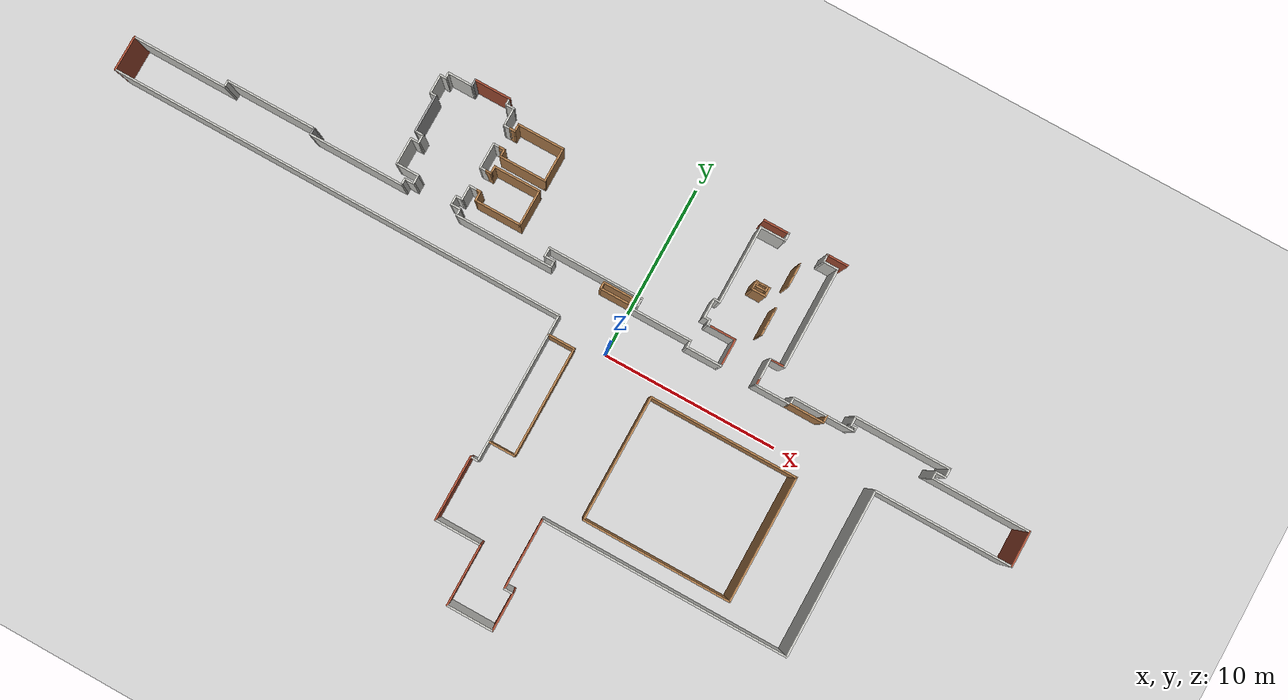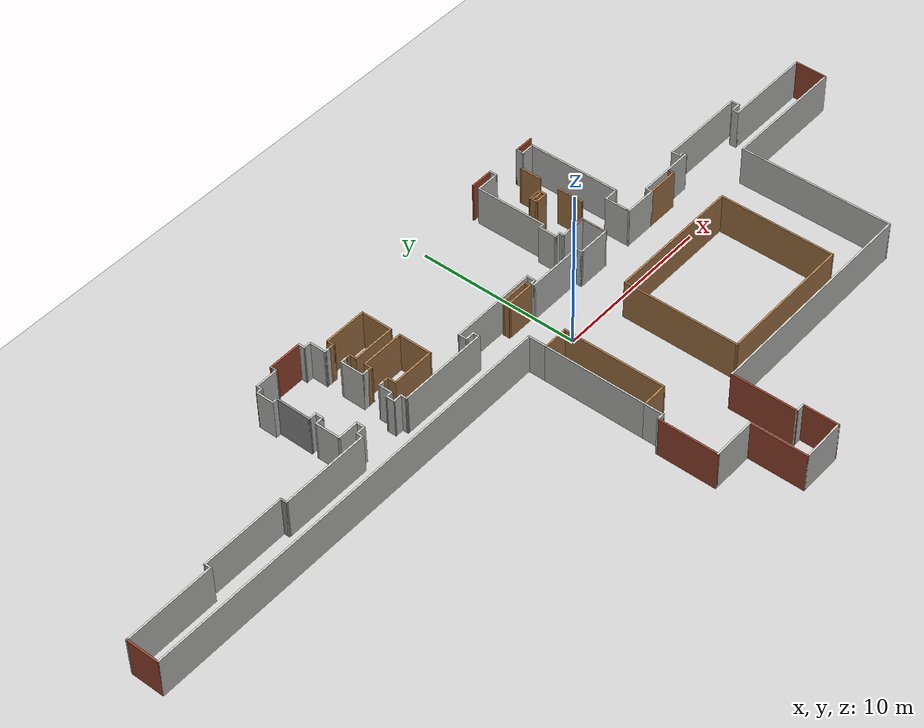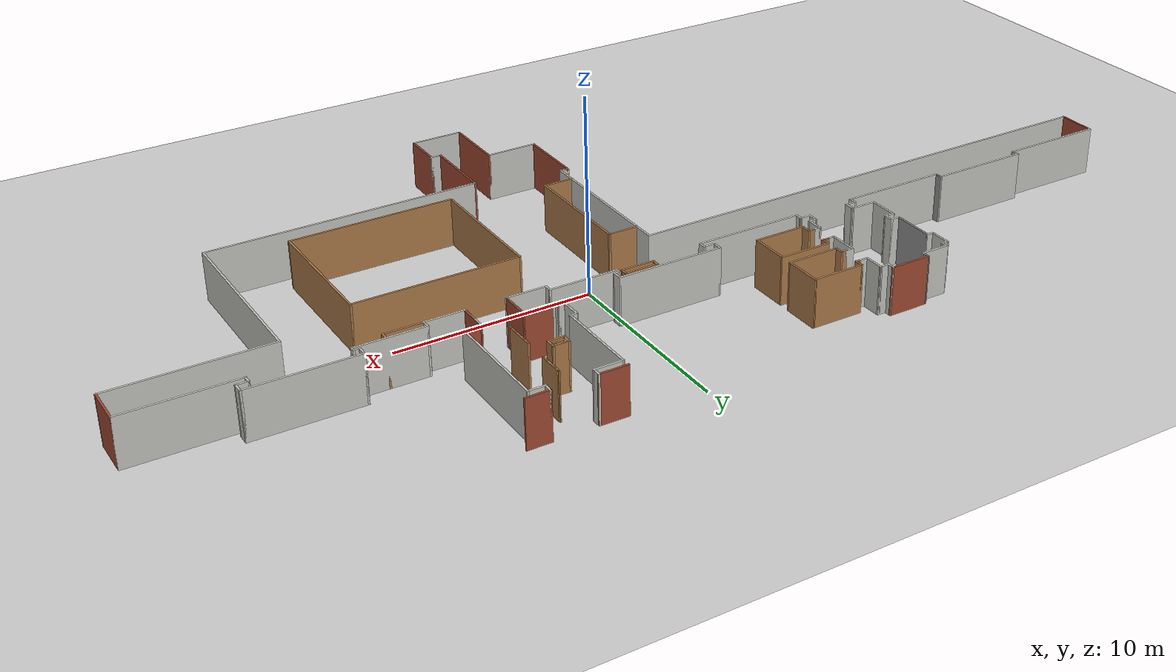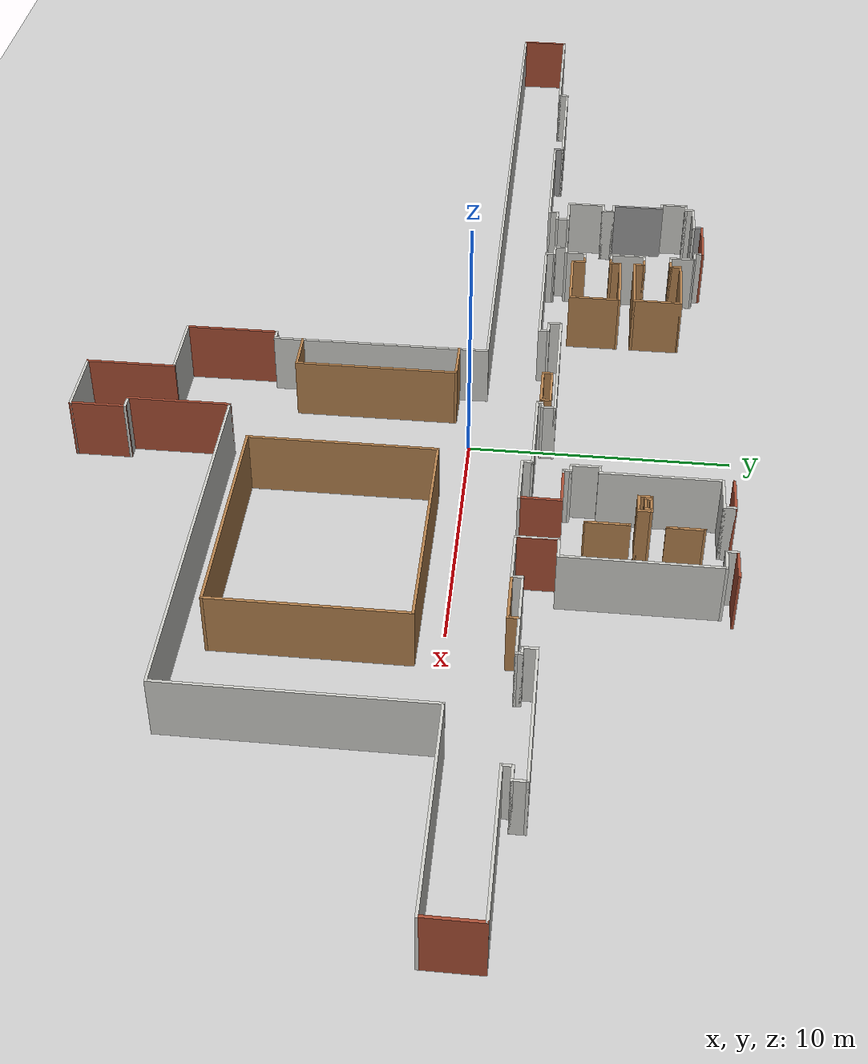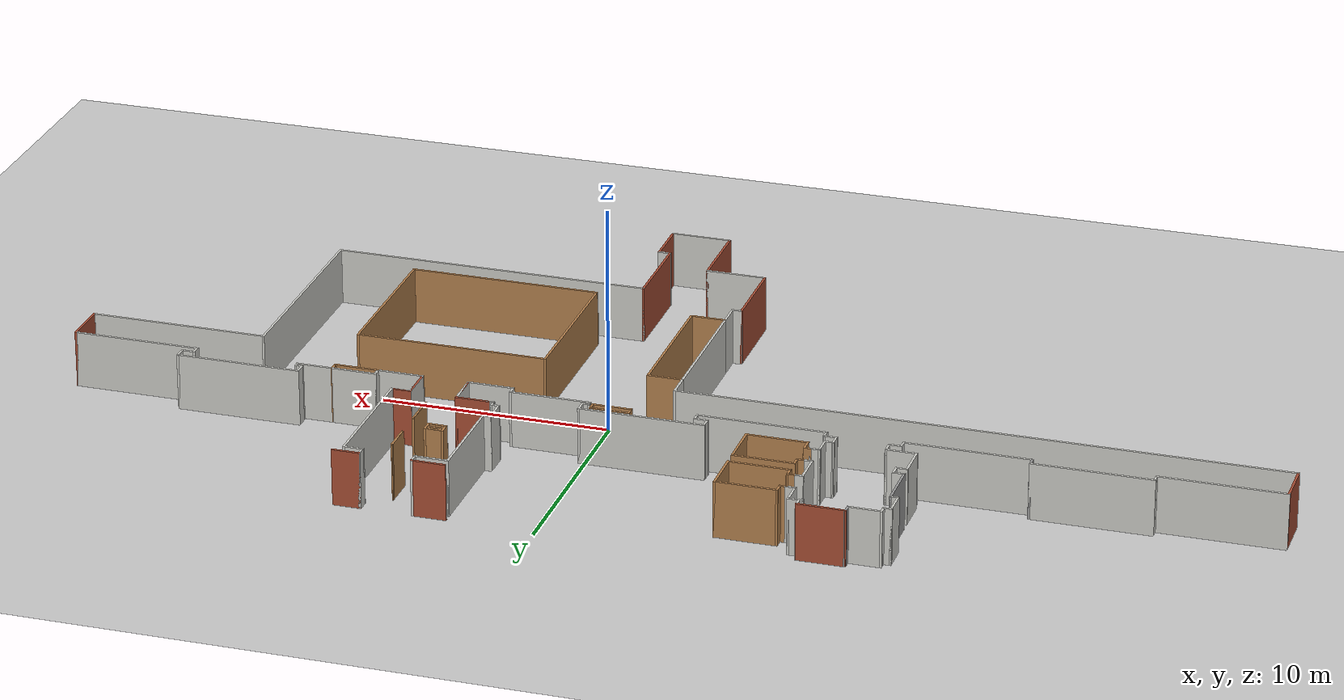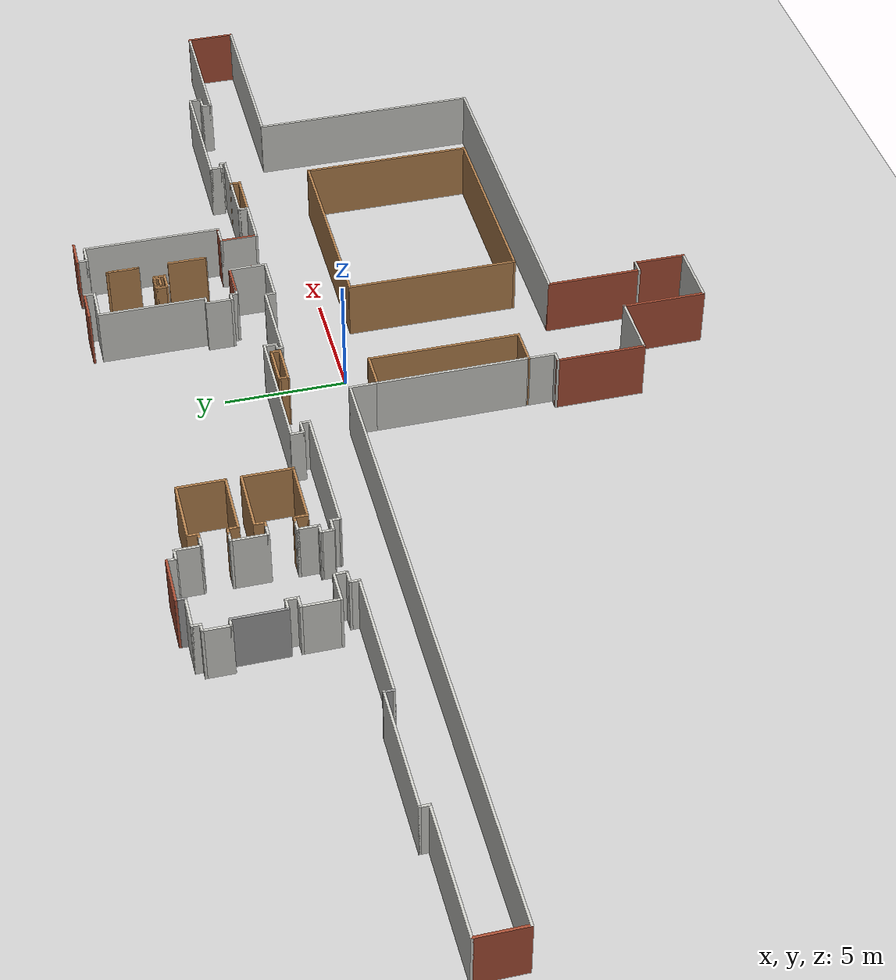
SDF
<sdf version="1.7">
 <world name="default">
  <light name="sun" type="directional">
   <pose>0 0 10 0 -0 0</pose>
   <diffuse>0.8 0.8 0.8 1</diffuse>
   <specular>0.2 0.2 0.2 1</specular>
   <attenuation>
    <range>1000</range>
    <constant>0.9</constant>
    <linear>0.01</linear>
    <quadratic>0.001</quadratic>
   </attenuation>
   <direction>-0.5 0.1 -0.9</direction>
   <spot><inner_angle>0</inner_angle><outer_angle>0</outer_angle><falloff>0</falloff></spot>
  </light>
  <model name="ground_plane">
   <static>1</static>
   <link name="link">
    <collision name="collision">
     <geometry><plane><normal>0 0 1</normal><size>100 100</size></plane></geometry>
     <surface><friction><ode><mu>100</mu><mu2>50</mu2></ode></friction></surface>
    </collision>
    <visual name="visual">
     <cast_shadows>0</cast_shadows>
     <geometry><plane><normal>0 0 1</normal><size>100 100</size></plane></geometry>
     <material>
      <script><uri>file://media/materials/scripts/gazebo.material</uri><name>Gazebo/Grey</name></script>
     </material>
    </visual>
   </link>
  </model>
  <gravity>0 0 -9.8</gravity>
  <magnetic_field>6e-06 2.3e-05 -4.2e-05</magnetic_field>
  <atmosphere type="adiabatic"/>
  <physics type="ode">
   <max_step_size>0.01</max_step_size>
   <real_time_factor>1</real_time_factor>
   <real_time_update_rate>100</real_time_update_rate>
  </physics>
  <scene><ambient>0.4 0.4 0.4 1</ambient><background>0.7 0.7 0.7 1</background><shadows>1</shadows></scene>
  <audio><device>default</device></audio>
  <spherical_coordinates>
   <surface_model>EARTH_WGS84</surface_model>
   <latitude_deg>0</latitude_deg>
   <longitude_deg>0</longitude_deg>
   <elevation>0</elevation>
   <heading_deg>0</heading_deg>
  </spherical_coordinates>
  <model name="miraikan_5F_gate_and_elevator">
   <link name="Wall_110">
    <pose>-7.54992 11.385 0 0 -0 1.57125</pose>
    <visual name="Wall_110_Visual">
     <pose>0 0 1.25 0 -0 0</pose>
     <geometry><box><size>0.45 0.1 2.5</size></box></geometry>
     <material>
      <script><uri>file://media/materials/scripts/gazebo.material</uri><name>Gazebo/CeilingTiled</name></script>
      <ambient>1 1 1 1</ambient>
      <shader type="pixel"/>
     </material>
     <meta><layer>0</layer></meta>
    </visual>
    <collision name="Wall_110_Collision">
     <pose>0 0 1.25 0 -0 0</pose>
     <geometry><box><size>0.45 0.1 2.5</size></box></geometry>
     <surface>
      <friction>
       <ode><mu>1</mu><mu2>1</mu2><fdir1>0 0 0</fdir1><slip1>0</slip1><slip2>0</slip2></ode>
       <torsional>
        <coefficient>1</coefficient>
        <patch_radius>0</patch_radius>
        <surface_radius>0</surface_radius>
        <use_patch_radius>1</use_patch_radius>
        <ode><slip>0</slip></ode>
       </torsional>
      </friction>
      <bounce><restitution_coefficient>0</restitution_coefficient><threshold>1e+06</threshold></bounce>
      <contact>
       <collide_without_contact>0</collide_without_contact>
       <collide_without_contact_bitmask>1</collide_without_contact_bitmask>
       <collide_bitmask>1</collide_bitmask>
       <ode>
        <soft_cfm>0</soft_cfm>
        <soft_erp>0.2</soft_erp>
        <kp>1e+13</kp>
        <kd>1</kd>
        <max_vel>0.01</max_vel>
        <min_depth>0</min_depth>
       </ode>
       <bullet>
        <split_impulse>1</split_impulse>
        <split_impulse_penetration_threshold>-0.01</split_impulse_penetration_threshold>
        <soft_cfm>0</soft_cfm>
        <soft_erp>0.2</soft_erp>
        <kp>1e+13</kp>
        <kd>1</kd>
       </bullet>
      </contact>
     </surface>
    </collision>
   </link>
   <link name="Wall_114">
    <pose>-7.32984 11.21 0 0 -0 0</pose>
    <visual name="Wall_114_Visual">
     <pose>0 0 1.25 0 -0 0</pose>
     <geometry><box><size>0.54 0.1 2.5</size></box></geometry>
     <material>
      <script><uri>file://media/materials/scripts/gazebo.material</uri><name>Gazebo/CeilingTiled</name></script>
      <ambient>1 1 1 1</ambient>
      <shader type="pixel"/>
     </material>
     <meta><layer>0</layer></meta>
    </visual>
    <collision name="Wall_114_Collision">
     <pose>0 0 1.25 0 -0 0</pose>
     <geometry><box><size>0.54 0.1 2.5</size></box></geometry>
     <surface>
      <friction>
       <ode><mu>1</mu><mu2>1</mu2><fdir1>0 0 0</fdir1><slip1>0</slip1><slip2>0</slip2></ode>
       <torsional>
        <coefficient>1</coefficient>
        <patch_radius>0</patch_radius>
        <surface_radius>0</surface_radius>
        <use_patch_radius>1</use_patch_radius>
        <ode><slip>0</slip></ode>
       </torsional>
      </friction>
      <bounce><restitution_coefficient>0</restitution_coefficient><threshold>1e+06</threshold></bounce>
      <contact>
       <collide_without_contact>0</collide_without_contact>
       <collide_without_contact_bitmask>1</collide_without_contact_bitmask>
       <collide_bitmask>1</collide_bitmask>
       <ode>
        <soft_cfm>0</soft_cfm>
        <soft_erp>0.2</soft_erp>
        <kp>1e+13</kp>
        <kd>1</kd>
        <max_vel>0.01</max_vel>
        <min_depth>0</min_depth>
       </ode>
       <bullet>
        <split_impulse>1</split_impulse>
        <split_impulse_penetration_threshold>-0.01</split_impulse_penetration_threshold>
        <soft_cfm>0</soft_cfm>
        <soft_erp>0.2</soft_erp>
        <kp>1e+13</kp>
        <kd>1</kd>
       </bullet>
      </contact>
     </surface>
    </collision>
   </link>
   <link name="Wall_116">
    <pose>-7.10992 10.71 0 0 0 -1.57095</pose>
    <visual name="Wall_116_Visual">
     <pose>0 0 1.25 0 -0 0</pose>
     <geometry><box><size>1.1 0.1 2.5</size></box></geometry>
     <material>
      <script><uri>file://media/materials/scripts/gazebo.material</uri><name>Gazebo/CeilingTiled</name></script>
      <ambient>1 1 1 1</ambient>
      <shader type="pixel"/>
     </material>
     <meta><layer>0</layer></meta>
    </visual>
    <collision name="Wall_116_Collision">
     <pose>0 0 1.25 0 -0 0</pose>
     <geometry><box><size>1.1 0.1 2.5</size></box></geometry>
     <surface>
      <friction>
       <ode><mu>1</mu><mu2>1</mu2><fdir1>0 0 0</fdir1><slip1>0</slip1><slip2>0</slip2></ode>
       <torsional>
        <coefficient>1</coefficient>
        <patch_radius>0</patch_radius>
        <surface_radius>0</surface_radius>
        <use_patch_radius>1</use_patch_radius>
        <ode><slip>0</slip></ode>
       </torsional>
      </friction>
      <bounce><restitution_coefficient>0</restitution_coefficient><threshold>1e+06</threshold></bounce>
      <contact>
       <collide_without_contact>0</collide_without_contact>
       <collide_without_contact_bitmask>1</collide_without_contact_bitmask>
       <collide_bitmask>1</collide_bitmask>
       <ode>
        <soft_cfm>0</soft_cfm>
        <soft_erp>0.2</soft_erp>
        <kp>1e+13</kp>
        <kd>1</kd>
        <max_vel>0.01</max_vel>
        <min_depth>0</min_depth>
       </ode>
       <bullet>
        <split_impulse>1</split_impulse>
        <split_impulse_penetration_threshold>-0.01</split_impulse_penetration_threshold>
        <soft_cfm>0</soft_cfm>
        <soft_erp>0.2</soft_erp>
        <kp>1e+13</kp>
        <kd>1</kd>
       </bullet>
      </contact>
     </surface>
    </collision>
   </link>
   <link name="Wall_118">
    <pose>-6.93 10.21 0 0 -0 0</pose>
    <visual name="Wall_118_Visual">
     <pose>0 0 1.25 0 -0 0</pose>
     <geometry><box><size>0.46 0.1 2.5</size></box></geometry>
     <material>
      <script><uri>file://media/materials/scripts/gazebo.material</uri><name>Gazebo/CeilingTiled</name></script>
      <ambient>1 1 1 1</ambient>
      <shader type="pixel"/>
     </material>
     <meta><layer>0</layer></meta>
    </visual>
    <collision name="Wall_118_Collision">
     <pose>0 0 1.25 0 -0 0</pose>
     <geometry><box><size>0.46 0.1 2.5</size></box></geometry>
     <surface>
      <friction>
       <ode><mu>1</mu><mu2>1</mu2><fdir1>0 0 0</fdir1><slip1>0</slip1><slip2>0</slip2></ode>
       <torsional>
        <coefficient>1</coefficient>
        <patch_radius>0</patch_radius>
        <surface_radius>0</surface_radius>
        <use_patch_radius>1</use_patch_radius>
        <ode><slip>0</slip></ode>
       </torsional>
      </friction>
      <bounce><restitution_coefficient>0</restitution_coefficient><threshold>1e+06</threshold></bounce>
      <contact>
       <collide_without_contact>0</collide_without_contact>
       <collide_without_contact_bitmask>1</collide_without_contact_bitmask>
       <collide_bitmask>1</collide_bitmask>
       <ode>
        <soft_cfm>0</soft_cfm>
        <soft_erp>0.2</soft_erp>
        <kp>1e+13</kp>
        <kd>1</kd>
        <max_vel>0.01</max_vel>
        <min_depth>0</min_depth>
       </ode>
       <bullet>
        <split_impulse>1</split_impulse>
        <split_impulse_penetration_threshold>-0.01</split_impulse_penetration_threshold>
        <soft_cfm>0</soft_cfm>
        <soft_erp>0.2</soft_erp>
        <kp>1e+13</kp>
        <kd>1</kd>
       </bullet>
      </contact>
     </surface>
    </collision>
   </link>
   <link name="Wall_122">
    <pose>-6.93 9.11 0 0 -0 3.14159</pose>
    <visual name="Wall_122_Visual">
     <pose>0 0 1.25 0 -0 0</pose>
     <geometry><box><size>0.46 0.1 2.5</size></box></geometry>
     <material>
      <script><uri>file://media/materials/scripts/gazebo.material</uri><name>Gazebo/CeilingTiled</name></script>
      <ambient>1 1 1 1</ambient>
      <shader type="pixel"/>
     </material>
     <meta><layer>0</layer></meta>
    </visual>
    <collision name="Wall_122_Collision">
     <pose>0 0 1.25 0 -0 0</pose>
     <geometry><box><size>0.46 0.1 2.5</size></box></geometry>
     <surface>
      <friction>
       <ode><mu>1</mu><mu2>1</mu2><fdir1>0 0 0</fdir1><slip1>0</slip1><slip2>0</slip2></ode>
       <torsional>
        <coefficient>1</coefficient>
        <patch_radius>0</patch_radius>
        <surface_radius>0</surface_radius>
        <use_patch_radius>1</use_patch_radius>
        <ode><slip>0</slip></ode>
       </torsional>
      </friction>
      <bounce><restitution_coefficient>0</restitution_coefficient><threshold>1e+06</threshold></bounce>
      <contact>
       <collide_without_contact>0</collide_without_contact>
       <collide_without_contact_bitmask>1</collide_without_contact_bitmask>
       <collide_bitmask>1</collide_bitmask>
       <ode>
        <soft_cfm>0</soft_cfm>
        <soft_erp>0.2</soft_erp>
        <kp>1e+13</kp>
        <kd>1</kd>
        <max_vel>0.01</max_vel>
        <min_depth>0</min_depth>
       </ode>
       <bullet>
        <split_impulse>1</split_impulse>
        <split_impulse_penetration_threshold>-0.01</split_impulse_penetration_threshold>
        <soft_cfm>0</soft_cfm>
        <soft_erp>0.2</soft_erp>
        <kp>1e+13</kp>
        <kd>1</kd>
       </bullet>
      </contact>
     </surface>
    </collision>
   </link>
   <link name="Wall_124">
    <pose>-7.11 8.41 0 0 0 -1.5708</pose>
    <visual name="Wall_124_Visual">
     <pose>0 0 1.25 0 -0 0</pose>
     <geometry><box><size>1.5 0.1 2.5</size></box></geometry>
     <material>
      <script><uri>file://media/materials/scripts/gazebo.material</uri><name>Gazebo/CeilingTiled</name></script>
      <ambient>1 1 1 1</ambient>
      <shader type="pixel"/>
     </material>
     <meta><layer>0</layer></meta>
    </visual>
    <collision name="Wall_124_Collision">
     <pose>0 0 1.25 0 -0 0</pose>
     <geometry><box><size>1.5 0.1 2.5</size></box></geometry>
     <surface>
      <friction>
       <ode><mu>1</mu><mu2>1</mu2><fdir1>0 0 0</fdir1><slip1>0</slip1><slip2>0</slip2></ode>
       <torsional>
        <coefficient>1</coefficient>
        <patch_radius>0</patch_radius>
        <surface_radius>0</surface_radius>
        <use_patch_radius>1</use_patch_radius>
        <ode><slip>0</slip></ode>
       </torsional>
      </friction>
      <bounce><restitution_coefficient>0</restitution_coefficient><threshold>1e+06</threshold></bounce>
      <contact>
       <collide_without_contact>0</collide_without_contact>
       <collide_without_contact_bitmask>1</collide_without_contact_bitmask>
       <collide_bitmask>1</collide_bitmask>
       <ode>
        <soft_cfm>0</soft_cfm>
        <soft_erp>0.2</soft_erp>
        <kp>1e+13</kp>
        <kd>1</kd>
        <max_vel>0.01</max_vel>
        <min_depth>0</min_depth>
       </ode>
       <bullet>
        <split_impulse>1</split_impulse>
        <split_impulse_penetration_threshold>-0.01</split_impulse_penetration_threshold>
        <soft_cfm>0</soft_cfm>
        <soft_erp>0.2</soft_erp>
        <kp>1e+13</kp>
        <kd>1</kd>
       </bullet>
      </contact>
     </surface>
    </collision>
   </link>
   <link name="Wall_126">
    <pose>-6.93 7.71 0 0 -0 0</pose>
    <visual name="Wall_126_Visual">
     <pose>0 0 1.25 0 -0 0</pose>
     <geometry><box><size>0.46 0.1 2.5</size></box></geometry>
     <material>
      <script><uri>file://media/materials/scripts/gazebo.material</uri><name>Gazebo/CeilingTiled</name></script>
      <ambient>1 1 1 1</ambient>
      <shader type="pixel"/>
     </material>
     <meta><layer>0</layer></meta>
    </visual>
    <collision name="Wall_126_Collision">
     <pose>0 0 1.25 0 -0 0</pose>
     <geometry><box><size>0.46 0.1 2.5</size></box></geometry>
     <surface>
      <friction>
       <ode><mu>1</mu><mu2>1</mu2><fdir1>0 0 0</fdir1><slip1>0</slip1><slip2>0</slip2></ode>
       <torsional>
        <coefficient>1</coefficient>
        <patch_radius>0</patch_radius>
        <surface_radius>0</surface_radius>
        <use_patch_radius>1</use_patch_radius>
        <ode><slip>0</slip></ode>
       </torsional>
      </friction>
      <bounce><restitution_coefficient>0</restitution_coefficient><threshold>1e+06</threshold></bounce>
      <contact>
       <collide_without_contact>0</collide_without_contact>
       <collide_without_contact_bitmask>1</collide_without_contact_bitmask>
       <collide_bitmask>1</collide_bitmask>
       <ode>
        <soft_cfm>0</soft_cfm>
        <soft_erp>0.2</soft_erp>
        <kp>1e+13</kp>
        <kd>1</kd>
        <max_vel>0.01</max_vel>
        <min_depth>0</min_depth>
       </ode>
       <bullet>
        <split_impulse>1</split_impulse>
        <split_impulse_penetration_threshold>-0.01</split_impulse_penetration_threshold>
        <soft_cfm>0</soft_cfm>
        <soft_erp>0.2</soft_erp>
        <kp>1e+13</kp>
        <kd>1</kd>
       </bullet>
      </contact>
     </surface>
    </collision>
   </link>
   <link name="Wall_130">
    <pose>-6.93 6.61 0 0 -0 3.14159</pose>
    <visual name="Wall_130_Visual">
     <pose>0 0 1.25 0 -0 0</pose>
     <geometry><box><size>0.46 0.1 2.5</size></box></geometry>
     <material>
      <script><uri>file://media/materials/scripts/gazebo.material</uri><name>Gazebo/CeilingTiled</name></script>
      <ambient>1 1 1 1</ambient>
      <shader type="pixel"/>
     </material>
     <meta><layer>0</layer></meta>
    </visual>
    <collision name="Wall_130_Collision">
     <pose>0 0 1.25 0 -0 0</pose>
     <geometry><box><size>0.46 0.1 2.5</size></box></geometry>
     <surface>
      <friction>
       <ode><mu>1</mu><mu2>1</mu2><fdir1>0 0 0</fdir1><slip1>0</slip1><slip2>0</slip2></ode>
       <torsional>
        <coefficient>1</coefficient>
        <patch_radius>0</patch_radius>
        <surface_radius>0</surface_radius>
        <use_patch_radius>1</use_patch_radius>
        <ode><slip>0</slip></ode>
       </torsional>
      </friction>
      <bounce><restitution_coefficient>0</restitution_coefficient><threshold>1e+06</threshold></bounce>
      <contact>
       <collide_without_contact>0</collide_without_contact>
       <collide_without_contact_bitmask>1</collide_without_contact_bitmask>
       <collide_bitmask>1</collide_bitmask>
       <ode>
        <soft_cfm>0</soft_cfm>
        <soft_erp>0.2</soft_erp>
        <kp>1e+13</kp>
        <kd>1</kd>
        <max_vel>0.01</max_vel>
        <min_depth>0</min_depth>
       </ode>
       <bullet>
        <split_impulse>1</split_impulse>
        <split_impulse_penetration_threshold>-0.01</split_impulse_penetration_threshold>
        <soft_cfm>0</soft_cfm>
        <soft_erp>0.2</soft_erp>
        <kp>1e+13</kp>
        <kd>1</kd>
       </bullet>
      </contact>
     </surface>
    </collision>
   </link>
   <link name="Wall_132">
    <pose>-7.11 6.21 0 0 0 -1.5708</pose>
    <visual name="Wall_132_Visual">
     <pose>0 0 1.25 0 -0 0</pose>
     <geometry><box><size>0.9 0.1 2.5</size></box></geometry>
     <material>
      <script><uri>file://media/materials/scripts/gazebo.material</uri><name>Gazebo/CeilingTiled</name></script>
      <ambient>1 1 1 1</ambient>
      <shader type="pixel"/>
     </material>
     <meta><layer>0</layer></meta>
    </visual>
    <collision name="Wall_132_Collision">
     <pose>0 0 1.25 0 -0 0</pose>
     <geometry><box><size>0.9 0.1 2.5</size></box></geometry>
     <surface>
      <friction>
       <ode><mu>1</mu><mu2>1</mu2><fdir1>0 0 0</fdir1><slip1>0</slip1><slip2>0</slip2></ode>
       <torsional>
        <coefficient>1</coefficient>
        <patch_radius>0</patch_radius>
        <surface_radius>0</surface_radius>
        <use_patch_radius>1</use_patch_radius>
        <ode><slip>0</slip></ode>
       </torsional>
      </friction>
      <bounce><restitution_coefficient>0</restitution_coefficient><threshold>1e+06</threshold></bounce>
      <contact>
       <collide_without_contact>0</collide_without_contact>
       <collide_without_contact_bitmask>1</collide_without_contact_bitmask>
       <collide_bitmask>1</collide_bitmask>
       <ode>
        <soft_cfm>0</soft_cfm>
        <soft_erp>0.2</soft_erp>
        <kp>1e+13</kp>
        <kd>1</kd>
        <max_vel>0.01</max_vel>
        <min_depth>0</min_depth>
       </ode>
       <bullet>
        <split_impulse>1</split_impulse>
        <split_impulse_penetration_threshold>-0.01</split_impulse_penetration_threshold>
        <soft_cfm>0</soft_cfm>
        <soft_erp>0.2</soft_erp>
        <kp>1e+13</kp>
        <kd>1</kd>
       </bullet>
      </contact>
     </surface>
    </collision>
   </link>
   <link name="Wall_134">
    <pose>-7.285 5.81 0 0 -0 3.14159</pose>
    <visual name="Wall_134_Visual">
     <pose>0 0 1.25 0 -0 0</pose>
     <geometry><box><size>0.45 0.1 2.5</size></box></geometry>
     <material>
      <script><uri>file://media/materials/scripts/gazebo.material</uri><name>Gazebo/CeilingTiled</name></script>
      <ambient>1 1 1 1</ambient>
      <shader type="pixel"/>
     </material>
     <meta><layer>0</layer></meta>
    </visual>
    <collision name="Wall_134_Collision">
     <pose>0 0 1.25 0 -0 0</pose>
     <geometry><box><size>0.45 0.1 2.5</size></box></geometry>
     <surface>
      <friction>
       <ode><mu>1</mu><mu2>1</mu2><fdir1>0 0 0</fdir1><slip1>0</slip1><slip2>0</slip2></ode>
       <torsional>
        <coefficient>1</coefficient>
        <patch_radius>0</patch_radius>
        <surface_radius>0</surface_radius>
        <use_patch_radius>1</use_patch_radius>
        <ode><slip>0</slip></ode>
       </torsional>
      </friction>
      <bounce><restitution_coefficient>0</restitution_coefficient><threshold>1e+06</threshold></bounce>
      <contact>
       <collide_without_contact>0</collide_without_contact>
       <collide_without_contact_bitmask>1</collide_without_contact_bitmask>
       <collide_bitmask>1</collide_bitmask>
       <ode>
        <soft_cfm>0</soft_cfm>
        <soft_erp>0.2</soft_erp>
        <kp>1e+13</kp>
        <kd>1</kd>
        <max_vel>0.01</max_vel>
        <min_depth>0</min_depth>
       </ode>
       <bullet>
        <split_impulse>1</split_impulse>
        <split_impulse_penetration_threshold>-0.01</split_impulse_penetration_threshold>
        <soft_cfm>0</soft_cfm>
        <soft_erp>0.2</soft_erp>
        <kp>1e+13</kp>
        <kd>1</kd>
       </bullet>
      </contact>
     </surface>
    </collision>
   </link>
   <link name="Wall_136">
    <pose>-7.45991 5.57 0 0 0 -1.57043</pose>
    <visual name="Wall_136_Visual">
     <pose>0 0 1.25 0 -0 0</pose>
     <geometry><box><size>0.58 0.1 2.5</size></box></geometry>
     <material>
      <script><uri>file://media/materials/scripts/gazebo.material</uri><name>Gazebo/CeilingTiled</name></script>
      <ambient>1 1 1 1</ambient>
      <shader type="pixel"/>
     </material>
     <meta><layer>0</layer></meta>
    </visual>
    <collision name="Wall_136_Collision">
     <pose>0 0 1.25 0 -0 0</pose>
     <geometry><box><size>0.58 0.1 2.5</size></box></geometry>
     <surface>
      <friction>
       <ode><mu>1</mu><mu2>1</mu2><fdir1>0 0 0</fdir1><slip1>0</slip1><slip2>0</slip2></ode>
       <torsional>
        <coefficient>1</coefficient>
        <patch_radius>0</patch_radius>
        <surface_radius>0</surface_radius>
        <use_patch_radius>1</use_patch_radius>
        <ode><slip>0</slip></ode>
       </torsional>
      </friction>
      <bounce><restitution_coefficient>0</restitution_coefficient><threshold>1e+06</threshold></bounce>
      <contact>
       <collide_without_contact>0</collide_without_contact>
       <collide_without_contact_bitmask>1</collide_without_contact_bitmask>
       <collide_bitmask>1</collide_bitmask>
       <ode>
        <soft_cfm>0</soft_cfm>
        <soft_erp>0.2</soft_erp>
        <kp>1e+13</kp>
        <kd>1</kd>
        <max_vel>0.01</max_vel>
        <min_depth>0</min_depth>
       </ode>
       <bullet>
        <split_impulse>1</split_impulse>
        <split_impulse_penetration_threshold>-0.01</split_impulse_penetration_threshold>
        <soft_cfm>0</soft_cfm>
        <soft_erp>0.2</soft_erp>
        <kp>1e+13</kp>
        <kd>1</kd>
       </bullet>
      </contact>
     </surface>
    </collision>
   </link>
   <link name="Wall_143">
    <pose>-7.20482 5.33 0 0 -0 0</pose>
    <visual name="Wall_143_Visual">
     <pose>0 0 1.25 0 -0 0</pose>
     <geometry><box><size>0.61 0.1 2.5</size></box></geometry>
     <material>
      <script><uri>file://media/materials/scripts/gazebo.material</uri><name>Gazebo/CeilingTiled</name></script>
      <ambient>1 1 1 1</ambient>
      <shader type="pixel"/>
     </material>
     <meta><layer>0</layer></meta>
    </visual>
    <collision name="Wall_143_Collision">
     <pose>0 0 1.25 0 -0 0</pose>
     <geometry><box><size>0.61 0.1 2.5</size></box></geometry>
     <surface>
      <friction>
       <ode><mu>1</mu><mu2>1</mu2><fdir1>0 0 0</fdir1><slip1>0</slip1><slip2>0</slip2></ode>
       <torsional>
        <coefficient>1</coefficient>
        <patch_radius>0</patch_radius>
        <surface_radius>0</surface_radius>
        <use_patch_radius>1</use_patch_radius>
        <ode><slip>0</slip></ode>
       </torsional>
      </friction>
      <bounce><restitution_coefficient>0</restitution_coefficient><threshold>1e+06</threshold></bounce>
      <contact>
       <collide_without_contact>0</collide_without_contact>
       <collide_without_contact_bitmask>1</collide_without_contact_bitmask>
       <collide_bitmask>1</collide_bitmask>
       <ode>
        <soft_cfm>0</soft_cfm>
        <soft_erp>0.2</soft_erp>
        <kp>1e+13</kp>
        <kd>1</kd>
        <max_vel>0.01</max_vel>
        <min_depth>0</min_depth>
       </ode>
       <bullet>
        <split_impulse>1</split_impulse>
        <split_impulse_penetration_threshold>-0.01</split_impulse_penetration_threshold>
        <soft_cfm>0</soft_cfm>
        <soft_erp>0.2</soft_erp>
        <kp>1e+13</kp>
        <kd>1</kd>
       </bullet>
      </contact>
     </surface>
    </collision>
   </link>
   <link name="Wall_147">
    <pose>-6.94991 5.155 0 0 0 -1.5713</pose>
    <visual name="Wall_147_Visual">
     <pose>0 0 1.25 0 -0 0</pose>
     <geometry><box><size>0.45 0.1 2.5</size></box></geometry>
     <material>
      <script><uri>file://media/materials/scripts/gazebo.material</uri><name>Gazebo/CeilingTiled</name></script>
      <ambient>1 1 1 1</ambient>
      <shader type="pixel"/>
     </material>
     <meta><layer>0</layer></meta>
    </visual>
    <collision name="Wall_147_Collision">
     <pose>0 0 1.25 0 -0 0</pose>
     <geometry><box><size>0.45 0.1 2.5</size></box></geometry>
     <surface>
      <friction>
       <ode><mu>1</mu><mu2>1</mu2><fdir1>0 0 0</fdir1><slip1>0</slip1><slip2>0</slip2></ode>
       <torsional>
        <coefficient>1</coefficient>
        <patch_radius>0</patch_radius>
        <surface_radius>0</surface_radius>
        <use_patch_radius>1</use_patch_radius>
        <ode><slip>0</slip></ode>
       </torsional>
      </friction>
      <bounce><restitution_coefficient>0</restitution_coefficient><threshold>1e+06</threshold></bounce>
      <contact>
       <collide_without_contact>0</collide_without_contact>
       <collide_without_contact_bitmask>1</collide_without_contact_bitmask>
       <collide_bitmask>1</collide_bitmask>
       <ode>
        <soft_cfm>0</soft_cfm>
        <soft_erp>0.2</soft_erp>
        <kp>1e+13</kp>
        <kd>1</kd>
        <max_vel>0.01</max_vel>
        <min_depth>0</min_depth>
       </ode>
       <bullet>
        <split_impulse>1</split_impulse>
        <split_impulse_penetration_threshold>-0.01</split_impulse_penetration_threshold>
        <soft_cfm>0</soft_cfm>
        <soft_erp>0.2</soft_erp>
        <kp>1e+13</kp>
        <kd>1</kd>
       </bullet>
      </contact>
     </surface>
    </collision>
   </link>
   <link name="Wall_149">
    <pose>-4.2 4.98 0 0 -0 0</pose>
    <visual name="Wall_149_Visual">
     <pose>0 0 1.25 0 -0 0</pose>
     <geometry><box><size>5.6 0.1 2.5</size></box></geometry>
     <material>
      <script><uri>file://media/materials/scripts/gazebo.material</uri><name>Gazebo/CeilingTiled</name></script>
      <ambient>1 1 1 1</ambient>
      <shader type="pixel"/>
     </material>
     <meta><layer>0</layer></meta>
    </visual>
    <collision name="Wall_149_Collision">
     <pose>0 0 1.25 0 -0 0</pose>
     <geometry><box><size>5.6 0.1 2.5</size></box></geometry>
     <surface>
      <friction>
       <ode><mu>1</mu><mu2>1</mu2><fdir1>0 0 0</fdir1><slip1>0</slip1><slip2>0</slip2></ode>
       <torsional>
        <coefficient>1</coefficient>
        <patch_radius>0</patch_radius>
        <surface_radius>0</surface_radius>
        <use_patch_radius>1</use_patch_radius>
        <ode><slip>0</slip></ode>
       </torsional>
      </friction>
      <bounce><restitution_coefficient>0</restitution_coefficient><threshold>1e+06</threshold></bounce>
      <contact>
       <collide_without_contact>0</collide_without_contact>
       <collide_without_contact_bitmask>1</collide_without_contact_bitmask>
       <collide_bitmask>1</collide_bitmask>
       <ode>
        <soft_cfm>0</soft_cfm>
        <soft_erp>0.2</soft_erp>
        <kp>1e+13</kp>
        <kd>1</kd>
        <max_vel>0.01</max_vel>
        <min_depth>0</min_depth>
       </ode>
       <bullet>
        <split_impulse>1</split_impulse>
        <split_impulse_penetration_threshold>-0.01</split_impulse_penetration_threshold>
        <soft_cfm>0</soft_cfm>
        <soft_erp>0.2</soft_erp>
        <kp>1e+13</kp>
        <kd>1</kd>
       </bullet>
      </contact>
     </surface>
    </collision>
   </link>
   <link name="Wall_167">
    <pose>-1.45 5.155 0 0 -0 1.5708</pose>
    <visual name="Wall_167_Visual">
     <pose>0 0 1.25 0 -0 0</pose>
     <geometry><box><size>0.45 0.1 2.5</size></box></geometry>
     <material>
      <script><uri>file://media/materials/scripts/gazebo.material</uri><name>Gazebo/CeilingTiled</name></script>
      <ambient>1 1 1 1</ambient>
      <shader type="pixel"/>
     </material>
     <meta><layer>0</layer></meta>
    </visual>
    <collision name="Wall_167_Collision">
     <pose>0 0 1.25 0 -0 0</pose>
     <geometry><box><size>0.45 0.1 2.5</size></box></geometry>
     <surface>
      <friction>
       <ode><mu>1</mu><mu2>1</mu2><fdir1>0 0 0</fdir1><slip1>0</slip1><slip2>0</slip2></ode>
       <torsional>
        <coefficient>1</coefficient>
        <patch_radius>0</patch_radius>
        <surface_radius>0</surface_radius>
        <use_patch_radius>1</use_patch_radius>
        <ode><slip>0</slip></ode>
       </torsional>
      </friction>
      <bounce><restitution_coefficient>0</restitution_coefficient><threshold>1e+06</threshold></bounce>
      <contact>
       <collide_without_contact>0</collide_without_contact>
       <collide_without_contact_bitmask>1</collide_without_contact_bitmask>
       <collide_bitmask>1</collide_bitmask>
       <ode>
        <soft_cfm>0</soft_cfm>
        <soft_erp>0.2</soft_erp>
        <kp>1e+13</kp>
        <kd>1</kd>
        <max_vel>0.01</max_vel>
        <min_depth>0</min_depth>
       </ode>
       <bullet>
        <split_impulse>1</split_impulse>
        <split_impulse_penetration_threshold>-0.01</split_impulse_penetration_threshold>
        <soft_cfm>0</soft_cfm>
        <soft_erp>0.2</soft_erp>
        <kp>1e+13</kp>
        <kd>1</kd>
       </bullet>
      </contact>
     </surface>
    </collision>
   </link>
   <link name="Wall_169">
    <pose>-1.72 5.33 0 0 -0 3.14159</pose>
    <visual name="Wall_169_Visual">
     <pose>0 0 1.25 0 -0 0</pose>
     <geometry><box><size>0.64 0.1 2.5</size></box></geometry>
     <material>
      <script><uri>file://media/materials/scripts/gazebo.material</uri><name>Gazebo/CeilingTiled</name></script>
      <ambient>1 1 1 1</ambient>
      <shader type="pixel"/>
     </material>
     <meta><layer>0</layer></meta>
    </visual>
    <collision name="Wall_169_Collision">
     <pose>0 0 1.25 0 -0 0</pose>
     <geometry><box><size>0.64 0.1 2.5</size></box></geometry>
     <surface>
      <friction>
       <ode><mu>1</mu><mu2>1</mu2><fdir1>0 0 0</fdir1><slip1>0</slip1><slip2>0</slip2></ode>
       <torsional>
        <coefficient>1</coefficient>
        <patch_radius>0</patch_radius>
        <surface_radius>0</surface_radius>
        <use_patch_radius>1</use_patch_radius>
        <ode><slip>0</slip></ode>
       </torsional>
      </friction>
      <bounce><restitution_coefficient>0</restitution_coefficient><threshold>1e+06</threshold></bounce>
      <contact>
       <collide_without_contact>0</collide_without_contact>
       <collide_without_contact_bitmask>1</collide_without_contact_bitmask>
       <collide_bitmask>1</collide_bitmask>
       <ode>
        <soft_cfm>0</soft_cfm>
        <soft_erp>0.2</soft_erp>
        <kp>1e+13</kp>
        <kd>1</kd>
        <max_vel>0.01</max_vel>
        <min_depth>0</min_depth>
       </ode>
       <bullet>
        <split_impulse>1</split_impulse>
        <split_impulse_penetration_threshold>-0.01</split_impulse_penetration_threshold>
        <soft_cfm>0</soft_cfm>
        <soft_erp>0.2</soft_erp>
        <kp>1e+13</kp>
        <kd>1</kd>
       </bullet>
      </contact>
     </surface>
    </collision>
   </link>
   <link name="Wall_171">
    <pose>-1.99 5.57 0 0 -0 1.5708</pose>
    <visual name="Wall_171_Visual">
     <pose>0 0 1.25 0 -0 0</pose>
     <geometry><box><size>0.58 0.1 2.5</size></box></geometry>
     <material>
      <script><uri>file://media/materials/scripts/gazebo.material</uri><name>Gazebo/CeilingTiled</name></script>
      <ambient>1 1 1 1</ambient>
      <shader type="pixel"/>
     </material>
     <meta><layer>0</layer></meta>
    </visual>
    <collision name="Wall_171_Collision">
     <pose>0 0 1.25 0 -0 0</pose>
     <geometry><box><size>0.58 0.1 2.5</size></box></geometry>
     <surface>
      <friction>
       <ode><mu>1</mu><mu2>1</mu2><fdir1>0 0 0</fdir1><slip1>0</slip1><slip2>0</slip2></ode>
       <torsional>
        <coefficient>1</coefficient>
        <patch_radius>0</patch_radius>
        <surface_radius>0</surface_radius>
        <use_patch_radius>1</use_patch_radius>
        <ode><slip>0</slip></ode>
       </torsional>
      </friction>
      <bounce><restitution_coefficient>0</restitution_coefficient><threshold>1e+06</threshold></bounce>
      <contact>
       <collide_without_contact>0</collide_without_contact>
       <collide_without_contact_bitmask>1</collide_without_contact_bitmask>
       <collide_bitmask>1</collide_bitmask>
       <ode>
        <soft_cfm>0</soft_cfm>
        <soft_erp>0.2</soft_erp>
        <kp>1e+13</kp>
        <kd>1</kd>
        <max_vel>0.01</max_vel>
        <min_depth>0</min_depth>
       </ode>
       <bullet>
        <split_impulse>1</split_impulse>
        <split_impulse_penetration_threshold>-0.01</split_impulse_penetration_threshold>
        <soft_cfm>0</soft_cfm>
        <soft_erp>0.2</soft_erp>
        <kp>1e+13</kp>
        <kd>1</kd>
       </bullet>
      </contact>
     </surface>
    </collision>
   </link>
   <link name="Wall_174">
    <pose>0.695 5.81 0 0 -0 0</pose>
    <visual name="Wall_174_Visual">
     <pose>0 0 1.25 0 -0 0</pose>
     <geometry><box><size>5.47 0.1 2.5</size></box></geometry>
     <material>
      <script><uri>file://media/materials/scripts/gazebo.material</uri><name>Gazebo/CeilingTiled</name></script>
      <ambient>1 1 1 1</ambient>
      <shader type="pixel"/>
     </material>
     <meta><layer>0</layer></meta>
    </visual>
    <collision name="Wall_174_Collision">
     <pose>0 0 1.25 0 -0 0</pose>
     <geometry><box><size>5.47 0.1 2.5</size></box></geometry>
     <surface>
      <friction>
       <ode><mu>1</mu><mu2>1</mu2><fdir1>0 0 0</fdir1><slip1>0</slip1><slip2>0</slip2></ode>
       <torsional>
        <coefficient>1</coefficient>
        <patch_radius>0</patch_radius>
        <surface_radius>0</surface_radius>
        <use_patch_radius>1</use_patch_radius>
        <ode><slip>0</slip></ode>
       </torsional>
      </friction>
      <bounce><restitution_coefficient>0</restitution_coefficient><threshold>1e+06</threshold></bounce>
      <contact>
       <collide_without_contact>0</collide_without_contact>
       <collide_without_contact_bitmask>1</collide_without_contact_bitmask>
       <collide_bitmask>1</collide_bitmask>
       <ode>
        <soft_cfm>0</soft_cfm>
        <soft_erp>0.2</soft_erp>
        <kp>1e+13</kp>
        <kd>1</kd>
        <max_vel>0.01</max_vel>
        <min_depth>0</min_depth>
       </ode>
       <bullet>
        <split_impulse>1</split_impulse>
        <split_impulse_penetration_threshold>-0.01</split_impulse_penetration_threshold>
        <soft_cfm>0</soft_cfm>
        <soft_erp>0.2</soft_erp>
        <kp>1e+13</kp>
        <kd>1</kd>
       </bullet>
      </contact>
     </surface>
    </collision>
   </link>
   <link name="Wall_176">
    <pose>3.38 5.57 0 0 0 -1.5708</pose>
    <visual name="Wall_176_Visual">
     <pose>0 0 1.25 0 -0 0</pose>
     <geometry><box><size>0.58 0.1 2.5</size></box></geometry>
     <material>
      <script><uri>file://media/materials/scripts/gazebo.material</uri><name>Gazebo/CeilingTiled</name></script>
      <ambient>1 1 1 1</ambient>
      <shader type="pixel"/>
     </material>
     <meta><layer>0</layer></meta>
    </visual>
    <collision name="Wall_176_Collision">
     <pose>0 0 1.25 0 -0 0</pose>
     <geometry><box><size>0.58 0.1 2.5</size></box></geometry>
     <surface>
      <friction>
       <ode><mu>1</mu><mu2>1</mu2><fdir1>0 0 0</fdir1><slip1>0</slip1><slip2>0</slip2></ode>
       <torsional>
        <coefficient>1</coefficient>
        <patch_radius>0</patch_radius>
        <surface_radius>0</surface_radius>
        <use_patch_radius>1</use_patch_radius>
        <ode><slip>0</slip></ode>
       </torsional>
      </friction>
      <bounce><restitution_coefficient>0</restitution_coefficient><threshold>1e+06</threshold></bounce>
      <contact>
       <collide_without_contact>0</collide_without_contact>
       <collide_without_contact_bitmask>1</collide_without_contact_bitmask>
       <collide_bitmask>1</collide_bitmask>
       <ode>
        <soft_cfm>0</soft_cfm>
        <soft_erp>0.2</soft_erp>
        <kp>1e+13</kp>
        <kd>1</kd>
        <max_vel>0.01</max_vel>
        <min_depth>0</min_depth>
       </ode>
       <bullet>
        <split_impulse>1</split_impulse>
        <split_impulse_penetration_threshold>-0.01</split_impulse_penetration_threshold>
        <soft_cfm>0</soft_cfm>
        <soft_erp>0.2</soft_erp>
        <kp>1e+13</kp>
        <kd>1</kd>
       </bullet>
      </contact>
     </surface>
    </collision>
   </link>
   <link name="Wall_178">
    <pose>3.245 5.33 0 0 -0 3.14159</pose>
    <visual name="Wall_178_Visual">
     <pose>0 0 1.25 0 -0 0</pose>
     <geometry><box><size>0.37 0.1 2.5</size></box></geometry>
     <material>
      <script><uri>file://media/materials/scripts/gazebo.material</uri><name>Gazebo/CeilingTiled</name></script>
      <ambient>1 1 1 1</ambient>
      <shader type="pixel"/>
     </material>
     <meta><layer>0</layer></meta>
    </visual>
    <collision name="Wall_178_Collision">
     <pose>0 0 1.25 0 -0 0</pose>
     <geometry><box><size>0.37 0.1 2.5</size></box></geometry>
     <surface>
      <friction>
       <ode><mu>1</mu><mu2>1</mu2><fdir1>0 0 0</fdir1><slip1>0</slip1><slip2>0</slip2></ode>
       <torsional>
        <coefficient>1</coefficient>
        <patch_radius>0</patch_radius>
        <surface_radius>0</surface_radius>
        <use_patch_radius>1</use_patch_radius>
        <ode><slip>0</slip></ode>
       </torsional>
      </friction>
      <bounce><restitution_coefficient>0</restitution_coefficient><threshold>1e+06</threshold></bounce>
      <contact>
       <collide_without_contact>0</collide_without_contact>
       <collide_without_contact_bitmask>1</collide_without_contact_bitmask>
       <collide_bitmask>1</collide_bitmask>
       <ode>
        <soft_cfm>0</soft_cfm>
        <soft_erp>0.2</soft_erp>
        <kp>1e+13</kp>
        <kd>1</kd>
        <max_vel>0.01</max_vel>
        <min_depth>0</min_depth>
       </ode>
       <bullet>
        <split_impulse>1</split_impulse>
        <split_impulse_penetration_threshold>-0.01</split_impulse_penetration_threshold>
        <soft_cfm>0</soft_cfm>
        <soft_erp>0.2</soft_erp>
        <kp>1e+13</kp>
        <kd>1</kd>
       </bullet>
      </contact>
     </surface>
    </collision>
   </link>
   <link name="Wall_181">
    <pose>3.11 5.235 0 0 0 -1.5708</pose>
    <visual name="Wall_181_Visual">
     <pose>0 0 1.25 0 -0 0</pose>
     <geometry><box><size>0.29 0.1 2.5</size></box></geometry>
     <material>
      <script><uri>file://media/materials/scripts/gazebo.material</uri><name>Gazebo/CeilingTiled</name></script>
      <ambient>1 1 1 1</ambient>
      <shader type="pixel"/>
     </material>
     <meta><layer>0</layer></meta>
    </visual>
    <collision name="Wall_181_Collision">
     <pose>0 0 1.25 0 -0 0</pose>
     <geometry><box><size>0.29 0.1 2.5</size></box></geometry>
     <surface>
      <friction>
       <ode><mu>1</mu><mu2>1</mu2><fdir1>0 0 0</fdir1><slip1>0</slip1><slip2>0</slip2></ode>
       <torsional>
        <coefficient>1</coefficient>
        <patch_radius>0</patch_radius>
        <surface_radius>0</surface_radius>
        <use_patch_radius>1</use_patch_radius>
        <ode><slip>0</slip></ode>
       </torsional>
      </friction>
      <bounce><restitution_coefficient>0</restitution_coefficient><threshold>1e+06</threshold></bounce>
      <contact>
       <collide_without_contact>0</collide_without_contact>
       <collide_without_contact_bitmask>1</collide_without_contact_bitmask>
       <collide_bitmask>1</collide_bitmask>
       <ode>
        <soft_cfm>0</soft_cfm>
        <soft_erp>0.2</soft_erp>
        <kp>1e+13</kp>
        <kd>1</kd>
        <max_vel>0.01</max_vel>
        <min_depth>0</min_depth>
       </ode>
       <bullet>
        <split_impulse>1</split_impulse>
        <split_impulse_penetration_threshold>-0.01</split_impulse_penetration_threshold>
        <soft_cfm>0</soft_cfm>
        <soft_erp>0.2</soft_erp>
        <kp>1e+13</kp>
        <kd>1</kd>
       </bullet>
      </contact>
     </surface>
    </collision>
   </link>
   <link name="Wall_185">
    <pose>4.84 5.14 0 0 -0 0</pose>
    <visual name="Wall_185_Visual">
     <pose>0 0 1.25 0 -0 0</pose>
     <geometry><box><size>3.56 0.1 2.5</size></box></geometry>
     <material>
      <script><uri>file://media/materials/scripts/gazebo.material</uri><name>Gazebo/CeilingTiled</name></script>
      <ambient>1 1 1 1</ambient>
      <shader type="pixel"/>
     </material>
     <meta><layer>0</layer></meta>
    </visual>
    <collision name="Wall_185_Collision">
     <pose>0 0 1.25 0 -0 0</pose>
     <geometry><box><size>3.56 0.1 2.5</size></box></geometry>
     <surface>
      <friction>
       <ode><mu>1</mu><mu2>1</mu2><fdir1>0 0 0</fdir1><slip1>0</slip1><slip2>0</slip2></ode>
       <torsional>
        <coefficient>1</coefficient>
        <patch_radius>0</patch_radius>
        <surface_radius>0</surface_radius>
        <use_patch_radius>1</use_patch_radius>
        <ode><slip>0</slip></ode>
       </torsional>
      </friction>
      <bounce><restitution_coefficient>0</restitution_coefficient><threshold>1e+06</threshold></bounce>
      <contact>
       <collide_without_contact>0</collide_without_contact>
       <collide_without_contact_bitmask>1</collide_without_contact_bitmask>
       <collide_bitmask>1</collide_bitmask>
       <ode>
        <soft_cfm>0</soft_cfm>
        <soft_erp>0.2</soft_erp>
        <kp>1e+13</kp>
        <kd>1</kd>
        <max_vel>0.01</max_vel>
        <min_depth>0</min_depth>
       </ode>
       <bullet>
        <split_impulse>1</split_impulse>
        <split_impulse_penetration_threshold>-0.01</split_impulse_penetration_threshold>
        <soft_cfm>0</soft_cfm>
        <soft_erp>0.2</soft_erp>
        <kp>1e+13</kp>
        <kd>1</kd>
       </bullet>
      </contact>
     </surface>
    </collision>
   </link>
   <link name="Wall_187">
    <pose>6.57 4.955 0 0 0 -1.5708</pose>
    <visual name="Wall_187_Visual">
     <pose>0 0 1.25 0 -0 0</pose>
     <geometry><box><size>0.47 0.1 2.5</size></box></geometry>
     <material>
      <script><uri>file://media/materials/scripts/gazebo.material</uri><name>Gazebo/CeilingTiled</name></script>
      <ambient>1 1 1 1</ambient>
      <shader type="pixel"/>
     </material>
     <meta><layer>0</layer></meta>
    </visual>
    <collision name="Wall_187_Collision">
     <pose>0 0 1.25 0 -0 0</pose>
     <geometry><box><size>0.47 0.1 2.5</size></box></geometry>
     <surface>
      <friction>
       <ode><mu>1</mu><mu2>1</mu2><fdir1>0 0 0</fdir1><slip1>0</slip1><slip2>0</slip2></ode>
       <torsional>
        <coefficient>1</coefficient>
        <patch_radius>0</patch_radius>
        <surface_radius>0</surface_radius>
        <use_patch_radius>1</use_patch_radius>
        <ode><slip>0</slip></ode>
       </torsional>
      </friction>
      <bounce><restitution_coefficient>0</restitution_coefficient><threshold>1e+06</threshold></bounce>
      <contact>
       <collide_without_contact>0</collide_without_contact>
       <collide_without_contact_bitmask>1</collide_without_contact_bitmask>
       <collide_bitmask>1</collide_bitmask>
       <ode>
        <soft_cfm>0</soft_cfm>
        <soft_erp>0.2</soft_erp>
        <kp>1e+13</kp>
        <kd>1</kd>
        <max_vel>0.01</max_vel>
        <min_depth>0</min_depth>
       </ode>
       <bullet>
        <split_impulse>1</split_impulse>
        <split_impulse_penetration_threshold>-0.01</split_impulse_penetration_threshold>
        <soft_cfm>0</soft_cfm>
        <soft_erp>0.2</soft_erp>
        <kp>1e+13</kp>
        <kd>1</kd>
       </bullet>
      </contact>
     </surface>
    </collision>
   </link>
   <link name="Wall_189">
    <pose>7.55 4.77 0 0 -0 0</pose>
    <visual name="Wall_189_Visual">
     <pose>0 0 1.25 0 -0 0</pose>
     <geometry><box><size>2.06 0.1 2.5</size></box></geometry>
     <material>
      <script><uri>file://media/materials/scripts/gazebo.material</uri><name>Gazebo/CeilingTiled</name></script>
      <ambient>1 1 1 1</ambient>
      <shader type="pixel"/>
     </material>
     <meta><layer>0</layer></meta>
    </visual>
    <collision name="Wall_189_Collision">
     <pose>0 0 1.25 0 -0 0</pose>
     <geometry><box><size>2.06 0.1 2.5</size></box></geometry>
     <surface>
      <friction>
       <ode><mu>1</mu><mu2>1</mu2><fdir1>0 0 0</fdir1><slip1>0</slip1><slip2>0</slip2></ode>
       <torsional>
        <coefficient>1</coefficient>
        <patch_radius>0</patch_radius>
        <surface_radius>0</surface_radius>
        <use_patch_radius>1</use_patch_radius>
        <ode><slip>0</slip></ode>
       </torsional>
      </friction>
      <bounce><restitution_coefficient>0</restitution_coefficient><threshold>1e+06</threshold></bounce>
      <contact>
       <collide_without_contact>0</collide_without_contact>
       <collide_without_contact_bitmask>1</collide_without_contact_bitmask>
       <collide_bitmask>1</collide_bitmask>
       <ode>
        <soft_cfm>0</soft_cfm>
        <soft_erp>0.2</soft_erp>
        <kp>1e+13</kp>
        <kd>1</kd>
        <max_vel>0.01</max_vel>
        <min_depth>0</min_depth>
       </ode>
       <bullet>
        <split_impulse>1</split_impulse>
        <split_impulse_penetration_threshold>-0.01</split_impulse_penetration_threshold>
        <soft_cfm>0</soft_cfm>
        <soft_erp>0.2</soft_erp>
        <kp>1e+13</kp>
        <kd>1</kd>
       </bullet>
      </contact>
     </surface>
    </collision>
   </link>
   <link name="Wall_191">
    <pose>8.53 5.525 0 0 -0 1.5708</pose>
    <visual name="Wall_191_Visual">
     <pose>0 0 1.25 0 -0 0</pose>
     <geometry><box><size>1.61 0.1 2.5</size></box></geometry>
     <material>
      <script><uri>file://media/materials/scripts/gazebo.material</uri><name>Gazebo/CeilingTiled</name></script>
      <ambient>1 1 1 1</ambient>
      <shader type="pixel"/>
     </material>
     <meta><layer>0</layer></meta>
    </visual>
    <collision name="Wall_191_Collision">
     <pose>0 0 1.25 0 -0 0</pose>
     <geometry><box><size>1.61 0.1 2.5</size></box></geometry>
     <surface>
      <friction>
       <ode><mu>1</mu><mu2>1</mu2><fdir1>0 0 0</fdir1><slip1>0</slip1><slip2>0</slip2></ode>
       <torsional>
        <coefficient>1</coefficient>
        <patch_radius>0</patch_radius>
        <surface_radius>0</surface_radius>
        <use_patch_radius>1</use_patch_radius>
        <ode><slip>0</slip></ode>
       </torsional>
      </friction>
      <bounce><restitution_coefficient>0</restitution_coefficient><threshold>1e+06</threshold></bounce>
      <contact>
       <collide_without_contact>0</collide_without_contact>
       <collide_without_contact_bitmask>1</collide_without_contact_bitmask>
       <collide_bitmask>1</collide_bitmask>
       <ode>
        <soft_cfm>0</soft_cfm>
        <soft_erp>0.2</soft_erp>
        <kp>1e+13</kp>
        <kd>1</kd>
        <max_vel>0.01</max_vel>
        <min_depth>0</min_depth>
       </ode>
       <bullet>
        <split_impulse>1</split_impulse>
        <split_impulse_penetration_threshold>-0.01</split_impulse_penetration_threshold>
        <soft_cfm>0</soft_cfm>
        <soft_erp>0.2</soft_erp>
        <kp>1e+13</kp>
        <kd>1</kd>
       </bullet>
      </contact>
     </surface>
    </collision>
   </link>
   <link name="Wall_201">
    <pose>0.11 2.47 0 0 0 -1.5708</pose>
    <visual name="Wall_201_Visual">
     <pose>0 0 1.25 0 -0 0</pose>
     <geometry><box><size>1.2 0.1 2.5</size></box></geometry>
     <material>
      <script><uri>file://media/materials/scripts/gazebo.material</uri><name>Gazebo/CeilingTiled</name></script>
      <ambient>1 1 1 1</ambient>
      <shader type="pixel"/>
     </material>
     <meta><layer>0</layer></meta>
    </visual>
    <collision name="Wall_201_Collision">
     <pose>0 0 1.25 0 -0 0</pose>
     <geometry><box><size>1.2 0.1 2.5</size></box></geometry>
     <surface>
      <friction>
       <ode><mu>1</mu><mu2>1</mu2><fdir1>0 0 0</fdir1><slip1>0</slip1><slip2>0</slip2></ode>
       <torsional>
        <coefficient>1</coefficient>
        <patch_radius>0</patch_radius>
        <surface_radius>0</surface_radius>
        <use_patch_radius>1</use_patch_radius>
        <ode><slip>0</slip></ode>
       </torsional>
      </friction>
      <bounce><restitution_coefficient>0</restitution_coefficient><threshold>1e+06</threshold></bounce>
      <contact>
       <collide_without_contact>0</collide_without_contact>
       <collide_without_contact_bitmask>1</collide_without_contact_bitmask>
       <collide_bitmask>1</collide_bitmask>
       <ode>
        <soft_cfm>0</soft_cfm>
        <soft_erp>0.2</soft_erp>
        <kp>1e+13</kp>
        <kd>1</kd>
        <max_vel>0.01</max_vel>
        <min_depth>0</min_depth>
       </ode>
       <bullet>
        <split_impulse>1</split_impulse>
        <split_impulse_penetration_threshold>-0.01</split_impulse_penetration_threshold>
        <soft_cfm>0</soft_cfm>
        <soft_erp>0.2</soft_erp>
        <kp>1e+13</kp>
        <kd>1</kd>
       </bullet>
      </contact>
     </surface>
    </collision>
   </link>
   <link name="Wall_203">
    <pose>0.86 1.92 0 0 -0 0</pose>
    <visual name="Wall_203_Visual">
     <pose>0 0 1.25 0 -0 0</pose>
     <geometry><box><size>1.6 0.1 2.5</size></box></geometry>
     <material>
      <script><uri>file://media/materials/scripts/gazebo.material</uri><name>Gazebo/Wood</name></script>
      <ambient>1 1 1 1</ambient>
      <shader type="pixel"/>
     </material>
     <meta><layer>0</layer></meta>
    </visual>
    <collision name="Wall_203_Collision">
     <pose>0 0 1.25 0 -0 0</pose>
     <geometry><box><size>1.6 0.1 2.5</size></box></geometry>
     <surface>
      <friction>
       <ode><mu>1</mu><mu2>1</mu2><fdir1>0 0 0</fdir1><slip1>0</slip1><slip2>0</slip2></ode>
       <torsional>
        <coefficient>1</coefficient>
        <patch_radius>0</patch_radius>
        <surface_radius>0</surface_radius>
        <use_patch_radius>1</use_patch_radius>
        <ode><slip>0</slip></ode>
       </torsional>
      </friction>
      <bounce><restitution_coefficient>0</restitution_coefficient><threshold>1e+06</threshold></bounce>
      <contact>
       <collide_without_contact>0</collide_without_contact>
       <collide_without_contact_bitmask>1</collide_without_contact_bitmask>
       <collide_bitmask>1</collide_bitmask>
       <ode>
        <soft_cfm>0</soft_cfm>
        <soft_erp>0.2</soft_erp>
        <kp>1e+13</kp>
        <kd>1</kd>
        <max_vel>0.01</max_vel>
        <min_depth>0</min_depth>
       </ode>
       <bullet>
        <split_impulse>1</split_impulse>
        <split_impulse_penetration_threshold>-0.01</split_impulse_penetration_threshold>
        <soft_cfm>0</soft_cfm>
        <soft_erp>0.2</soft_erp>
        <kp>1e+13</kp>
        <kd>1</kd>
       </bullet>
      </contact>
     </surface>
    </collision>
   </link>
   <link name="Wall_211">
    <pose>0.11 -4.83 0 0 -0 1.5708</pose>
    <visual name="Wall_211_Visual">
     <pose>0 0 1.25 0 -0 0</pose>
     <geometry><box><size>1.2 0.1 2.5</size></box></geometry>
     <material>
      <script><uri>file://media/materials/scripts/gazebo.material</uri><name>Gazebo/CeilingTiled</name></script>
      <ambient>1 1 1 1</ambient>
      <shader type="pixel"/>
     </material>
     <meta><layer>0</layer></meta>
    </visual>
    <collision name="Wall_211_Collision">
     <pose>0 0 1.25 0 -0 0</pose>
     <geometry><box><size>1.2 0.1 2.5</size></box></geometry>
     <surface>
      <friction>
       <ode><mu>1</mu><mu2>1</mu2><fdir1>0 0 0</fdir1><slip1>0</slip1><slip2>0</slip2></ode>
       <torsional>
        <coefficient>1</coefficient>
        <patch_radius>0</patch_radius>
        <surface_radius>0</surface_radius>
        <use_patch_radius>1</use_patch_radius>
        <ode><slip>0</slip></ode>
       </torsional>
      </friction>
      <bounce><restitution_coefficient>0</restitution_coefficient><threshold>1e+06</threshold></bounce>
      <contact>
       <collide_without_contact>0</collide_without_contact>
       <collide_without_contact_bitmask>1</collide_without_contact_bitmask>
       <collide_bitmask>1</collide_bitmask>
       <ode>
        <soft_cfm>0</soft_cfm>
        <soft_erp>0.2</soft_erp>
        <kp>1e+13</kp>
        <kd>1</kd>
        <max_vel>0.01</max_vel>
        <min_depth>0</min_depth>
       </ode>
       <bullet>
        <split_impulse>1</split_impulse>
        <split_impulse_penetration_threshold>-0.01</split_impulse_penetration_threshold>
        <soft_cfm>0</soft_cfm>
        <soft_erp>0.2</soft_erp>
        <kp>1e+13</kp>
        <kd>1</kd>
       </bullet>
      </contact>
     </surface>
    </collision>
   </link>
   <link name="Wall_213">
    <pose>0.86 -4.28 0 0 -0 0</pose>
    <visual name="Wall_213_Visual">
     <pose>0 0 1.25 0 -0 0</pose>
     <geometry><box><size>1.6 0.1 2.5</size></box></geometry>
     <material>
      <script><uri>file://media/materials/scripts/gazebo.material</uri><name>Gazebo/Wood</name></script>
      <ambient>1 1 1 1</ambient>
      <shader type="pixel"/>
     </material>
     <meta><layer>0</layer></meta>
    </visual>
    <collision name="Wall_213_Collision">
     <pose>0 0 1.25 0 -0 0</pose>
     <geometry><box><size>1.6 0.1 2.5</size></box></geometry>
     <surface>
      <friction>
       <ode><mu>1</mu><mu2>1</mu2><fdir1>0 0 0</fdir1><slip1>0</slip1><slip2>0</slip2></ode>
       <torsional>
        <coefficient>1</coefficient>
        <patch_radius>0</patch_radius>
        <surface_radius>0</surface_radius>
        <use_patch_radius>1</use_patch_radius>
        <ode><slip>0</slip></ode>
       </torsional>
      </friction>
      <bounce><restitution_coefficient>0</restitution_coefficient><threshold>1e+06</threshold></bounce>
      <contact>
       <collide_without_contact>0</collide_without_contact>
       <collide_without_contact_bitmask>1</collide_without_contact_bitmask>
       <collide_bitmask>1</collide_bitmask>
       <ode>
        <soft_cfm>0</soft_cfm>
        <soft_erp>0.2</soft_erp>
        <kp>1e+13</kp>
        <kd>1</kd>
        <max_vel>0.01</max_vel>
        <min_depth>0</min_depth>
       </ode>
       <bullet>
        <split_impulse>1</split_impulse>
        <split_impulse_penetration_threshold>-0.01</split_impulse_penetration_threshold>
        <soft_cfm>0</soft_cfm>
        <soft_erp>0.2</soft_erp>
        <kp>1e+13</kp>
        <kd>1</kd>
       </bullet>
      </contact>
     </surface>
    </collision>
   </link>
   <link name="Wall_215">
    <pose>1.61 -1.18 0 0 -0 1.5708</pose>
    <visual name="Wall_215_Visual">
     <pose>0 0 1.25 0 -0 0</pose>
     <geometry><box><size>6.3 0.1 2.5</size></box></geometry>
     <material>
      <script><uri>file://media/materials/scripts/gazebo.material</uri><name>Gazebo/Wood</name></script>
      <ambient>1 1 1 1</ambient>
      <shader type="pixel"/>
     </material>
     <meta><layer>0</layer></meta>
    </visual>
    <collision name="Wall_215_Collision">
     <pose>0 0 1.25 0 -0 0</pose>
     <geometry><box><size>6.3 0.1 2.5</size></box></geometry>
     <surface>
      <friction>
       <ode><mu>1</mu><mu2>1</mu2><fdir1>0 0 0</fdir1><slip1>0</slip1><slip2>0</slip2></ode>
       <torsional>
        <coefficient>1</coefficient>
        <patch_radius>0</patch_radius>
        <surface_radius>0</surface_radius>
        <use_patch_radius>1</use_patch_radius>
        <ode><slip>0</slip></ode>
       </torsional>
      </friction>
      <bounce><restitution_coefficient>0</restitution_coefficient><threshold>1e+06</threshold></bounce>
      <contact>
       <collide_without_contact>0</collide_without_contact>
       <collide_without_contact_bitmask>1</collide_without_contact_bitmask>
       <collide_bitmask>1</collide_bitmask>
       <ode>
        <soft_cfm>0</soft_cfm>
        <soft_erp>0.2</soft_erp>
        <kp>1e+13</kp>
        <kd>1</kd>
        <max_vel>0.01</max_vel>
        <min_depth>0</min_depth>
       </ode>
       <bullet>
        <split_impulse>1</split_impulse>
        <split_impulse_penetration_threshold>-0.01</split_impulse_penetration_threshold>
        <soft_cfm>0</soft_cfm>
        <soft_erp>0.2</soft_erp>
        <kp>1e+13</kp>
        <kd>1</kd>
       </bullet>
      </contact>
     </surface>
    </collision>
   </link>
   <link name="Wall_217">
    <pose>0.11 -1.18 0 0 -0 1.5708</pose>
    <visual name="Wall_217_Visual">
     <pose>0 0 1.25 0 -0 0</pose>
     <geometry><box><size>6.3 0.1 2.5</size></box></geometry>
     <material>
      <script><uri>file://media/materials/scripts/gazebo.material</uri><name>Gazebo/CeilingTiled</name></script>
      <ambient>1 1 1 1</ambient>
      <shader type="pixel"/>
     </material>
     <meta><layer>0</layer></meta>
    </visual>
    <collision name="Wall_217_Collision">
     <pose>0 0 1.25 0 -0 0</pose>
     <geometry><box><size>6.3 0.1 2.5</size></box></geometry>
     <surface>
      <friction>
       <ode><mu>1</mu><mu2>1</mu2><fdir1>0 0 0</fdir1><slip1>0</slip1><slip2>0</slip2></ode>
       <torsional>
        <coefficient>1</coefficient>
        <patch_radius>0</patch_radius>
        <surface_radius>0</surface_radius>
        <use_patch_radius>1</use_patch_radius>
        <ode><slip>0</slip></ode>
       </torsional>
      </friction>
      <bounce><restitution_coefficient>0</restitution_coefficient><threshold>1e+06</threshold></bounce>
      <contact>
       <collide_without_contact>0</collide_without_contact>
       <collide_without_contact_bitmask>1</collide_without_contact_bitmask>
       <collide_bitmask>1</collide_bitmask>
       <ode>
        <soft_cfm>0</soft_cfm>
        <soft_erp>0.2</soft_erp>
        <kp>1e+13</kp>
        <kd>1</kd>
        <max_vel>0.01</max_vel>
        <min_depth>0</min_depth>
       </ode>
       <bullet>
        <split_impulse>1</split_impulse>
        <split_impulse_penetration_threshold>-0.01</split_impulse_penetration_threshold>
        <soft_cfm>0</soft_cfm>
        <soft_erp>0.2</soft_erp>
        <kp>1e+13</kp>
        <kd>1</kd>
       </bullet>
      </contact>
     </surface>
    </collision>
   </link>
   <link name="Wall_219">
    <pose>-8.56 11.56 0 0 -0 0</pose>
    <visual name="Wall_219_Visual">
     <pose>0 0 1.25 0 -0 0</pose>
     <geometry><box><size>2.12016 0.1 2.5</size></box></geometry>
     <material>
      <script><uri>file://media/materials/scripts/gazebo.material</uri><name>Gazebo/Bricks</name></script>
      <ambient>1 1 1 1</ambient>
      <shader type="pixel"/>
     </material>
     <meta><layer>0</layer></meta>
    </visual>
    <collision name="Wall_219_Collision">
     <pose>0 0 1.25 0 -0 0</pose>
     <geometry><box><size>2.12016 0.1 2.5</size></box></geometry>
     <surface>
      <friction>
       <ode><mu>1</mu><mu2>1</mu2><fdir1>0 0 0</fdir1><slip1>0</slip1><slip2>0</slip2></ode>
       <torsional>
        <coefficient>1</coefficient>
        <patch_radius>0</patch_radius>
        <surface_radius>0</surface_radius>
        <use_patch_radius>1</use_patch_radius>
        <ode><slip>0</slip></ode>
       </torsional>
      </friction>
      <bounce><restitution_coefficient>0</restitution_coefficient><threshold>1e+06</threshold></bounce>
      <contact>
       <collide_without_contact>0</collide_without_contact>
       <collide_without_contact_bitmask>1</collide_without_contact_bitmask>
       <collide_bitmask>1</collide_bitmask>
       <ode>
        <soft_cfm>0</soft_cfm>
        <soft_erp>0.2</soft_erp>
        <kp>1e+13</kp>
        <kd>1</kd>
        <max_vel>0.01</max_vel>
        <min_depth>0</min_depth>
       </ode>
       <bullet>
        <split_impulse>1</split_impulse>
        <split_impulse_penetration_threshold>-0.01</split_impulse_penetration_threshold>
        <soft_cfm>0</soft_cfm>
        <soft_erp>0.2</soft_erp>
        <kp>1e+13</kp>
        <kd>1</kd>
       </bullet>
      </contact>
     </surface>
    </collision>
   </link>
   <link name="Wall_221">
    <pose>-0.09 -5.38 0 0 -0 3.14159</pose>
    <visual name="Wall_221_Visual">
     <pose>0 0 1.25 0 -0 0</pose>
     <geometry><box><size>0.5 0.1 2.5</size></box></geometry>
     <material>
      <script><uri>file://media/materials/scripts/gazebo.material</uri><name>Gazebo/CeilingTiled</name></script>
      <ambient>1 1 1 1</ambient>
      <shader type="pixel"/>
     </material>
     <meta><layer>0</layer></meta>
    </visual>
    <collision name="Wall_221_Collision">
     <pose>0 0 1.25 0 -0 0</pose>
     <geometry><box><size>0.5 0.1 2.5</size></box></geometry>
     <surface>
      <friction>
       <ode><mu>1</mu><mu2>1</mu2><fdir1>0 0 0</fdir1><slip1>0</slip1><slip2>0</slip2></ode>
       <torsional>
        <coefficient>1</coefficient>
        <patch_radius>0</patch_radius>
        <surface_radius>0</surface_radius>
        <use_patch_radius>1</use_patch_radius>
        <ode><slip>0</slip></ode>
       </torsional>
      </friction>
      <bounce><restitution_coefficient>0</restitution_coefficient><threshold>1e+06</threshold></bounce>
      <contact>
       <collide_without_contact>0</collide_without_contact>
       <collide_without_contact_bitmask>1</collide_without_contact_bitmask>
       <collide_bitmask>1</collide_bitmask>
       <ode>
        <soft_cfm>0</soft_cfm>
        <soft_erp>0.2</soft_erp>
        <kp>1e+13</kp>
        <kd>1</kd>
        <max_vel>0.01</max_vel>
        <min_depth>0</min_depth>
       </ode>
       <bullet>
        <split_impulse>1</split_impulse>
        <split_impulse_penetration_threshold>-0.01</split_impulse_penetration_threshold>
        <soft_cfm>0</soft_cfm>
        <soft_erp>0.2</soft_erp>
        <kp>1e+13</kp>
        <kd>1</kd>
       </bullet>
      </contact>
     </surface>
    </collision>
   </link>
   <link name="Wall_223">
    <pose>-0.29 -7.18 0 0 0 -1.5708</pose>
    <visual name="Wall_223_Visual">
     <pose>0 0 1.25 0 -0 0</pose>
     <geometry><box><size>3.7 0.1 2.5</size></box></geometry>
     <material>
      <script><uri>file://media/materials/scripts/gazebo.material</uri><name>Gazebo/Bricks</name></script>
      <ambient>1 1 1 1</ambient>
      <shader type="pixel"/>
     </material>
     <meta><layer>0</layer></meta>
    </visual>
    <collision name="Wall_223_Collision">
     <pose>0 0 1.25 0 -0 0</pose>
     <geometry><box><size>3.7 0.1 2.5</size></box></geometry>
     <surface>
      <friction>
       <ode><mu>1</mu><mu2>1</mu2><fdir1>0 0 0</fdir1><slip1>0</slip1><slip2>0</slip2></ode>
       <torsional>
        <coefficient>1</coefficient>
        <patch_radius>0</patch_radius>
        <surface_radius>0</surface_radius>
        <use_patch_radius>1</use_patch_radius>
        <ode><slip>0</slip></ode>
       </torsional>
      </friction>
      <bounce><restitution_coefficient>0</restitution_coefficient><threshold>1e+06</threshold></bounce>
      <contact>
       <collide_without_contact>0</collide_without_contact>
       <collide_without_contact_bitmask>1</collide_without_contact_bitmask>
       <collide_bitmask>1</collide_bitmask>
       <ode>
        <soft_cfm>0</soft_cfm>
        <soft_erp>0.2</soft_erp>
        <kp>1e+13</kp>
        <kd>1</kd>
        <max_vel>0.01</max_vel>
        <min_depth>0</min_depth>
       </ode>
       <bullet>
        <split_impulse>1</split_impulse>
        <split_impulse_penetration_threshold>-0.01</split_impulse_penetration_threshold>
        <soft_cfm>0</soft_cfm>
        <soft_erp>0.2</soft_erp>
        <kp>1e+13</kp>
        <kd>1</kd>
       </bullet>
      </contact>
     </surface>
    </collision>
   </link>
   <link name="Wall_229">
    <pose>1.01 -8.98 0 0 -0 0</pose>
    <visual name="Wall_229_Visual">
     <pose>0 0 1.25 0 -0 0</pose>
     <geometry><box><size>2.7 0.1 2.5</size></box></geometry>
     <material>
      <script><uri>file://media/materials/scripts/gazebo.material</uri><name>Gazebo/CeilingTiled</name></script>
      <ambient>1 1 1 1</ambient>
      <shader type="pixel"/>
     </material>
     <meta><layer>0</layer></meta>
    </visual>
    <collision name="Wall_229_Collision">
     <pose>0 0 1.25 0 -0 0</pose>
     <geometry><box><size>2.7 0.1 2.5</size></box></geometry>
     <surface>
      <friction>
       <ode><mu>1</mu><mu2>1</mu2><fdir1>0 0 0</fdir1><slip1>0</slip1><slip2>0</slip2></ode>
       <torsional>
        <coefficient>1</coefficient>
        <patch_radius>0</patch_radius>
        <surface_radius>0</surface_radius>
        <use_patch_radius>1</use_patch_radius>
        <ode><slip>0</slip></ode>
       </torsional>
      </friction>
      <bounce><restitution_coefficient>0</restitution_coefficient><threshold>1e+06</threshold></bounce>
      <contact>
       <collide_without_contact>0</collide_without_contact>
       <collide_without_contact_bitmask>1</collide_without_contact_bitmask>
       <collide_bitmask>1</collide_bitmask>
       <ode>
        <soft_cfm>0</soft_cfm>
        <soft_erp>0.2</soft_erp>
        <kp>1e+13</kp>
        <kd>1</kd>
        <max_vel>0.01</max_vel>
        <min_depth>0</min_depth>
       </ode>
       <bullet>
        <split_impulse>1</split_impulse>
        <split_impulse_penetration_threshold>-0.01</split_impulse_penetration_threshold>
        <soft_cfm>0</soft_cfm>
        <soft_erp>0.2</soft_erp>
        <kp>1e+13</kp>
        <kd>1</kd>
       </bullet>
      </contact>
     </surface>
    </collision>
   </link>
   <link name="Wall_231">
    <pose>2.31 -10.68 0 0 0 -1.5708</pose>
    <visual name="Wall_231_Visual">
     <pose>0 0 1.25 0 -0 0</pose>
     <geometry><box><size>3.5 0.1 2.5</size></box></geometry>
     <material>
      <script><uri>file://media/materials/scripts/gazebo.material</uri><name>Gazebo/Bricks</name></script>
      <ambient>1 1 1 1</ambient>
      <shader type="pixel"/>
     </material>
     <meta><layer>0</layer></meta>
    </visual>
    <collision name="Wall_231_Collision">
     <pose>0 0 1.25 0 -0 0</pose>
     <geometry><box><size>3.5 0.1 2.5</size></box></geometry>
     <surface>
      <friction>
       <ode><mu>1</mu><mu2>1</mu2><fdir1>0 0 0</fdir1><slip1>0</slip1><slip2>0</slip2></ode>
       <torsional>
        <coefficient>1</coefficient>
        <patch_radius>0</patch_radius>
        <surface_radius>0</surface_radius>
        <use_patch_radius>1</use_patch_radius>
        <ode><slip>0</slip></ode>
       </torsional>
      </friction>
      <bounce><restitution_coefficient>0</restitution_coefficient><threshold>1e+06</threshold></bounce>
      <contact>
       <collide_without_contact>0</collide_without_contact>
       <collide_without_contact_bitmask>1</collide_without_contact_bitmask>
       <collide_bitmask>1</collide_bitmask>
       <ode>
        <soft_cfm>0</soft_cfm>
        <soft_erp>0.2</soft_erp>
        <kp>1e+13</kp>
        <kd>1</kd>
        <max_vel>0.01</max_vel>
        <min_depth>0</min_depth>
       </ode>
       <bullet>
        <split_impulse>1</split_impulse>
        <split_impulse_penetration_threshold>-0.01</split_impulse_penetration_threshold>
        <soft_cfm>0</soft_cfm>
        <soft_erp>0.2</soft_erp>
        <kp>1e+13</kp>
        <kd>1</kd>
       </bullet>
      </contact>
     </surface>
    </collision>
   </link>
   <link name="Wall_233">
    <pose>3.61 -12.38 0 0 -0 0</pose>
    <visual name="Wall_233_Visual">
     <pose>0 0 1.25 0 -0 0</pose>
     <geometry><box><size>2.7 0.1 2.5</size></box></geometry>
     <material>
      <script><uri>file://media/materials/scripts/gazebo.material</uri><name>Gazebo/CeilingTiled</name></script>
      <ambient>1 1 1 1</ambient>
      <shader type="pixel"/>
     </material>
     <meta><layer>0</layer></meta>
    </visual>
    <collision name="Wall_233_Collision">
     <pose>0 0 1.25 0 -0 0</pose>
     <geometry><box><size>2.7 0.1 2.5</size></box></geometry>
     <surface>
      <friction>
       <ode><mu>1</mu><mu2>1</mu2><fdir1>0 0 0</fdir1><slip1>0</slip1><slip2>0</slip2></ode>
       <torsional>
        <coefficient>1</coefficient>
        <patch_radius>0</patch_radius>
        <surface_radius>0</surface_radius>
        <use_patch_radius>1</use_patch_radius>
        <ode><slip>0</slip></ode>
       </torsional>
      </friction>
      <bounce><restitution_coefficient>0</restitution_coefficient><threshold>1e+06</threshold></bounce>
      <contact>
       <collide_without_contact>0</collide_without_contact>
       <collide_without_contact_bitmask>1</collide_without_contact_bitmask>
       <collide_bitmask>1</collide_bitmask>
       <ode>
        <soft_cfm>0</soft_cfm>
        <soft_erp>0.2</soft_erp>
        <kp>1e+13</kp>
        <kd>1</kd>
        <max_vel>0.01</max_vel>
        <min_depth>0</min_depth>
       </ode>
       <bullet>
        <split_impulse>1</split_impulse>
        <split_impulse_penetration_threshold>-0.01</split_impulse_penetration_threshold>
        <soft_cfm>0</soft_cfm>
        <soft_erp>0.2</soft_erp>
        <kp>1e+13</kp>
        <kd>1</kd>
       </bullet>
      </contact>
     </surface>
    </collision>
   </link>
   <link name="Wall_235">
    <pose>4.91 -11.33 0 0 -0 1.5708</pose>
    <visual name="Wall_235_Visual">
     <pose>0 0 1.25 0 -0 0</pose>
     <geometry><box><size>2.2 0.1 2.5</size></box></geometry>
     <material>
      <script><uri>file://media/materials/scripts/gazebo.material</uri><name>Gazebo/Bricks</name></script>
      <ambient>1 1 1 1</ambient>
      <shader type="pixel"/>
     </material>
     <meta><layer>0</layer></meta>
    </visual>
    <collision name="Wall_235_Collision">
     <pose>0 0 1.25 0 -0 0</pose>
     <geometry><box><size>2.2 0.1 2.5</size></box></geometry>
     <surface>
      <friction>
       <ode><mu>1</mu><mu2>1</mu2><fdir1>0 0 0</fdir1><slip1>0</slip1><slip2>0</slip2></ode>
       <torsional>
        <coefficient>1</coefficient>
        <patch_radius>0</patch_radius>
        <surface_radius>0</surface_radius>
        <use_patch_radius>1</use_patch_radius>
        <ode><slip>0</slip></ode>
       </torsional>
      </friction>
      <bounce><restitution_coefficient>0</restitution_coefficient><threshold>1e+06</threshold></bounce>
      <contact>
       <collide_without_contact>0</collide_without_contact>
       <collide_without_contact_bitmask>1</collide_without_contact_bitmask>
       <collide_bitmask>1</collide_bitmask>
       <ode>
        <soft_cfm>0</soft_cfm>
        <soft_erp>0.2</soft_erp>
        <kp>1e+13</kp>
        <kd>1</kd>
        <max_vel>0.01</max_vel>
        <min_depth>0</min_depth>
       </ode>
       <bullet>
        <split_impulse>1</split_impulse>
        <split_impulse_penetration_threshold>-0.01</split_impulse_penetration_threshold>
        <soft_cfm>0</soft_cfm>
        <soft_erp>0.2</soft_erp>
        <kp>1e+13</kp>
        <kd>1</kd>
       </bullet>
      </contact>
     </surface>
    </collision>
   </link>
   <link name="Wall_237">
    <pose>4.66 -10.28 0 0 -0 3.14159</pose>
    <visual name="Wall_237_Visual">
     <pose>0 0 1.25 0 -0 0</pose>
     <geometry><box><size>0.6 0.1 2.5</size></box></geometry>
     <material>
      <script><uri>file://media/materials/scripts/gazebo.material</uri><name>Gazebo/CeilingTiled</name></script>
      <ambient>1 1 1 1</ambient>
      <shader type="pixel"/>
     </material>
     <meta><layer>0</layer></meta>
    </visual>
    <collision name="Wall_237_Collision">
     <pose>0 0 1.25 0 -0 0</pose>
     <geometry><box><size>0.6 0.1 2.5</size></box></geometry>
     <surface>
      <friction>
       <ode><mu>1</mu><mu2>1</mu2><fdir1>0 0 0</fdir1><slip1>0</slip1><slip2>0</slip2></ode>
       <torsional>
        <coefficient>1</coefficient>
        <patch_radius>0</patch_radius>
        <surface_radius>0</surface_radius>
        <use_patch_radius>1</use_patch_radius>
        <ode><slip>0</slip></ode>
       </torsional>
      </friction>
      <bounce><restitution_coefficient>0</restitution_coefficient><threshold>1e+06</threshold></bounce>
      <contact>
       <collide_without_contact>0</collide_without_contact>
       <collide_without_contact_bitmask>1</collide_without_contact_bitmask>
       <collide_bitmask>1</collide_bitmask>
       <ode>
        <soft_cfm>0</soft_cfm>
        <soft_erp>0.2</soft_erp>
        <kp>1e+13</kp>
        <kd>1</kd>
        <max_vel>0.01</max_vel>
        <min_depth>0</min_depth>
       </ode>
       <bullet>
        <split_impulse>1</split_impulse>
        <split_impulse_penetration_threshold>-0.01</split_impulse_penetration_threshold>
        <soft_cfm>0</soft_cfm>
        <soft_erp>0.2</soft_erp>
        <kp>1e+13</kp>
        <kd>1</kd>
       </bullet>
      </contact>
     </surface>
    </collision>
   </link>
   <link name="Wall_239">
    <pose>4.41 -8.33 0 0 -0 1.5708</pose>
    <visual name="Wall_239_Visual">
     <pose>0 0 1.25 0 -0 0</pose>
     <geometry><box><size>4 0.1 2.5</size></box></geometry>
     <material>
      <script><uri>file://media/materials/scripts/gazebo.material</uri><name>Gazebo/Bricks</name></script>
      <ambient>1 1 1 1</ambient>
      <shader type="pixel"/>
     </material>
     <meta><layer>0</layer></meta>
    </visual>
    <collision name="Wall_239_Collision">
     <pose>0 0 1.25 0 -0 0</pose>
     <geometry><box><size>4 0.1 2.5</size></box></geometry>
     <surface>
      <friction>
       <ode><mu>1</mu><mu2>1</mu2><fdir1>0 0 0</fdir1><slip1>0</slip1><slip2>0</slip2></ode>
       <torsional>
        <coefficient>1</coefficient>
        <patch_radius>0</patch_radius>
        <surface_radius>0</surface_radius>
        <use_patch_radius>1</use_patch_radius>
        <ode><slip>0</slip></ode>
       </torsional>
      </friction>
      <bounce><restitution_coefficient>0</restitution_coefficient><threshold>1e+06</threshold></bounce>
      <contact>
       <collide_without_contact>0</collide_without_contact>
       <collide_without_contact_bitmask>1</collide_without_contact_bitmask>
       <collide_bitmask>1</collide_bitmask>
       <ode>
        <soft_cfm>0</soft_cfm>
        <soft_erp>0.2</soft_erp>
        <kp>1e+13</kp>
        <kd>1</kd>
        <max_vel>0.01</max_vel>
        <min_depth>0</min_depth>
       </ode>
       <bullet>
        <split_impulse>1</split_impulse>
        <split_impulse_penetration_threshold>-0.01</split_impulse_penetration_threshold>
        <soft_cfm>0</soft_cfm>
        <soft_erp>0.2</soft_erp>
        <kp>1e+13</kp>
        <kd>1</kd>
       </bullet>
      </contact>
     </surface>
    </collision>
   </link>
   <link name="Wall_241">
    <pose>11.36 -6.38 0 0 -0 0</pose>
    <visual name="Wall_241_Visual">
     <pose>0 0 1.25 0 -0 0</pose>
     <geometry><box><size>14 0.1 2.5</size></box></geometry>
     <material>
      <script><uri>file://media/materials/scripts/gazebo.material</uri><name>Gazebo/CeilingTiled</name></script>
      <ambient>1 1 1 1</ambient>
      <shader type="pixel"/>
     </material>
     <meta><layer>0</layer></meta>
    </visual>
    <collision name="Wall_241_Collision">
     <pose>0 0 1.25 0 -0 0</pose>
     <geometry><box><size>14 0.1 2.5</size></box></geometry>
     <surface>
      <friction>
       <ode><mu>1</mu><mu2>1</mu2><fdir1>0 0 0</fdir1><slip1>0</slip1><slip2>0</slip2></ode>
       <torsional>
        <coefficient>1</coefficient>
        <patch_radius>0</patch_radius>
        <surface_radius>0</surface_radius>
        <use_patch_radius>1</use_patch_radius>
        <ode><slip>0</slip></ode>
       </torsional>
      </friction>
      <bounce><restitution_coefficient>0</restitution_coefficient><threshold>1e+06</threshold></bounce>
      <contact>
       <collide_without_contact>0</collide_without_contact>
       <collide_without_contact_bitmask>1</collide_without_contact_bitmask>
       <collide_bitmask>1</collide_bitmask>
       <ode>
        <soft_cfm>0</soft_cfm>
        <soft_erp>0.2</soft_erp>
        <kp>1e+13</kp>
        <kd>1</kd>
        <max_vel>0.01</max_vel>
        <min_depth>0</min_depth>
       </ode>
       <bullet>
        <split_impulse>1</split_impulse>
        <split_impulse_penetration_threshold>-0.01</split_impulse_penetration_threshold>
        <soft_cfm>0</soft_cfm>
        <soft_erp>0.2</soft_erp>
        <kp>1e+13</kp>
        <kd>1</kd>
       </bullet>
      </contact>
     </surface>
    </collision>
   </link>
   <link name="Wall_251">
    <pose>10.55 5.525 0 0 -0 1.5708</pose>
    <visual name="Wall_251_Visual">
     <pose>0 0 1.25 0 -0 0</pose>
     <geometry><box><size>1.61 0.1 2.5</size></box></geometry>
     <material>
      <script><uri>file://media/materials/scripts/gazebo.material</uri><name>Gazebo/CeilingTiled</name></script>
      <ambient>1 1 1 1</ambient>
      <shader type="pixel"/>
     </material>
     <meta><layer>0</layer></meta>
    </visual>
    <collision name="Wall_251_Collision">
     <pose>0 0 1.25 0 -0 0</pose>
     <geometry><box><size>1.61 0.1 2.5</size></box></geometry>
     <surface>
      <friction>
       <ode><mu>1</mu><mu2>1</mu2><fdir1>0 0 0</fdir1><slip1>0</slip1><slip2>0</slip2></ode>
       <torsional>
        <coefficient>1</coefficient>
        <patch_radius>0</patch_radius>
        <surface_radius>0</surface_radius>
        <use_patch_radius>1</use_patch_radius>
        <ode><slip>0</slip></ode>
       </torsional>
      </friction>
      <bounce><restitution_coefficient>0</restitution_coefficient><threshold>1e+06</threshold></bounce>
      <contact>
       <collide_without_contact>0</collide_without_contact>
       <collide_without_contact_bitmask>1</collide_without_contact_bitmask>
       <collide_bitmask>1</collide_bitmask>
       <ode>
        <soft_cfm>0</soft_cfm>
        <soft_erp>0.2</soft_erp>
        <kp>1e+13</kp>
        <kd>1</kd>
        <max_vel>0.01</max_vel>
        <min_depth>0</min_depth>
       </ode>
       <bullet>
        <split_impulse>1</split_impulse>
        <split_impulse_penetration_threshold>-0.01</split_impulse_penetration_threshold>
        <soft_cfm>0</soft_cfm>
        <soft_erp>0.2</soft_erp>
        <kp>1e+13</kp>
        <kd>1</kd>
       </bullet>
      </contact>
     </surface>
    </collision>
   </link>
   <link name="Wall_253">
    <pose>11.53 4.77 0 0 -0 0</pose>
    <visual name="Wall_253_Visual">
     <pose>0 0 1.25 0 -0 0</pose>
     <geometry><box><size>2.06 0.1 2.5</size></box></geometry>
     <material>
      <script><uri>file://media/materials/scripts/gazebo.material</uri><name>Gazebo/CeilingTiled</name></script>
      <ambient>1 1 1 1</ambient>
      <shader type="pixel"/>
     </material>
     <meta><layer>0</layer></meta>
    </visual>
    <collision name="Wall_253_Collision">
     <pose>0 0 1.25 0 -0 0</pose>
     <geometry><box><size>2.06 0.1 2.5</size></box></geometry>
     <surface>
      <friction>
       <ode><mu>1</mu><mu2>1</mu2><fdir1>0 0 0</fdir1><slip1>0</slip1><slip2>0</slip2></ode>
       <torsional>
        <coefficient>1</coefficient>
        <patch_radius>0</patch_radius>
        <surface_radius>0</surface_radius>
        <use_patch_radius>1</use_patch_radius>
        <ode><slip>0</slip></ode>
       </torsional>
      </friction>
      <bounce><restitution_coefficient>0</restitution_coefficient><threshold>1e+06</threshold></bounce>
      <contact>
       <collide_without_contact>0</collide_without_contact>
       <collide_without_contact_bitmask>1</collide_without_contact_bitmask>
       <collide_bitmask>1</collide_bitmask>
       <ode>
        <soft_cfm>0</soft_cfm>
        <soft_erp>0.2</soft_erp>
        <kp>1e+13</kp>
        <kd>1</kd>
        <max_vel>0.01</max_vel>
        <min_depth>0</min_depth>
       </ode>
       <bullet>
        <split_impulse>1</split_impulse>
        <split_impulse_penetration_threshold>-0.01</split_impulse_penetration_threshold>
        <soft_cfm>0</soft_cfm>
        <soft_erp>0.2</soft_erp>
        <kp>1e+13</kp>
        <kd>1</kd>
       </bullet>
      </contact>
     </surface>
    </collision>
   </link>
   <link name="Wall_256">
    <pose>12.51 4.955 0 0 -0 1.5708</pose>
    <visual name="Wall_256_Visual">
     <pose>0 0 1.25 0 -0 0</pose>
     <geometry><box><size>0.47 0.1 2.5</size></box></geometry>
     <material>
      <script><uri>file://media/materials/scripts/gazebo.material</uri><name>Gazebo/CeilingTiled</name></script>
      <ambient>1 1 1 1</ambient>
      <shader type="pixel"/>
     </material>
     <meta><layer>0</layer></meta>
    </visual>
    <collision name="Wall_256_Collision">
     <pose>0 0 1.25 0 -0 0</pose>
     <geometry><box><size>0.47 0.1 2.5</size></box></geometry>
     <surface>
      <friction>
       <ode><mu>1</mu><mu2>1</mu2><fdir1>0 0 0</fdir1><slip1>0</slip1><slip2>0</slip2></ode>
       <torsional>
        <coefficient>1</coefficient>
        <patch_radius>0</patch_radius>
        <surface_radius>0</surface_radius>
        <use_patch_radius>1</use_patch_radius>
        <ode><slip>0</slip></ode>
       </torsional>
      </friction>
      <bounce><restitution_coefficient>0</restitution_coefficient><threshold>1e+06</threshold></bounce>
      <contact>
       <collide_without_contact>0</collide_without_contact>
       <collide_without_contact_bitmask>1</collide_without_contact_bitmask>
       <collide_bitmask>1</collide_bitmask>
       <ode>
        <soft_cfm>0</soft_cfm>
        <soft_erp>0.2</soft_erp>
        <kp>1e+13</kp>
        <kd>1</kd>
        <max_vel>0.01</max_vel>
        <min_depth>0</min_depth>
       </ode>
       <bullet>
        <split_impulse>1</split_impulse>
        <split_impulse_penetration_threshold>-0.01</split_impulse_penetration_threshold>
        <soft_cfm>0</soft_cfm>
        <soft_erp>0.2</soft_erp>
        <kp>1e+13</kp>
        <kd>1</kd>
       </bullet>
      </contact>
     </surface>
    </collision>
   </link>
   <link name="Wall_258">
    <pose>14.24 5.14 0 0 -0 0</pose>
    <visual name="Wall_258_Visual">
     <pose>0 0 1.25 0 -0 0</pose>
     <geometry><box><size>3.56 0.1 2.5</size></box></geometry>
     <material>
      <script><uri>file://media/materials/scripts/gazebo.material</uri><name>Gazebo/CeilingTiled</name></script>
      <ambient>1 1 1 1</ambient>
      <shader type="pixel"/>
     </material>
     <meta><layer>0</layer></meta>
    </visual>
    <collision name="Wall_258_Collision">
     <pose>0 0 1.25 0 -0 0</pose>
     <geometry><box><size>3.56 0.1 2.5</size></box></geometry>
     <surface>
      <friction>
       <ode><mu>1</mu><mu2>1</mu2><fdir1>0 0 0</fdir1><slip1>0</slip1><slip2>0</slip2></ode>
       <torsional>
        <coefficient>1</coefficient>
        <patch_radius>0</patch_radius>
        <surface_radius>0</surface_radius>
        <use_patch_radius>1</use_patch_radius>
        <ode><slip>0</slip></ode>
       </torsional>
      </friction>
      <bounce><restitution_coefficient>0</restitution_coefficient><threshold>1e+06</threshold></bounce>
      <contact>
       <collide_without_contact>0</collide_without_contact>
       <collide_without_contact_bitmask>1</collide_without_contact_bitmask>
       <collide_bitmask>1</collide_bitmask>
       <ode>
        <soft_cfm>0</soft_cfm>
        <soft_erp>0.2</soft_erp>
        <kp>1e+13</kp>
        <kd>1</kd>
        <max_vel>0.01</max_vel>
        <min_depth>0</min_depth>
       </ode>
       <bullet>
        <split_impulse>1</split_impulse>
        <split_impulse_penetration_threshold>-0.01</split_impulse_penetration_threshold>
        <soft_cfm>0</soft_cfm>
        <soft_erp>0.2</soft_erp>
        <kp>1e+13</kp>
        <kd>1</kd>
       </bullet>
      </contact>
     </surface>
    </collision>
   </link>
   <link name="Wall_260">
    <pose>15.97 5.235 0 0 -0 1.5708</pose>
    <visual name="Wall_260_Visual">
     <pose>0 0 1.25 0 -0 0</pose>
     <geometry><box><size>0.29 0.1 2.5</size></box></geometry>
     <material>
      <script><uri>file://media/materials/scripts/gazebo.material</uri><name>Gazebo/CeilingTiled</name></script>
      <ambient>1 1 1 1</ambient>
      <shader type="pixel"/>
     </material>
     <meta><layer>0</layer></meta>
    </visual>
    <collision name="Wall_260_Collision">
     <pose>0 0 1.25 0 -0 0</pose>
     <geometry><box><size>0.29 0.1 2.5</size></box></geometry>
     <surface>
      <friction>
       <ode><mu>1</mu><mu2>1</mu2><fdir1>0 0 0</fdir1><slip1>0</slip1><slip2>0</slip2></ode>
       <torsional>
        <coefficient>1</coefficient>
        <patch_radius>0</patch_radius>
        <surface_radius>0</surface_radius>
        <use_patch_radius>1</use_patch_radius>
        <ode><slip>0</slip></ode>
       </torsional>
      </friction>
      <bounce><restitution_coefficient>0</restitution_coefficient><threshold>1e+06</threshold></bounce>
      <contact>
       <collide_without_contact>0</collide_without_contact>
       <collide_without_contact_bitmask>1</collide_without_contact_bitmask>
       <collide_bitmask>1</collide_bitmask>
       <ode>
        <soft_cfm>0</soft_cfm>
        <soft_erp>0.2</soft_erp>
        <kp>1e+13</kp>
        <kd>1</kd>
        <max_vel>0.01</max_vel>
        <min_depth>0</min_depth>
       </ode>
       <bullet>
        <split_impulse>1</split_impulse>
        <split_impulse_penetration_threshold>-0.01</split_impulse_penetration_threshold>
        <soft_cfm>0</soft_cfm>
        <soft_erp>0.2</soft_erp>
        <kp>1e+13</kp>
        <kd>1</kd>
       </bullet>
      </contact>
     </surface>
    </collision>
   </link>
   <link name="Wall_262">
    <pose>15.835 5.33 0 0 -0 3.14159</pose>
    <visual name="Wall_262_Visual">
     <pose>0 0 1.25 0 -0 0</pose>
     <geometry><box><size>0.37 0.1 2.5</size></box></geometry>
     <material>
      <script><uri>file://media/materials/scripts/gazebo.material</uri><name>Gazebo/CeilingTiled</name></script>
      <ambient>1 1 1 1</ambient>
      <shader type="pixel"/>
     </material>
     <meta><layer>0</layer></meta>
    </visual>
    <collision name="Wall_262_Collision">
     <pose>0 0 1.25 0 -0 0</pose>
     <geometry><box><size>0.37 0.1 2.5</size></box></geometry>
     <surface>
      <friction>
       <ode><mu>1</mu><mu2>1</mu2><fdir1>0 0 0</fdir1><slip1>0</slip1><slip2>0</slip2></ode>
       <torsional>
        <coefficient>1</coefficient>
        <patch_radius>0</patch_radius>
        <surface_radius>0</surface_radius>
        <use_patch_radius>1</use_patch_radius>
        <ode><slip>0</slip></ode>
       </torsional>
      </friction>
      <bounce><restitution_coefficient>0</restitution_coefficient><threshold>1e+06</threshold></bounce>
      <contact>
       <collide_without_contact>0</collide_without_contact>
       <collide_without_contact_bitmask>1</collide_without_contact_bitmask>
       <collide_bitmask>1</collide_bitmask>
       <ode>
        <soft_cfm>0</soft_cfm>
        <soft_erp>0.2</soft_erp>
        <kp>1e+13</kp>
        <kd>1</kd>
        <max_vel>0.01</max_vel>
        <min_depth>0</min_depth>
       </ode>
       <bullet>
        <split_impulse>1</split_impulse>
        <split_impulse_penetration_threshold>-0.01</split_impulse_penetration_threshold>
        <soft_cfm>0</soft_cfm>
        <soft_erp>0.2</soft_erp>
        <kp>1e+13</kp>
        <kd>1</kd>
       </bullet>
      </contact>
     </surface>
    </collision>
   </link>
   <link name="Wall_266">
    <pose>15.7 5.57 0 0 -0 1.5708</pose>
    <visual name="Wall_266_Visual">
     <pose>0 0 1.25 0 -0 0</pose>
     <geometry><box><size>0.58 0.1 2.5</size></box></geometry>
     <material>
      <script><uri>file://media/materials/scripts/gazebo.material</uri><name>Gazebo/CeilingTiled</name></script>
      <ambient>1 1 1 1</ambient>
      <shader type="pixel"/>
     </material>
     <meta><layer>0</layer></meta>
    </visual>
    <collision name="Wall_266_Collision">
     <pose>0 0 1.25 0 -0 0</pose>
     <geometry><box><size>0.58 0.1 2.5</size></box></geometry>
     <surface>
      <friction>
       <ode><mu>1</mu><mu2>1</mu2><fdir1>0 0 0</fdir1><slip1>0</slip1><slip2>0</slip2></ode>
       <torsional>
        <coefficient>1</coefficient>
        <patch_radius>0</patch_radius>
        <surface_radius>0</surface_radius>
        <use_patch_radius>1</use_patch_radius>
        <ode><slip>0</slip></ode>
       </torsional>
      </friction>
      <bounce><restitution_coefficient>0</restitution_coefficient><threshold>1e+06</threshold></bounce>
      <contact>
       <collide_without_contact>0</collide_without_contact>
       <collide_without_contact_bitmask>1</collide_without_contact_bitmask>
       <collide_bitmask>1</collide_bitmask>
       <ode>
        <soft_cfm>0</soft_cfm>
        <soft_erp>0.2</soft_erp>
        <kp>1e+13</kp>
        <kd>1</kd>
        <max_vel>0.01</max_vel>
        <min_depth>0</min_depth>
       </ode>
       <bullet>
        <split_impulse>1</split_impulse>
        <split_impulse_penetration_threshold>-0.01</split_impulse_penetration_threshold>
        <soft_cfm>0</soft_cfm>
        <soft_erp>0.2</soft_erp>
        <kp>1e+13</kp>
        <kd>1</kd>
       </bullet>
      </contact>
     </surface>
    </collision>
   </link>
   <link name="Wall_268">
    <pose>18.385 5.81 0 0 -0 0</pose>
    <visual name="Wall_268_Visual">
     <pose>0 0 1.25 0 -0 0</pose>
     <geometry><box><size>5.47 0.1 2.5</size></box></geometry>
     <material>
      <script><uri>file://media/materials/scripts/gazebo.material</uri><name>Gazebo/CeilingTiled</name></script>
      <ambient>1 1 1 1</ambient>
      <shader type="pixel"/>
     </material>
     <meta><layer>0</layer></meta>
    </visual>
    <collision name="Wall_268_Collision">
     <pose>0 0 1.25 0 -0 0</pose>
     <geometry><box><size>5.47 0.1 2.5</size></box></geometry>
     <surface>
      <friction>
       <ode><mu>1</mu><mu2>1</mu2><fdir1>0 0 0</fdir1><slip1>0</slip1><slip2>0</slip2></ode>
       <torsional>
        <coefficient>1</coefficient>
        <patch_radius>0</patch_radius>
        <surface_radius>0</surface_radius>
        <use_patch_radius>1</use_patch_radius>
        <ode><slip>0</slip></ode>
       </torsional>
      </friction>
      <bounce><restitution_coefficient>0</restitution_coefficient><threshold>1e+06</threshold></bounce>
      <contact>
       <collide_without_contact>0</collide_without_contact>
       <collide_without_contact_bitmask>1</collide_without_contact_bitmask>
       <collide_bitmask>1</collide_bitmask>
       <ode>
        <soft_cfm>0</soft_cfm>
        <soft_erp>0.2</soft_erp>
        <kp>1e+13</kp>
        <kd>1</kd>
        <max_vel>0.01</max_vel>
        <min_depth>0</min_depth>
       </ode>
       <bullet>
        <split_impulse>1</split_impulse>
        <split_impulse_penetration_threshold>-0.01</split_impulse_penetration_threshold>
        <soft_cfm>0</soft_cfm>
        <soft_erp>0.2</soft_erp>
        <kp>1e+13</kp>
        <kd>1</kd>
       </bullet>
      </contact>
     </surface>
    </collision>
   </link>
   <link name="Wall_270">
    <pose>21.07 5.57 0 0 0 -1.5708</pose>
    <visual name="Wall_270_Visual">
     <pose>0 0 1.25 0 -0 0</pose>
     <geometry><box><size>0.58 0.1 2.5</size></box></geometry>
     <material>
      <script><uri>file://media/materials/scripts/gazebo.material</uri><name>Gazebo/CeilingTiled</name></script>
      <ambient>1 1 1 1</ambient>
      <shader type="pixel"/>
     </material>
     <meta><layer>0</layer></meta>
    </visual>
    <collision name="Wall_270_Collision">
     <pose>0 0 1.25 0 -0 0</pose>
     <geometry><box><size>0.58 0.1 2.5</size></box></geometry>
     <surface>
      <friction>
       <ode><mu>1</mu><mu2>1</mu2><fdir1>0 0 0</fdir1><slip1>0</slip1><slip2>0</slip2></ode>
       <torsional>
        <coefficient>1</coefficient>
        <patch_radius>0</patch_radius>
        <surface_radius>0</surface_radius>
        <use_patch_radius>1</use_patch_radius>
        <ode><slip>0</slip></ode>
       </torsional>
      </friction>
      <bounce><restitution_coefficient>0</restitution_coefficient><threshold>1e+06</threshold></bounce>
      <contact>
       <collide_without_contact>0</collide_without_contact>
       <collide_without_contact_bitmask>1</collide_without_contact_bitmask>
       <collide_bitmask>1</collide_bitmask>
       <ode>
        <soft_cfm>0</soft_cfm>
        <soft_erp>0.2</soft_erp>
        <kp>1e+13</kp>
        <kd>1</kd>
        <max_vel>0.01</max_vel>
        <min_depth>0</min_depth>
       </ode>
       <bullet>
        <split_impulse>1</split_impulse>
        <split_impulse_penetration_threshold>-0.01</split_impulse_penetration_threshold>
        <soft_cfm>0</soft_cfm>
        <soft_erp>0.2</soft_erp>
        <kp>1e+13</kp>
        <kd>1</kd>
       </bullet>
      </contact>
     </surface>
    </collision>
   </link>
   <link name="Wall_272">
    <pose>20.8 5.33 0 0 -0 3.14159</pose>
    <visual name="Wall_272_Visual">
     <pose>0 0 1.25 0 -0 0</pose>
     <geometry><box><size>0.64 0.1 2.5</size></box></geometry>
     <material>
      <script><uri>file://media/materials/scripts/gazebo.material</uri><name>Gazebo/CeilingTiled</name></script>
      <ambient>1 1 1 1</ambient>
      <shader type="pixel"/>
     </material>
     <meta><layer>0</layer></meta>
    </visual>
    <collision name="Wall_272_Collision">
     <pose>0 0 1.25 0 -0 0</pose>
     <geometry><box><size>0.64 0.1 2.5</size></box></geometry>
     <surface>
      <friction>
       <ode><mu>1</mu><mu2>1</mu2><fdir1>0 0 0</fdir1><slip1>0</slip1><slip2>0</slip2></ode>
       <torsional>
        <coefficient>1</coefficient>
        <patch_radius>0</patch_radius>
        <surface_radius>0</surface_radius>
        <use_patch_radius>1</use_patch_radius>
        <ode><slip>0</slip></ode>
       </torsional>
      </friction>
      <bounce><restitution_coefficient>0</restitution_coefficient><threshold>1e+06</threshold></bounce>
      <contact>
       <collide_without_contact>0</collide_without_contact>
       <collide_without_contact_bitmask>1</collide_without_contact_bitmask>
       <collide_bitmask>1</collide_bitmask>
       <ode>
        <soft_cfm>0</soft_cfm>
        <soft_erp>0.2</soft_erp>
        <kp>1e+13</kp>
        <kd>1</kd>
        <max_vel>0.01</max_vel>
        <min_depth>0</min_depth>
       </ode>
       <bullet>
        <split_impulse>1</split_impulse>
        <split_impulse_penetration_threshold>-0.01</split_impulse_penetration_threshold>
        <soft_cfm>0</soft_cfm>
        <soft_erp>0.2</soft_erp>
        <kp>1e+13</kp>
        <kd>1</kd>
       </bullet>
      </contact>
     </surface>
    </collision>
   </link>
   <link name="Wall_274">
    <pose>20.53 5.155 0 0 0 -1.5708</pose>
    <visual name="Wall_274_Visual">
     <pose>0 0 1.25 0 -0 0</pose>
     <geometry><box><size>0.45 0.1 2.5</size></box></geometry>
     <material>
      <script><uri>file://media/materials/scripts/gazebo.material</uri><name>Gazebo/CeilingTiled</name></script>
      <ambient>1 1 1 1</ambient>
      <shader type="pixel"/>
     </material>
     <meta><layer>0</layer></meta>
    </visual>
    <collision name="Wall_274_Collision">
     <pose>0 0 1.25 0 -0 0</pose>
     <geometry><box><size>0.45 0.1 2.5</size></box></geometry>
     <surface>
      <friction>
       <ode><mu>1</mu><mu2>1</mu2><fdir1>0 0 0</fdir1><slip1>0</slip1><slip2>0</slip2></ode>
       <torsional>
        <coefficient>1</coefficient>
        <patch_radius>0</patch_radius>
        <surface_radius>0</surface_radius>
        <use_patch_radius>1</use_patch_radius>
        <ode><slip>0</slip></ode>
       </torsional>
      </friction>
      <bounce><restitution_coefficient>0</restitution_coefficient><threshold>1e+06</threshold></bounce>
      <contact>
       <collide_without_contact>0</collide_without_contact>
       <collide_without_contact_bitmask>1</collide_without_contact_bitmask>
       <collide_bitmask>1</collide_bitmask>
       <ode>
        <soft_cfm>0</soft_cfm>
        <soft_erp>0.2</soft_erp>
        <kp>1e+13</kp>
        <kd>1</kd>
        <max_vel>0.01</max_vel>
        <min_depth>0</min_depth>
       </ode>
       <bullet>
        <split_impulse>1</split_impulse>
        <split_impulse_penetration_threshold>-0.01</split_impulse_penetration_threshold>
        <soft_cfm>0</soft_cfm>
        <soft_erp>0.2</soft_erp>
        <kp>1e+13</kp>
        <kd>1</kd>
       </bullet>
      </contact>
     </surface>
    </collision>
   </link>
   <link name="Wall_276">
    <pose>23.28 4.98 0 0 -0 0</pose>
    <visual name="Wall_276_Visual">
     <pose>0 0 1.25 0 -0 0</pose>
     <geometry><box><size>5.6 0.1 2.5</size></box></geometry>
     <material>
      <script><uri>file://media/materials/scripts/gazebo.material</uri><name>Gazebo/CeilingTiled</name></script>
      <ambient>1 1 1 1</ambient>
      <shader type="pixel"/>
     </material>
     <meta><layer>0</layer></meta>
    </visual>
    <collision name="Wall_276_Collision">
     <pose>0 0 1.25 0 -0 0</pose>
     <geometry><box><size>5.6 0.1 2.5</size></box></geometry>
     <surface>
      <friction>
       <ode><mu>1</mu><mu2>1</mu2><fdir1>0 0 0</fdir1><slip1>0</slip1><slip2>0</slip2></ode>
       <torsional>
        <coefficient>1</coefficient>
        <patch_radius>0</patch_radius>
        <surface_radius>0</surface_radius>
        <use_patch_radius>1</use_patch_radius>
        <ode><slip>0</slip></ode>
       </torsional>
      </friction>
      <bounce><restitution_coefficient>0</restitution_coefficient><threshold>1e+06</threshold></bounce>
      <contact>
       <collide_without_contact>0</collide_without_contact>
       <collide_without_contact_bitmask>1</collide_without_contact_bitmask>
       <collide_bitmask>1</collide_bitmask>
       <ode>
        <soft_cfm>0</soft_cfm>
        <soft_erp>0.2</soft_erp>
        <kp>1e+13</kp>
        <kd>1</kd>
        <max_vel>0.01</max_vel>
        <min_depth>0</min_depth>
       </ode>
       <bullet>
        <split_impulse>1</split_impulse>
        <split_impulse_penetration_threshold>-0.01</split_impulse_penetration_threshold>
        <soft_cfm>0</soft_cfm>
        <soft_erp>0.2</soft_erp>
        <kp>1e+13</kp>
        <kd>1</kd>
       </bullet>
      </contact>
     </surface>
    </collision>
   </link>
   <link name="Wall_282">
    <pose>18.31 -1.68 0 0 -0 1.5708</pose>
    <visual name="Wall_282_Visual">
     <pose>0 0 1.25 0 -0 0</pose>
     <geometry><box><size>9.5 0.1 2.5</size></box></geometry>
     <material>
      <script><uri>file://media/materials/scripts/gazebo.material</uri><name>Gazebo/CeilingTiled</name></script>
      <ambient>1 1 1 1</ambient>
      <shader type="pixel"/>
     </material>
     <meta><layer>0</layer></meta>
    </visual>
    <collision name="Wall_282_Collision">
     <pose>0 0 1.25 0 -0 0</pose>
     <geometry><box><size>9.5 0.1 2.5</size></box></geometry>
     <surface>
      <friction>
       <ode><mu>1</mu><mu2>1</mu2><fdir1>0 0 0</fdir1><slip1>0</slip1><slip2>0</slip2></ode>
       <torsional>
        <coefficient>1</coefficient>
        <patch_radius>0</patch_radius>
        <surface_radius>0</surface_radius>
        <use_patch_radius>1</use_patch_radius>
        <ode><slip>0</slip></ode>
       </torsional>
      </friction>
      <bounce><restitution_coefficient>0</restitution_coefficient><threshold>1e+06</threshold></bounce>
      <contact>
       <collide_without_contact>0</collide_without_contact>
       <collide_without_contact_bitmask>1</collide_without_contact_bitmask>
       <collide_bitmask>1</collide_bitmask>
       <ode>
        <soft_cfm>0</soft_cfm>
        <soft_erp>0.2</soft_erp>
        <kp>1e+13</kp>
        <kd>1</kd>
        <max_vel>0.01</max_vel>
        <min_depth>0</min_depth>
       </ode>
       <bullet>
        <split_impulse>1</split_impulse>
        <split_impulse_penetration_threshold>-0.01</split_impulse_penetration_threshold>
        <soft_cfm>0</soft_cfm>
        <soft_erp>0.2</soft_erp>
        <kp>1e+13</kp>
        <kd>1</kd>
       </bullet>
      </contact>
     </surface>
    </collision>
   </link>
   <link name="Wall_284">
    <pose>22.17 3.02 0 0 -0 0</pose>
    <visual name="Wall_284_Visual">
     <pose>0 0 1.25 0 -0 0</pose>
     <geometry><box><size>7.82 0.1 2.5</size></box></geometry>
     <material>
      <script><uri>file://media/materials/scripts/gazebo.material</uri><name>Gazebo/CeilingTiled</name></script>
      <ambient>1 1 1 1</ambient>
      <shader type="pixel"/>
     </material>
     <meta><layer>0</layer></meta>
    </visual>
    <collision name="Wall_284_Collision">
     <pose>0 0 1.25 0 -0 0</pose>
     <geometry><box><size>7.82 0.1 2.5</size></box></geometry>
     <surface>
      <friction>
       <ode><mu>1</mu><mu2>1</mu2><fdir1>0 0 0</fdir1><slip1>0</slip1><slip2>0</slip2></ode>
       <torsional>
        <coefficient>1</coefficient>
        <patch_radius>0</patch_radius>
        <surface_radius>0</surface_radius>
        <use_patch_radius>1</use_patch_radius>
        <ode><slip>0</slip></ode>
       </torsional>
      </friction>
      <bounce><restitution_coefficient>0</restitution_coefficient><threshold>1e+06</threshold></bounce>
      <contact>
       <collide_without_contact>0</collide_without_contact>
       <collide_without_contact_bitmask>1</collide_without_contact_bitmask>
       <collide_bitmask>1</collide_bitmask>
       <ode>
        <soft_cfm>0</soft_cfm>
        <soft_erp>0.2</soft_erp>
        <kp>1e+13</kp>
        <kd>1</kd>
        <max_vel>0.01</max_vel>
        <min_depth>0</min_depth>
       </ode>
       <bullet>
        <split_impulse>1</split_impulse>
        <split_impulse_penetration_threshold>-0.01</split_impulse_penetration_threshold>
        <soft_cfm>0</soft_cfm>
        <soft_erp>0.2</soft_erp>
        <kp>1e+13</kp>
        <kd>1</kd>
       </bullet>
      </contact>
     </surface>
    </collision>
   </link>
   <link name="Wall_286">
    <pose>6.21 -1.855 0 0 -0 1.5708</pose>
    <visual name="Wall_286_Visual">
     <pose>0 0 1.25 0 -0 0</pose>
     <geometry><box><size>7.15 0.1 2.5</size></box></geometry>
     <material>
      <script><uri>file://media/materials/scripts/gazebo.material</uri><name>Gazebo/Wood</name></script>
      <ambient>1 1 1 1</ambient>
      <shader type="pixel"/>
     </material>
     <meta><layer>0</layer></meta>
    </visual>
    <collision name="Wall_286_Collision">
     <pose>0 0 1.25 0 -0 0</pose>
     <geometry><box><size>7.15 0.1 2.5</size></box></geometry>
     <surface>
      <friction>
       <ode><mu>1</mu><mu2>1</mu2><fdir1>0 0 0</fdir1><slip1>0</slip1><slip2>0</slip2></ode>
       <torsional>
        <coefficient>1</coefficient>
        <patch_radius>0</patch_radius>
        <surface_radius>0</surface_radius>
        <use_patch_radius>1</use_patch_radius>
        <ode><slip>0</slip></ode>
       </torsional>
      </friction>
      <bounce><restitution_coefficient>0</restitution_coefficient><threshold>1e+06</threshold></bounce>
      <contact>
       <collide_without_contact>0</collide_without_contact>
       <collide_without_contact_bitmask>1</collide_without_contact_bitmask>
       <collide_bitmask>1</collide_bitmask>
       <ode>
        <soft_cfm>0</soft_cfm>
        <soft_erp>0.2</soft_erp>
        <kp>1e+13</kp>
        <kd>1</kd>
        <max_vel>0.01</max_vel>
        <min_depth>0</min_depth>
       </ode>
       <bullet>
        <split_impulse>1</split_impulse>
        <split_impulse_penetration_threshold>-0.01</split_impulse_penetration_threshold>
        <soft_cfm>0</soft_cfm>
        <soft_erp>0.2</soft_erp>
        <kp>1e+13</kp>
        <kd>1</kd>
       </bullet>
      </contact>
     </surface>
    </collision>
   </link>
   <link name="Wall_288">
    <pose>10.3755 1.67 0 0 -0 0</pose>
    <visual name="Wall_288_Visual">
     <pose>0 0 1.25 0 -0 0</pose>
     <geometry><box><size>8.431 0.1 2.5</size></box></geometry>
     <material>
      <script><uri>file://media/materials/scripts/gazebo.material</uri><name>Gazebo/Wood</name></script>
      <ambient>1 1 1 1</ambient>
      <shader type="pixel"/>
     </material>
     <meta><layer>0</layer></meta>
    </visual>
    <collision name="Wall_288_Collision">
     <pose>0 0 1.25 0 -0 0</pose>
     <geometry><box><size>8.431 0.1 2.5</size></box></geometry>
     <surface>
      <friction>
       <ode><mu>1</mu><mu2>1</mu2><fdir1>0 0 0</fdir1><slip1>0</slip1><slip2>0</slip2></ode>
       <torsional>
        <coefficient>1</coefficient>
        <patch_radius>0</patch_radius>
        <surface_radius>0</surface_radius>
        <use_patch_radius>1</use_patch_radius>
        <ode><slip>0</slip></ode>
       </torsional>
      </friction>
      <bounce><restitution_coefficient>0</restitution_coefficient><threshold>1e+06</threshold></bounce>
      <contact>
       <collide_without_contact>0</collide_without_contact>
       <collide_without_contact_bitmask>1</collide_without_contact_bitmask>
       <collide_bitmask>1</collide_bitmask>
       <ode>
        <soft_cfm>0</soft_cfm>
        <soft_erp>0.2</soft_erp>
        <kp>1e+13</kp>
        <kd>1</kd>
        <max_vel>0.01</max_vel>
        <min_depth>0</min_depth>
       </ode>
       <bullet>
        <split_impulse>1</split_impulse>
        <split_impulse_penetration_threshold>-0.01</split_impulse_penetration_threshold>
        <soft_cfm>0</soft_cfm>
        <soft_erp>0.2</soft_erp>
        <kp>1e+13</kp>
        <kd>1</kd>
       </bullet>
      </contact>
     </surface>
    </collision>
   </link>
   <link name="Wall_290">
    <pose>14.541 -1.855 0 0 0 -1.5708</pose>
    <visual name="Wall_290_Visual">
     <pose>0 0 1.25 0 -0 0</pose>
     <geometry><box><size>7.15 0.1 2.5</size></box></geometry>
     <material>
      <script><uri>file://media/materials/scripts/gazebo.material</uri><name>Gazebo/Wood</name></script>
      <ambient>1 1 1 1</ambient>
      <shader type="pixel"/>
     </material>
     <meta><layer>0</layer></meta>
    </visual>
    <collision name="Wall_290_Collision">
     <pose>0 0 1.25 0 -0 0</pose>
     <geometry><box><size>7.15 0.1 2.5</size></box></geometry>
     <surface>
      <friction>
       <ode><mu>1</mu><mu2>1</mu2><fdir1>0 0 0</fdir1><slip1>0</slip1><slip2>0</slip2></ode>
       <torsional>
        <coefficient>1</coefficient>
        <patch_radius>0</patch_radius>
        <surface_radius>0</surface_radius>
        <use_patch_radius>1</use_patch_radius>
        <ode><slip>0</slip></ode>
       </torsional>
      </friction>
      <bounce><restitution_coefficient>0</restitution_coefficient><threshold>1e+06</threshold></bounce>
      <contact>
       <collide_without_contact>0</collide_without_contact>
       <collide_without_contact_bitmask>1</collide_without_contact_bitmask>
       <collide_bitmask>1</collide_bitmask>
       <ode>
        <soft_cfm>0</soft_cfm>
        <soft_erp>0.2</soft_erp>
        <kp>1e+13</kp>
        <kd>1</kd>
        <max_vel>0.01</max_vel>
        <min_depth>0</min_depth>
       </ode>
       <bullet>
        <split_impulse>1</split_impulse>
        <split_impulse_penetration_threshold>-0.01</split_impulse_penetration_threshold>
        <soft_cfm>0</soft_cfm>
        <soft_erp>0.2</soft_erp>
        <kp>1e+13</kp>
        <kd>1</kd>
       </bullet>
      </contact>
     </surface>
    </collision>
   </link>
   <link name="Wall_294">
    <pose>10.3755 -5.38 0 0 -0 0</pose>
    <visual name="Wall_294_Visual">
     <pose>0 0 1.25 0 -0 0</pose>
     <geometry><box><size>8.431 0.1 2.5</size></box></geometry>
     <material>
      <script><uri>file://media/materials/scripts/gazebo.material</uri><name>Gazebo/Wood</name></script>
      <ambient>1 1 1 1</ambient>
      <shader type="pixel"/>
     </material>
     <meta><layer>0</layer></meta>
    </visual>
    <collision name="Wall_294_Collision">
     <pose>0 0 1.25 0 -0 0</pose>
     <geometry><box><size>8.431 0.1 2.5</size></box></geometry>
     <surface>
      <friction>
       <ode><mu>1</mu><mu2>1</mu2><fdir1>0 0 0</fdir1><slip1>0</slip1><slip2>0</slip2></ode>
       <torsional>
        <coefficient>1</coefficient>
        <patch_radius>0</patch_radius>
        <surface_radius>0</surface_radius>
        <use_patch_radius>1</use_patch_radius>
        <ode><slip>0</slip></ode>
       </torsional>
      </friction>
      <bounce><restitution_coefficient>0</restitution_coefficient><threshold>1e+06</threshold></bounce>
      <contact>
       <collide_without_contact>0</collide_without_contact>
       <collide_without_contact_bitmask>1</collide_without_contact_bitmask>
       <collide_bitmask>1</collide_bitmask>
       <ode>
        <soft_cfm>0</soft_cfm>
        <soft_erp>0.2</soft_erp>
        <kp>1e+13</kp>
        <kd>1</kd>
        <max_vel>0.01</max_vel>
        <min_depth>0</min_depth>
       </ode>
       <bullet>
        <split_impulse>1</split_impulse>
        <split_impulse_penetration_threshold>-0.01</split_impulse_penetration_threshold>
        <soft_cfm>0</soft_cfm>
        <soft_erp>0.2</soft_erp>
        <kp>1e+13</kp>
        <kd>1</kd>
       </bullet>
      </contact>
     </surface>
    </collision>
   </link>
   <link name="Wall_296">
    <pose>26.03 4.005 0 0 0 -1.5708</pose>
    <visual name="Wall_296_Visual">
     <pose>0 0 1.25 0 -0 0</pose>
     <geometry><box><size>2.05 0.1 2.5</size></box></geometry>
     <material>
      <script><uri>file://media/materials/scripts/gazebo.material</uri><name>Gazebo/Bricks</name></script>
      <ambient>1 1 1 1</ambient>
      <shader type="pixel"/>
     </material>
     <meta><layer>0</layer></meta>
    </visual>
    <collision name="Wall_296_Collision">
     <pose>0 0 1.25 0 -0 0</pose>
     <geometry><box><size>2.05 0.1 2.5</size></box></geometry>
     <surface>
      <friction>
       <ode><mu>1</mu><mu2>1</mu2><fdir1>0 0 0</fdir1><slip1>0</slip1><slip2>0</slip2></ode>
       <torsional>
        <coefficient>1</coefficient>
        <patch_radius>0</patch_radius>
        <surface_radius>0</surface_radius>
        <use_patch_radius>1</use_patch_radius>
        <ode><slip>0</slip></ode>
       </torsional>
      </friction>
      <bounce><restitution_coefficient>0</restitution_coefficient><threshold>1e+06</threshold></bounce>
      <contact>
       <collide_without_contact>0</collide_without_contact>
       <collide_without_contact_bitmask>1</collide_without_contact_bitmask>
       <collide_bitmask>1</collide_bitmask>
       <ode>
        <soft_cfm>0</soft_cfm>
        <soft_erp>0.2</soft_erp>
        <kp>1e+13</kp>
        <kd>1</kd>
        <max_vel>0.01</max_vel>
        <min_depth>0</min_depth>
       </ode>
       <bullet>
        <split_impulse>1</split_impulse>
        <split_impulse_penetration_threshold>-0.01</split_impulse_penetration_threshold>
        <soft_cfm>0</soft_cfm>
        <soft_erp>0.2</soft_erp>
        <kp>1e+13</kp>
        <kd>1</kd>
       </bullet>
      </contact>
     </surface>
    </collision>
   </link>
   <link name="Wall_298">
    <pose>13.46 4.77 0 0 -0 0</pose>
    <visual name="Wall_298_Visual">
     <pose>0 0 1.25 0 -0 0</pose>
     <geometry><box><size>2 0.1 2.5</size></box></geometry>
     <material>
      <script><uri>file://media/materials/scripts/gazebo.material</uri><name>Gazebo/Wood</name></script>
      <ambient>1 1 1 1</ambient>
      <shader type="pixel"/>
     </material>
     <meta><layer>0</layer></meta>
    </visual>
    <collision name="Wall_298_Collision">
     <pose>0 0 1.25 0 -0 0</pose>
     <geometry><box><size>2 0.1 2.5</size></box></geometry>
     <surface>
      <friction>
       <ode><mu>1</mu><mu2>1</mu2><fdir1>0 0 0</fdir1><slip1>0</slip1><slip2>0</slip2></ode>
       <torsional>
        <coefficient>1</coefficient>
        <patch_radius>0</patch_radius>
        <surface_radius>0</surface_radius>
        <use_patch_radius>1</use_patch_radius>
        <ode><slip>0</slip></ode>
       </torsional>
      </friction>
      <bounce><restitution_coefficient>0</restitution_coefficient><threshold>1e+06</threshold></bounce>
      <contact>
       <collide_without_contact>0</collide_without_contact>
       <collide_without_contact_bitmask>1</collide_without_contact_bitmask>
       <collide_bitmask>1</collide_bitmask>
       <ode>
        <soft_cfm>0</soft_cfm>
        <soft_erp>0.2</soft_erp>
        <kp>1e+13</kp>
        <kd>1</kd>
        <max_vel>0.01</max_vel>
        <min_depth>0</min_depth>
       </ode>
       <bullet>
        <split_impulse>1</split_impulse>
        <split_impulse_penetration_threshold>-0.01</split_impulse_penetration_threshold>
        <soft_cfm>0</soft_cfm>
        <soft_erp>0.2</soft_erp>
        <kp>1e+13</kp>
        <kd>1</kd>
       </bullet>
      </contact>
     </surface>
    </collision>
   </link>
   <link name="Wall_300">
    <pose>14.41 4.955 0 0 -0 1.5708</pose>
    <visual name="Wall_300_Visual">
     <pose>0 0 1.25 0 -0 0</pose>
     <geometry><box><size>0.47 0.1 2.5</size></box></geometry>
     <material>
      <script><uri>file://media/materials/scripts/gazebo.material</uri><name>Gazebo/Wood</name></script>
      <ambient>1 1 1 1</ambient>
      <shader type="pixel"/>
     </material>
     <meta><layer>0</layer></meta>
    </visual>
    <collision name="Wall_300_Collision">
     <pose>0 0 1.25 0 -0 0</pose>
     <geometry><box><size>0.47 0.1 2.5</size></box></geometry>
     <surface>
      <friction>
       <ode><mu>1</mu><mu2>1</mu2><fdir1>0 0 0</fdir1><slip1>0</slip1><slip2>0</slip2></ode>
       <torsional>
        <coefficient>1</coefficient>
        <patch_radius>0</patch_radius>
        <surface_radius>0</surface_radius>
        <use_patch_radius>1</use_patch_radius>
        <ode><slip>0</slip></ode>
       </torsional>
      </friction>
      <bounce><restitution_coefficient>0</restitution_coefficient><threshold>1e+06</threshold></bounce>
      <contact>
       <collide_without_contact>0</collide_without_contact>
       <collide_without_contact_bitmask>1</collide_without_contact_bitmask>
       <collide_bitmask>1</collide_bitmask>
       <ode>
        <soft_cfm>0</soft_cfm>
        <soft_erp>0.2</soft_erp>
        <kp>1e+13</kp>
        <kd>1</kd>
        <max_vel>0.01</max_vel>
        <min_depth>0</min_depth>
       </ode>
       <bullet>
        <split_impulse>1</split_impulse>
        <split_impulse_penetration_threshold>-0.01</split_impulse_penetration_threshold>
        <soft_cfm>0</soft_cfm>
        <soft_erp>0.2</soft_erp>
        <kp>1e+13</kp>
        <kd>1</kd>
       </bullet>
      </contact>
     </surface>
    </collision>
   </link>
   <link name="Wall_302">
    <pose>1.293 5.439 0 0 0 -1.5708</pose>
    <visual name="Wall_302_Visual">
     <pose>0 0 1.25 0 -0 0</pose>
     <geometry><box><size>0.450473 0.1 2.5</size></box></geometry>
     <material>
      <script><uri>file://media/materials/scripts/gazebo.material</uri><name>Gazebo/Wood</name></script>
      <ambient>1 1 1 1</ambient>
      <shader type="pixel"/>
     </material>
     <meta><layer>0</layer></meta>
    </visual>
    <collision name="Wall_302_Collision">
     <pose>0 0 1.25 0 -0 0</pose>
     <geometry><box><size>0.450473 0.1 2.5</size></box></geometry>
     <surface>
      <friction>
       <ode><mu>1</mu><mu2>1</mu2><fdir1>0 0 0</fdir1><slip1>0</slip1><slip2>0</slip2></ode>
       <torsional>
        <coefficient>1</coefficient>
        <patch_radius>0</patch_radius>
        <surface_radius>0</surface_radius>
        <use_patch_radius>1</use_patch_radius>
        <ode><slip>0</slip></ode>
       </torsional>
      </friction>
      <bounce><restitution_coefficient>0</restitution_coefficient><threshold>1e+06</threshold></bounce>
      <contact>
       <collide_without_contact>0</collide_without_contact>
       <collide_without_contact_bitmask>1</collide_without_contact_bitmask>
       <collide_bitmask>1</collide_bitmask>
       <ode>
        <soft_cfm>0</soft_cfm>
        <soft_erp>0.2</soft_erp>
        <kp>1e+13</kp>
        <kd>1</kd>
        <max_vel>0.01</max_vel>
        <min_depth>0</min_depth>
       </ode>
       <bullet>
        <split_impulse>1</split_impulse>
        <split_impulse_penetration_threshold>-0.01</split_impulse_penetration_threshold>
        <soft_cfm>0</soft_cfm>
        <soft_erp>0.2</soft_erp>
        <kp>1e+13</kp>
        <kd>1</kd>
       </bullet>
      </contact>
     </surface>
    </collision>
   </link>
   <link name="Wall_303">
    <pose>2.118 5.26371 0 0 0 -0.00035</pose>
    <visual name="Wall_303_Visual">
     <pose>0 0 1.25 0 -0 0</pose>
     <geometry><box><size>1.75 0.1 2.5</size></box></geometry>
     <material>
      <script><uri>file://media/materials/scripts/gazebo.material</uri><name>Gazebo/Wood</name></script>
      <ambient>1 1 1 1</ambient>
      <shader type="pixel"/>
     </material>
     <meta><layer>0</layer></meta>
    </visual>
    <collision name="Wall_303_Collision">
     <pose>0 0 1.25 0 -0 0</pose>
     <geometry><box><size>1.75 0.1 2.5</size></box></geometry>
     <surface>
      <friction>
       <ode><mu>1</mu><mu2>1</mu2><fdir1>0 0 0</fdir1><slip1>0</slip1><slip2>0</slip2></ode>
       <torsional>
        <coefficient>1</coefficient>
        <patch_radius>0</patch_radius>
        <surface_radius>0</surface_radius>
        <use_patch_radius>1</use_patch_radius>
        <ode><slip>0</slip></ode>
       </torsional>
      </friction>
      <bounce><restitution_coefficient>0</restitution_coefficient><threshold>1e+06</threshold></bounce>
      <contact>
       <collide_without_contact>0</collide_without_contact>
       <collide_without_contact_bitmask>1</collide_without_contact_bitmask>
       <collide_bitmask>1</collide_bitmask>
       <ode>
        <soft_cfm>0</soft_cfm>
        <soft_erp>0.2</soft_erp>
        <kp>1e+13</kp>
        <kd>1</kd>
        <max_vel>0.01</max_vel>
        <min_depth>0</min_depth>
       </ode>
       <bullet>
        <split_impulse>1</split_impulse>
        <split_impulse_penetration_threshold>-0.01</split_impulse_penetration_threshold>
        <soft_cfm>0</soft_cfm>
        <soft_erp>0.2</soft_erp>
        <kp>1e+13</kp>
        <kd>1</kd>
       </bullet>
      </contact>
     </surface>
    </collision>
   </link>
   <link name="Wall_305">
    <pose>2.118 5.614 0 0 -0 0</pose>
    <visual name="Wall_305_Visual">
     <pose>0 0 1.25 0 -0 0</pose>
     <geometry><box><size>1.75 0.1 2.5</size></box></geometry>
     <material>
      <script><uri>file://media/materials/scripts/gazebo.material</uri><name>Gazebo/Wood</name></script>
      <ambient>1 1 1 1</ambient>
      <shader type="pixel"/>
     </material>
     <meta><layer>0</layer></meta>
    </visual>
    <collision name="Wall_305_Collision">
     <pose>0 0 1.25 0 -0 0</pose>
     <geometry><box><size>1.75 0.1 2.5</size></box></geometry>
     <surface>
      <friction>
       <ode><mu>1</mu><mu2>1</mu2><fdir1>0 0 0</fdir1><slip1>0</slip1><slip2>0</slip2></ode>
       <torsional>
        <coefficient>1</coefficient>
        <patch_radius>0</patch_radius>
        <surface_radius>0</surface_radius>
        <use_patch_radius>1</use_patch_radius>
        <ode><slip>0</slip></ode>
       </torsional>
      </friction>
      <bounce><restitution_coefficient>0</restitution_coefficient><threshold>1e+06</threshold></bounce>
      <contact>
       <collide_without_contact>0</collide_without_contact>
       <collide_without_contact_bitmask>1</collide_without_contact_bitmask>
       <collide_bitmask>1</collide_bitmask>
       <ode>
        <soft_cfm>0</soft_cfm>
        <soft_erp>0.2</soft_erp>
        <kp>1e+13</kp>
        <kd>1</kd>
        <max_vel>0.01</max_vel>
        <min_depth>0</min_depth>
       </ode>
       <bullet>
        <split_impulse>1</split_impulse>
        <split_impulse_penetration_threshold>-0.01</split_impulse_penetration_threshold>
        <soft_cfm>0</soft_cfm>
        <soft_erp>0.2</soft_erp>
        <kp>1e+13</kp>
        <kd>1</kd>
       </bullet>
      </contact>
     </surface>
    </collision>
   </link>
   <link name="Wall_307">
    <pose>2.943 5.439 0 0 0 -1.5708</pose>
    <visual name="Wall_307_Visual">
     <pose>0 0 1.25 0 -0 0</pose>
     <geometry><box><size>0.45 0.1 2.5</size></box></geometry>
     <material>
      <script><uri>file://media/materials/scripts/gazebo.material</uri><name>Gazebo/Wood</name></script>
      <ambient>1 1 1 1</ambient>
      <shader type="pixel"/>
     </material>
     <meta><layer>0</layer></meta>
    </visual>
    <collision name="Wall_307_Collision">
     <pose>0 0 1.25 0 -0 0</pose>
     <geometry><box><size>0.45 0.1 2.5</size></box></geometry>
     <surface>
      <friction>
       <ode><mu>1</mu><mu2>1</mu2><fdir1>0 0 0</fdir1><slip1>0</slip1><slip2>0</slip2></ode>
       <torsional>
        <coefficient>1</coefficient>
        <patch_radius>0</patch_radius>
        <surface_radius>0</surface_radius>
        <use_patch_radius>1</use_patch_radius>
        <ode><slip>0</slip></ode>
       </torsional>
      </friction>
      <bounce><restitution_coefficient>0</restitution_coefficient><threshold>1e+06</threshold></bounce>
      <contact>
       <collide_without_contact>0</collide_without_contact>
       <collide_without_contact_bitmask>1</collide_without_contact_bitmask>
       <collide_bitmask>1</collide_bitmask>
       <ode>
        <soft_cfm>0</soft_cfm>
        <soft_erp>0.2</soft_erp>
        <kp>1e+13</kp>
        <kd>1</kd>
        <max_vel>0.01</max_vel>
        <min_depth>0</min_depth>
       </ode>
       <bullet>
        <split_impulse>1</split_impulse>
        <split_impulse_penetration_threshold>-0.01</split_impulse_penetration_threshold>
        <soft_cfm>0</soft_cfm>
        <soft_erp>0.2</soft_erp>
        <kp>1e+13</kp>
        <kd>1</kd>
       </bullet>
      </contact>
     </surface>
    </collision>
   </link>
   <link name="Wall_313">
    <pose>10.96 6.28 0 0 -0 0</pose>
    <visual name="Wall_313_Visual">
     <pose>0 0 1.25 0 -0 0</pose>
     <geometry><box><size>0.92 0.1 2.5</size></box></geometry>
     <material>
      <script><uri>file://media/materials/scripts/gazebo.material</uri><name>Gazebo/CeilingTiled</name></script>
      <ambient>1 1 1 1</ambient>
      <shader type="pixel"/>
     </material>
     <meta><layer>0</layer></meta>
    </visual>
    <collision name="Wall_313_Collision">
     <pose>0 0 1.25 0 -0 0</pose>
     <geometry><box><size>0.92 0.1 2.5</size></box></geometry>
     <surface>
      <friction>
       <ode><mu>1</mu><mu2>1</mu2><fdir1>0 0 0</fdir1><slip1>0</slip1><slip2>0</slip2></ode>
       <torsional>
        <coefficient>1</coefficient>
        <patch_radius>0</patch_radius>
        <surface_radius>0</surface_radius>
        <use_patch_radius>1</use_patch_radius>
        <ode><slip>0</slip></ode>
       </torsional>
      </friction>
      <bounce><restitution_coefficient>0</restitution_coefficient><threshold>1e+06</threshold></bounce>
      <contact>
       <collide_without_contact>0</collide_without_contact>
       <collide_without_contact_bitmask>1</collide_without_contact_bitmask>
       <collide_bitmask>1</collide_bitmask>
       <ode>
        <soft_cfm>0</soft_cfm>
        <soft_erp>0.2</soft_erp>
        <kp>1e+13</kp>
        <kd>1</kd>
        <max_vel>0.01</max_vel>
        <min_depth>0</min_depth>
       </ode>
       <bullet>
        <split_impulse>1</split_impulse>
        <split_impulse_penetration_threshold>-0.01</split_impulse_penetration_threshold>
        <soft_cfm>0</soft_cfm>
        <soft_erp>0.2</soft_erp>
        <kp>1e+13</kp>
        <kd>1</kd>
       </bullet>
      </contact>
     </surface>
    </collision>
   </link>
   <link name="Wall_315">
    <pose>7.725 6.28 0 0 -0 3.14159</pose>
    <visual name="Wall_315_Visual">
     <pose>0 0 1.25 0 -0 0</pose>
     <geometry><box><size>1.71 0.1 2.5</size></box></geometry>
     <material>
      <script><uri>file://media/materials/scripts/gazebo.material</uri><name>Gazebo/CeilingTiled</name></script>
      <ambient>1 1 1 1</ambient>
      <shader type="pixel"/>
     </material>
     <meta><layer>0</layer></meta>
    </visual>
    <collision name="Wall_315_Collision">
     <pose>0 0 1.25 0 -0 0</pose>
     <geometry><box><size>1.71 0.1 2.5</size></box></geometry>
     <surface>
      <friction>
       <ode><mu>1</mu><mu2>1</mu2><fdir1>0 0 0</fdir1><slip1>0</slip1><slip2>0</slip2></ode>
       <torsional>
        <coefficient>1</coefficient>
        <patch_radius>0</patch_radius>
        <surface_radius>0</surface_radius>
        <use_patch_radius>1</use_patch_radius>
        <ode><slip>0</slip></ode>
       </torsional>
      </friction>
      <bounce><restitution_coefficient>0</restitution_coefficient><threshold>1e+06</threshold></bounce>
      <contact>
       <collide_without_contact>0</collide_without_contact>
       <collide_without_contact_bitmask>1</collide_without_contact_bitmask>
       <collide_bitmask>1</collide_bitmask>
       <ode>
        <soft_cfm>0</soft_cfm>
        <soft_erp>0.2</soft_erp>
        <kp>1e+13</kp>
        <kd>1</kd>
        <max_vel>0.01</max_vel>
        <min_depth>0</min_depth>
       </ode>
       <bullet>
        <split_impulse>1</split_impulse>
        <split_impulse_penetration_threshold>-0.01</split_impulse_penetration_threshold>
        <soft_cfm>0</soft_cfm>
        <soft_erp>0.2</soft_erp>
        <kp>1e+13</kp>
        <kd>1</kd>
       </bullet>
      </contact>
     </surface>
    </collision>
   </link>
   <link name="Wall_321">
    <pose>6.92 6.41 0 0 -0 1.5708</pose>
    <visual name="Wall_321_Visual">
     <pose>0 0 1.25 0 -0 0</pose>
     <geometry><box><size>0.36 0.1 2.5</size></box></geometry>
     <material>
      <script><uri>file://media/materials/scripts/gazebo.material</uri><name>Gazebo/CeilingTiled</name></script>
      <ambient>1 1 1 1</ambient>
      <shader type="pixel"/>
     </material>
     <meta><layer>0</layer></meta>
    </visual>
    <collision name="Wall_321_Collision">
     <pose>0 0 1.25 0 -0 0</pose>
     <geometry><box><size>0.36 0.1 2.5</size></box></geometry>
     <surface>
      <friction>
       <ode><mu>1</mu><mu2>1</mu2><fdir1>0 0 0</fdir1><slip1>0</slip1><slip2>0</slip2></ode>
       <torsional>
        <coefficient>1</coefficient>
        <patch_radius>0</patch_radius>
        <surface_radius>0</surface_radius>
        <use_patch_radius>1</use_patch_radius>
        <ode><slip>0</slip></ode>
       </torsional>
      </friction>
      <bounce><restitution_coefficient>0</restitution_coefficient><threshold>1e+06</threshold></bounce>
      <contact>
       <collide_without_contact>0</collide_without_contact>
       <collide_without_contact_bitmask>1</collide_without_contact_bitmask>
       <collide_bitmask>1</collide_bitmask>
       <ode>
        <soft_cfm>0</soft_cfm>
        <soft_erp>0.2</soft_erp>
        <kp>1e+13</kp>
        <kd>1</kd>
        <max_vel>0.01</max_vel>
        <min_depth>0</min_depth>
       </ode>
       <bullet>
        <split_impulse>1</split_impulse>
        <split_impulse_penetration_threshold>-0.01</split_impulse_penetration_threshold>
        <soft_cfm>0</soft_cfm>
        <soft_erp>0.2</soft_erp>
        <kp>1e+13</kp>
        <kd>1</kd>
       </bullet>
      </contact>
     </surface>
    </collision>
   </link>
   <link name="Wall_323">
    <pose>6.765 6.54 0 0 -0 3.14159</pose>
    <visual name="Wall_323_Visual">
     <pose>0 0 1.25 0 -0 0</pose>
     <geometry><box><size>0.41 0.1 2.5</size></box></geometry>
     <material>
      <script><uri>file://media/materials/scripts/gazebo.material</uri><name>Gazebo/CeilingTiled</name></script>
      <ambient>1 1 1 1</ambient>
      <shader type="pixel"/>
     </material>
     <meta><layer>0</layer></meta>
    </visual>
    <collision name="Wall_323_Collision">
     <pose>0 0 1.25 0 -0 0</pose>
     <geometry><box><size>0.41 0.1 2.5</size></box></geometry>
     <surface>
      <friction>
       <ode><mu>1</mu><mu2>1</mu2><fdir1>0 0 0</fdir1><slip1>0</slip1><slip2>0</slip2></ode>
       <torsional>
        <coefficient>1</coefficient>
        <patch_radius>0</patch_radius>
        <surface_radius>0</surface_radius>
        <use_patch_radius>1</use_patch_radius>
        <ode><slip>0</slip></ode>
       </torsional>
      </friction>
      <bounce><restitution_coefficient>0</restitution_coefficient><threshold>1e+06</threshold></bounce>
      <contact>
       <collide_without_contact>0</collide_without_contact>
       <collide_without_contact_bitmask>1</collide_without_contact_bitmask>
       <collide_bitmask>1</collide_bitmask>
       <ode>
        <soft_cfm>0</soft_cfm>
        <soft_erp>0.2</soft_erp>
        <kp>1e+13</kp>
        <kd>1</kd>
        <max_vel>0.01</max_vel>
        <min_depth>0</min_depth>
       </ode>
       <bullet>
        <split_impulse>1</split_impulse>
        <split_impulse_penetration_threshold>-0.01</split_impulse_penetration_threshold>
        <soft_cfm>0</soft_cfm>
        <soft_erp>0.2</soft_erp>
        <kp>1e+13</kp>
        <kd>1</kd>
       </bullet>
      </contact>
     </surface>
    </collision>
   </link>
   <link name="Wall_326">
    <pose>6.61 7.065 0 0 -0 1.5708</pose>
    <visual name="Wall_326_Visual">
     <pose>0 0 1.25 0 -0 0</pose>
     <geometry><box><size>1.15 0.1 2.5</size></box></geometry>
     <material>
      <script><uri>file://media/materials/scripts/gazebo.material</uri><name>Gazebo/CeilingTiled</name></script>
      <ambient>1 1 1 1</ambient>
      <shader type="pixel"/>
     </material>
     <meta><layer>0</layer></meta>
    </visual>
    <collision name="Wall_326_Collision">
     <pose>0 0 1.25 0 -0 0</pose>
     <geometry><box><size>1.15 0.1 2.5</size></box></geometry>
     <surface>
      <friction>
       <ode><mu>1</mu><mu2>1</mu2><fdir1>0 0 0</fdir1><slip1>0</slip1><slip2>0</slip2></ode>
       <torsional>
        <coefficient>1</coefficient>
        <patch_radius>0</patch_radius>
        <surface_radius>0</surface_radius>
        <use_patch_radius>1</use_patch_radius>
        <ode><slip>0</slip></ode>
       </torsional>
      </friction>
      <bounce><restitution_coefficient>0</restitution_coefficient><threshold>1e+06</threshold></bounce>
      <contact>
       <collide_without_contact>0</collide_without_contact>
       <collide_without_contact_bitmask>1</collide_without_contact_bitmask>
       <collide_bitmask>1</collide_bitmask>
       <ode>
        <soft_cfm>0</soft_cfm>
        <soft_erp>0.2</soft_erp>
        <kp>1e+13</kp>
        <kd>1</kd>
        <max_vel>0.01</max_vel>
        <min_depth>0</min_depth>
       </ode>
       <bullet>
        <split_impulse>1</split_impulse>
        <split_impulse_penetration_threshold>-0.01</split_impulse_penetration_threshold>
        <soft_cfm>0</soft_cfm>
        <soft_erp>0.2</soft_erp>
        <kp>1e+13</kp>
        <kd>1</kd>
       </bullet>
      </contact>
     </surface>
    </collision>
   </link>
   <link name="Wall_328">
    <pose>6.765 7.59 0 0 -0 0</pose>
    <visual name="Wall_328_Visual">
     <pose>0 0 1.25 0 -0 0</pose>
     <geometry><box><size>0.41 0.1 2.5</size></box></geometry>
     <material>
      <script><uri>file://media/materials/scripts/gazebo.material</uri><name>Gazebo/CeilingTiled</name></script>
      <ambient>1 1 1 1</ambient>
      <shader type="pixel"/>
     </material>
     <meta><layer>0</layer></meta>
    </visual>
    <collision name="Wall_328_Collision">
     <pose>0 0 1.25 0 -0 0</pose>
     <geometry><box><size>0.41 0.1 2.5</size></box></geometry>
     <surface>
      <friction>
       <ode><mu>1</mu><mu2>1</mu2><fdir1>0 0 0</fdir1><slip1>0</slip1><slip2>0</slip2></ode>
       <torsional>
        <coefficient>1</coefficient>
        <patch_radius>0</patch_radius>
        <surface_radius>0</surface_radius>
        <use_patch_radius>1</use_patch_radius>
        <ode><slip>0</slip></ode>
       </torsional>
      </friction>
      <bounce><restitution_coefficient>0</restitution_coefficient><threshold>1e+06</threshold></bounce>
      <contact>
       <collide_without_contact>0</collide_without_contact>
       <collide_without_contact_bitmask>1</collide_without_contact_bitmask>
       <collide_bitmask>1</collide_bitmask>
       <ode>
        <soft_cfm>0</soft_cfm>
        <soft_erp>0.2</soft_erp>
        <kp>1e+13</kp>
        <kd>1</kd>
        <max_vel>0.01</max_vel>
        <min_depth>0</min_depth>
       </ode>
       <bullet>
        <split_impulse>1</split_impulse>
        <split_impulse_penetration_threshold>-0.01</split_impulse_penetration_threshold>
        <soft_cfm>0</soft_cfm>
        <soft_erp>0.2</soft_erp>
        <kp>1e+13</kp>
        <kd>1</kd>
       </bullet>
      </contact>
     </surface>
    </collision>
   </link>
   <link name="Wall_330">
    <pose>6.92 9.785 0 0 -0 1.5708</pose>
    <visual name="Wall_330_Visual">
     <pose>0 0 1.25 0 -0 0</pose>
     <geometry><box><size>4.49 0.1 2.5</size></box></geometry>
     <material>
      <script><uri>file://media/materials/scripts/gazebo.material</uri><name>Gazebo/CeilingTiled</name></script>
      <ambient>1 1 1 1</ambient>
      <shader type="pixel"/>
     </material>
     <meta><layer>0</layer></meta>
    </visual>
    <collision name="Wall_330_Collision">
     <pose>0 0 1.25 0 -0 0</pose>
     <geometry><box><size>4.49 0.1 2.5</size></box></geometry>
     <surface>
      <friction>
       <ode><mu>1</mu><mu2>1</mu2><fdir1>0 0 0</fdir1><slip1>0</slip1><slip2>0</slip2></ode>
       <torsional>
        <coefficient>1</coefficient>
        <patch_radius>0</patch_radius>
        <surface_radius>0</surface_radius>
        <use_patch_radius>1</use_patch_radius>
        <ode><slip>0</slip></ode>
       </torsional>
      </friction>
      <bounce><restitution_coefficient>0</restitution_coefficient><threshold>1e+06</threshold></bounce>
      <contact>
       <collide_without_contact>0</collide_without_contact>
       <collide_without_contact_bitmask>1</collide_without_contact_bitmask>
       <collide_bitmask>1</collide_bitmask>
       <ode>
        <soft_cfm>0</soft_cfm>
        <soft_erp>0.2</soft_erp>
        <kp>1e+13</kp>
        <kd>1</kd>
        <max_vel>0.01</max_vel>
        <min_depth>0</min_depth>
       </ode>
       <bullet>
        <split_impulse>1</split_impulse>
        <split_impulse_penetration_threshold>-0.01</split_impulse_penetration_threshold>
        <soft_cfm>0</soft_cfm>
        <soft_erp>0.2</soft_erp>
        <kp>1e+13</kp>
        <kd>1</kd>
       </bullet>
      </contact>
     </surface>
    </collision>
   </link>
   <link name="Wall_332">
    <pose>7.62 11.98 0 0 -0 0</pose>
    <visual name="Wall_332_Visual">
     <pose>0 0 1.25 0 -0 0</pose>
     <geometry><box><size>1.5 0.1 2.5</size></box></geometry>
     <material>
      <script><uri>file://media/materials/scripts/gazebo.material</uri><name>Gazebo/CeilingTiled</name></script>
      <ambient>1 1 1 1</ambient>
      <shader type="pixel"/>
     </material>
     <meta><layer>0</layer></meta>
    </visual>
    <collision name="Wall_332_Collision">
     <pose>0 0 1.25 0 -0 0</pose>
     <geometry><box><size>1.5 0.1 2.5</size></box></geometry>
     <surface>
      <friction>
       <ode><mu>1</mu><mu2>1</mu2><fdir1>0 0 0</fdir1><slip1>0</slip1><slip2>0</slip2></ode>
       <torsional>
        <coefficient>1</coefficient>
        <patch_radius>0</patch_radius>
        <surface_radius>0</surface_radius>
        <use_patch_radius>1</use_patch_radius>
        <ode><slip>0</slip></ode>
       </torsional>
      </friction>
      <bounce><restitution_coefficient>0</restitution_coefficient><threshold>1e+06</threshold></bounce>
      <contact>
       <collide_without_contact>0</collide_without_contact>
       <collide_without_contact_bitmask>1</collide_without_contact_bitmask>
       <collide_bitmask>1</collide_bitmask>
       <ode>
        <soft_cfm>0</soft_cfm>
        <soft_erp>0.2</soft_erp>
        <kp>1e+13</kp>
        <kd>1</kd>
        <max_vel>0.01</max_vel>
        <min_depth>0</min_depth>
       </ode>
       <bullet>
        <split_impulse>1</split_impulse>
        <split_impulse_penetration_threshold>-0.01</split_impulse_penetration_threshold>
        <soft_cfm>0</soft_cfm>
        <soft_erp>0.2</soft_erp>
        <kp>1e+13</kp>
        <kd>1</kd>
       </bullet>
      </contact>
     </surface>
    </collision>
   </link>
   <link name="Wall_334">
    <pose>11.37 9.13 0 0 -0 1.5708</pose>
    <visual name="Wall_334_Visual">
     <pose>0 0 1.25 0 -0 0</pose>
     <geometry><box><size>5.8 0.1 2.5</size></box></geometry>
     <material>
      <script><uri>file://media/materials/scripts/gazebo.material</uri><name>Gazebo/CeilingTiled</name></script>
      <ambient>1 1 1 1</ambient>
      <shader type="pixel"/>
     </material>
     <meta><layer>0</layer></meta>
    </visual>
    <collision name="Wall_334_Collision">
     <pose>0 0 1.25 0 -0 0</pose>
     <geometry><box><size>5.8 0.1 2.5</size></box></geometry>
     <surface>
      <friction>
       <ode><mu>1</mu><mu2>1</mu2><fdir1>0 0 0</fdir1><slip1>0</slip1><slip2>0</slip2></ode>
       <torsional>
        <coefficient>1</coefficient>
        <patch_radius>0</patch_radius>
        <surface_radius>0</surface_radius>
        <use_patch_radius>1</use_patch_radius>
        <ode><slip>0</slip></ode>
       </torsional>
      </friction>
      <bounce><restitution_coefficient>0</restitution_coefficient><threshold>1e+06</threshold></bounce>
      <contact>
       <collide_without_contact>0</collide_without_contact>
       <collide_without_contact_bitmask>1</collide_without_contact_bitmask>
       <collide_bitmask>1</collide_bitmask>
       <ode>
        <soft_cfm>0</soft_cfm>
        <soft_erp>0.2</soft_erp>
        <kp>1e+13</kp>
        <kd>1</kd>
        <max_vel>0.01</max_vel>
        <min_depth>0</min_depth>
       </ode>
       <bullet>
        <split_impulse>1</split_impulse>
        <split_impulse_penetration_threshold>-0.01</split_impulse_penetration_threshold>
        <soft_cfm>0</soft_cfm>
        <soft_erp>0.2</soft_erp>
        <kp>1e+13</kp>
        <kd>1</kd>
       </bullet>
      </contact>
     </surface>
    </collision>
   </link>
   <link name="Wall_336">
    <pose>10.97 11.98 0 0 -0 3.14159</pose>
    <visual name="Wall_336_Visual">
     <pose>0 0 1.25 0 -0 0</pose>
     <geometry><box><size>0.9 0.1 2.5</size></box></geometry>
     <material>
      <script><uri>file://media/materials/scripts/gazebo.material</uri><name>Gazebo/CeilingTiled</name></script>
      <ambient>1 1 1 1</ambient>
      <shader type="pixel"/>
     </material>
     <meta><layer>0</layer></meta>
    </visual>
    <collision name="Wall_336_Collision">
     <pose>0 0 1.25 0 -0 0</pose>
     <geometry><box><size>0.9 0.1 2.5</size></box></geometry>
     <surface>
      <friction>
       <ode><mu>1</mu><mu2>1</mu2><fdir1>0 0 0</fdir1><slip1>0</slip1><slip2>0</slip2></ode>
       <torsional>
        <coefficient>1</coefficient>
        <patch_radius>0</patch_radius>
        <surface_radius>0</surface_radius>
        <use_patch_radius>1</use_patch_radius>
        <ode><slip>0</slip></ode>
       </torsional>
      </friction>
      <bounce><restitution_coefficient>0</restitution_coefficient><threshold>1e+06</threshold></bounce>
      <contact>
       <collide_without_contact>0</collide_without_contact>
       <collide_without_contact_bitmask>1</collide_without_contact_bitmask>
       <collide_bitmask>1</collide_bitmask>
       <ode>
        <soft_cfm>0</soft_cfm>
        <soft_erp>0.2</soft_erp>
        <kp>1e+13</kp>
        <kd>1</kd>
        <max_vel>0.01</max_vel>
        <min_depth>0</min_depth>
       </ode>
       <bullet>
        <split_impulse>1</split_impulse>
        <split_impulse_penetration_threshold>-0.01</split_impulse_penetration_threshold>
        <soft_cfm>0</soft_cfm>
        <soft_erp>0.2</soft_erp>
        <kp>1e+13</kp>
        <kd>1</kd>
       </bullet>
      </contact>
     </surface>
    </collision>
   </link>
   <link name="Wall_338">
    <pose>8.32 12.18 0 0 -0 1.5708</pose>
    <visual name="Wall_338_Visual">
     <pose>0 0 1.25 0 -0 0</pose>
     <geometry><box><size>0.5 0.1 2.5</size></box></geometry>
     <material>
      <script><uri>file://media/materials/scripts/gazebo.material</uri><name>Gazebo/CeilingTiled</name></script>
      <ambient>1 1 1 1</ambient>
      <shader type="pixel"/>
     </material>
     <meta><layer>0</layer></meta>
    </visual>
    <collision name="Wall_338_Collision">
     <pose>0 0 1.25 0 -0 0</pose>
     <geometry><box><size>0.5 0.1 2.5</size></box></geometry>
     <surface>
      <friction>
       <ode><mu>1</mu><mu2>1</mu2><fdir1>0 0 0</fdir1><slip1>0</slip1><slip2>0</slip2></ode>
       <torsional>
        <coefficient>1</coefficient>
        <patch_radius>0</patch_radius>
        <surface_radius>0</surface_radius>
        <use_patch_radius>1</use_patch_radius>
        <ode><slip>0</slip></ode>
       </torsional>
      </friction>
      <bounce><restitution_coefficient>0</restitution_coefficient><threshold>1e+06</threshold></bounce>
      <contact>
       <collide_without_contact>0</collide_without_contact>
       <collide_without_contact_bitmask>1</collide_without_contact_bitmask>
       <collide_bitmask>1</collide_bitmask>
       <ode>
        <soft_cfm>0</soft_cfm>
        <soft_erp>0.2</soft_erp>
        <kp>1e+13</kp>
        <kd>1</kd>
        <max_vel>0.01</max_vel>
        <min_depth>0</min_depth>
       </ode>
       <bullet>
        <split_impulse>1</split_impulse>
        <split_impulse_penetration_threshold>-0.01</split_impulse_penetration_threshold>
        <soft_cfm>0</soft_cfm>
        <soft_erp>0.2</soft_erp>
        <kp>1e+13</kp>
        <kd>1</kd>
       </bullet>
      </contact>
     </surface>
    </collision>
   </link>
   <link name="Wall_340">
    <pose>10.57 12.18 0 0 -0 1.5708</pose>
    <visual name="Wall_340_Visual">
     <pose>0 0 1.25 0 -0 0</pose>
     <geometry><box><size>0.5 0.1 2.5</size></box></geometry>
     <material>
      <script><uri>file://media/materials/scripts/gazebo.material</uri><name>Gazebo/CeilingTiled</name></script>
      <ambient>1 1 1 1</ambient>
      <shader type="pixel"/>
     </material>
     <meta><layer>0</layer></meta>
    </visual>
    <collision name="Wall_340_Collision">
     <pose>0 0 1.25 0 -0 0</pose>
     <geometry><box><size>0.5 0.1 2.5</size></box></geometry>
     <surface>
      <friction>
       <ode><mu>1</mu><mu2>1</mu2><fdir1>0 0 0</fdir1><slip1>0</slip1><slip2>0</slip2></ode>
       <torsional>
        <coefficient>1</coefficient>
        <patch_radius>0</patch_radius>
        <surface_radius>0</surface_radius>
        <use_patch_radius>1</use_patch_radius>
        <ode><slip>0</slip></ode>
       </torsional>
      </friction>
      <bounce><restitution_coefficient>0</restitution_coefficient><threshold>1e+06</threshold></bounce>
      <contact>
       <collide_without_contact>0</collide_without_contact>
       <collide_without_contact_bitmask>1</collide_without_contact_bitmask>
       <collide_bitmask>1</collide_bitmask>
       <ode>
        <soft_cfm>0</soft_cfm>
        <soft_erp>0.2</soft_erp>
        <kp>1e+13</kp>
        <kd>1</kd>
        <max_vel>0.01</max_vel>
        <min_depth>0</min_depth>
       </ode>
       <bullet>
        <split_impulse>1</split_impulse>
        <split_impulse_penetration_threshold>-0.01</split_impulse_penetration_threshold>
        <soft_cfm>0</soft_cfm>
        <soft_erp>0.2</soft_erp>
        <kp>1e+13</kp>
        <kd>1</kd>
       </bullet>
      </contact>
     </surface>
    </collision>
   </link>
   <link name="Wall_342">
    <pose>7.62 12.38 0 0 -0 3.14159</pose>
    <visual name="Wall_342_Visual">
     <pose>0 0 1.25 0 -0 0</pose>
     <geometry><box><size>1.5 0.1 2.5</size></box></geometry>
     <material>
      <script><uri>file://media/materials/scripts/gazebo.material</uri><name>Gazebo/Bricks</name></script>
      <ambient>1 1 1 1</ambient>
      <shader type="pixel"/>
     </material>
     <meta><layer>0</layer></meta>
    </visual>
    <collision name="Wall_342_Collision">
     <pose>0 0 1.25 0 -0 0</pose>
     <geometry><box><size>1.5 0.1 2.5</size></box></geometry>
     <surface>
      <friction>
       <ode><mu>1</mu><mu2>1</mu2><fdir1>0 0 0</fdir1><slip1>0</slip1><slip2>0</slip2></ode>
       <torsional>
        <coefficient>1</coefficient>
        <patch_radius>0</patch_radius>
        <surface_radius>0</surface_radius>
        <use_patch_radius>1</use_patch_radius>
        <ode><slip>0</slip></ode>
       </torsional>
      </friction>
      <bounce><restitution_coefficient>0</restitution_coefficient><threshold>1e+06</threshold></bounce>
      <contact>
       <collide_without_contact>0</collide_without_contact>
       <collide_without_contact_bitmask>1</collide_without_contact_bitmask>
       <collide_bitmask>1</collide_bitmask>
       <ode>
        <soft_cfm>0</soft_cfm>
        <soft_erp>0.2</soft_erp>
        <kp>1e+13</kp>
        <kd>1</kd>
        <max_vel>0.01</max_vel>
        <min_depth>0</min_depth>
       </ode>
       <bullet>
        <split_impulse>1</split_impulse>
        <split_impulse_penetration_threshold>-0.01</split_impulse_penetration_threshold>
        <soft_cfm>0</soft_cfm>
        <soft_erp>0.2</soft_erp>
        <kp>1e+13</kp>
        <kd>1</kd>
       </bullet>
      </contact>
     </surface>
    </collision>
   </link>
   <link name="Wall_344">
    <pose>11.14 12.38 0 0 -0 0</pose>
    <visual name="Wall_344_Visual">
     <pose>0 0 1.25 0 -0 0</pose>
     <geometry><box><size>1.24 0.1 2.5</size></box></geometry>
     <material>
      <script><uri>file://media/materials/scripts/gazebo.material</uri><name>Gazebo/Bricks</name></script>
      <ambient>1 1 1 1</ambient>
      <shader type="pixel"/>
     </material>
     <meta><layer>0</layer></meta>
    </visual>
    <collision name="Wall_344_Collision">
     <pose>0 0 1.25 0 -0 0</pose>
     <geometry><box><size>1.24 0.1 2.5</size></box></geometry>
     <surface>
      <friction>
       <ode><mu>1</mu><mu2>1</mu2><fdir1>0 0 0</fdir1><slip1>0</slip1><slip2>0</slip2></ode>
       <torsional>
        <coefficient>1</coefficient>
        <patch_radius>0</patch_radius>
        <surface_radius>0</surface_radius>
        <use_patch_radius>1</use_patch_radius>
        <ode><slip>0</slip></ode>
       </torsional>
      </friction>
      <bounce><restitution_coefficient>0</restitution_coefficient><threshold>1e+06</threshold></bounce>
      <contact>
       <collide_without_contact>0</collide_without_contact>
       <collide_without_contact_bitmask>1</collide_without_contact_bitmask>
       <collide_bitmask>1</collide_bitmask>
       <ode>
        <soft_cfm>0</soft_cfm>
        <soft_erp>0.2</soft_erp>
        <kp>1e+13</kp>
        <kd>1</kd>
        <max_vel>0.01</max_vel>
        <min_depth>0</min_depth>
       </ode>
       <bullet>
        <split_impulse>1</split_impulse>
        <split_impulse_penetration_threshold>-0.01</split_impulse_penetration_threshold>
        <soft_cfm>0</soft_cfm>
        <soft_erp>0.2</soft_erp>
        <kp>1e+13</kp>
        <kd>1</kd>
       </bullet>
      </contact>
     </surface>
    </collision>
   </link>
   <link name="Wall_358">
    <pose>9.57 7.93 0 0 -0 1.5708</pose>
    <visual name="Wall_358_Visual">
     <pose>0 0 1.25 0 -0 0</pose>
     <geometry><box><size>1.6 0.1 2.5</size></box></geometry>
     <material>
      <script><uri>file://media/materials/scripts/gazebo.material</uri><name>Gazebo/Wood</name></script>
      <ambient>1 1 1 1</ambient>
      <shader type="pixel"/>
     </material>
     <meta><layer>0</layer></meta>
    </visual>
    <collision name="Wall_358_Collision">
     <pose>0 0 1.25 0 -0 0</pose>
     <geometry><box><size>1.6 0.1 2.5</size></box></geometry>
     <surface>
      <friction>
       <ode><mu>1</mu><mu2>1</mu2><fdir1>0 0 0</fdir1><slip1>0</slip1><slip2>0</slip2></ode>
       <torsional>
        <coefficient>1</coefficient>
        <patch_radius>0</patch_radius>
        <surface_radius>0</surface_radius>
        <use_patch_radius>1</use_patch_radius>
        <ode><slip>0</slip></ode>
       </torsional>
      </friction>
      <bounce><restitution_coefficient>0</restitution_coefficient><threshold>1e+06</threshold></bounce>
      <contact>
       <collide_without_contact>0</collide_without_contact>
       <collide_without_contact_bitmask>1</collide_without_contact_bitmask>
       <collide_bitmask>1</collide_bitmask>
       <ode>
        <soft_cfm>0</soft_cfm>
        <soft_erp>0.2</soft_erp>
        <kp>1e+13</kp>
        <kd>1</kd>
        <max_vel>0.01</max_vel>
        <min_depth>0</min_depth>
       </ode>
       <bullet>
        <split_impulse>1</split_impulse>
        <split_impulse_penetration_threshold>-0.01</split_impulse_penetration_threshold>
        <soft_cfm>0</soft_cfm>
        <soft_erp>0.2</soft_erp>
        <kp>1e+13</kp>
        <kd>1</kd>
       </bullet>
      </contact>
     </surface>
    </collision>
   </link>
   <link name="Wall_362">
    <pose>9.57 10.58 0 0 -0 1.5708</pose>
    <visual name="Wall_362_Visual">
     <pose>0 0 1.25 0 -0 0</pose>
     <geometry><box><size>1.3 0.1 2.5</size></box></geometry>
     <material>
      <script><uri>file://media/materials/scripts/gazebo.material</uri><name>Gazebo/Wood</name></script>
      <ambient>1 1 1 1</ambient>
      <shader type="pixel"/>
     </material>
     <meta><layer>0</layer></meta>
    </visual>
    <collision name="Wall_362_Collision">
     <pose>0 0 1.25 0 -0 0</pose>
     <geometry><box><size>1.3 0.1 2.5</size></box></geometry>
     <surface>
      <friction>
       <ode><mu>1</mu><mu2>1</mu2><fdir1>0 0 0</fdir1><slip1>0</slip1><slip2>0</slip2></ode>
       <torsional>
        <coefficient>1</coefficient>
        <patch_radius>0</patch_radius>
        <surface_radius>0</surface_radius>
        <use_patch_radius>1</use_patch_radius>
        <ode><slip>0</slip></ode>
       </torsional>
      </friction>
      <bounce><restitution_coefficient>0</restitution_coefficient><threshold>1e+06</threshold></bounce>
      <contact>
       <collide_without_contact>0</collide_without_contact>
       <collide_without_contact_bitmask>1</collide_without_contact_bitmask>
       <collide_bitmask>1</collide_bitmask>
       <ode>
        <soft_cfm>0</soft_cfm>
        <soft_erp>0.2</soft_erp>
        <kp>1e+13</kp>
        <kd>1</kd>
        <max_vel>0.01</max_vel>
        <min_depth>0</min_depth>
       </ode>
       <bullet>
        <split_impulse>1</split_impulse>
        <split_impulse_penetration_threshold>-0.01</split_impulse_penetration_threshold>
        <soft_cfm>0</soft_cfm>
        <soft_erp>0.2</soft_erp>
        <kp>1e+13</kp>
        <kd>1</kd>
       </bullet>
      </contact>
     </surface>
    </collision>
   </link>
   <link name="Wall_378">
    <pose>8.794 9.208 0 0 -0 1.5708</pose>
    <visual name="Wall_378_Visual">
     <pose>0 0 1.25 0 -0 0</pose>
     <geometry><box><size>0.55 0.1 2.5</size></box></geometry>
     <material>
      <script><uri>file://media/materials/scripts/gazebo.material</uri><name>Gazebo/Wood</name></script>
      <ambient>1 1 1 1</ambient>
      <shader type="pixel"/>
     </material>
     <meta><layer>0</layer></meta>
    </visual>
    <collision name="Wall_378_Collision">
     <pose>0 0 1.25 0 -0 0</pose>
     <geometry><box><size>0.55 0.1 2.5</size></box></geometry>
     <surface>
      <friction>
       <ode><mu>1</mu><mu2>1</mu2><fdir1>0 0 0</fdir1><slip1>0</slip1><slip2>0</slip2></ode>
       <torsional>
        <coefficient>1</coefficient>
        <patch_radius>0</patch_radius>
        <surface_radius>0</surface_radius>
        <use_patch_radius>1</use_patch_radius>
        <ode><slip>0</slip></ode>
       </torsional>
      </friction>
      <bounce><restitution_coefficient>0</restitution_coefficient><threshold>1e+06</threshold></bounce>
      <contact>
       <collide_without_contact>0</collide_without_contact>
       <collide_without_contact_bitmask>1</collide_without_contact_bitmask>
       <collide_bitmask>1</collide_bitmask>
       <ode>
        <soft_cfm>0</soft_cfm>
        <soft_erp>0.2</soft_erp>
        <kp>1e+13</kp>
        <kd>1</kd>
        <max_vel>0.01</max_vel>
        <min_depth>0</min_depth>
       </ode>
       <bullet>
        <split_impulse>1</split_impulse>
        <split_impulse_penetration_threshold>-0.01</split_impulse_penetration_threshold>
        <soft_cfm>0</soft_cfm>
        <soft_erp>0.2</soft_erp>
        <kp>1e+13</kp>
        <kd>1</kd>
       </bullet>
      </contact>
     </surface>
    </collision>
   </link>
   <link name="Wall_412">
    <pose>8.419 8.983 0 0 -0 3.14159</pose>
    <visual name="Wall_412_Visual">
     <pose>0 0 1.25 0 -0 0</pose>
     <geometry><box><size>0.85 0.1 2.5</size></box></geometry>
     <material>
      <script><uri>file://media/materials/scripts/gazebo.material</uri><name>Gazebo/Wood</name></script>
      <ambient>1 1 1 1</ambient>
      <shader type="pixel"/>
     </material>
     <meta><layer>0</layer></meta>
    </visual>
    <collision name="Wall_412_Collision">
     <pose>0 0 1.25 0 -0 0</pose>
     <geometry><box><size>0.85 0.1 2.5</size></box></geometry>
     <surface>
      <friction>
       <ode><mu>1</mu><mu2>1</mu2><fdir1>0 0 0</fdir1><slip1>0</slip1><slip2>0</slip2></ode>
       <torsional>
        <coefficient>1</coefficient>
        <patch_radius>0</patch_radius>
        <surface_radius>0</surface_radius>
        <use_patch_radius>1</use_patch_radius>
        <ode><slip>0</slip></ode>
       </torsional>
      </friction>
      <bounce><restitution_coefficient>0</restitution_coefficient><threshold>1e+06</threshold></bounce>
      <contact>
       <collide_without_contact>0</collide_without_contact>
       <collide_without_contact_bitmask>1</collide_without_contact_bitmask>
       <collide_bitmask>1</collide_bitmask>
       <ode>
        <soft_cfm>0</soft_cfm>
        <soft_erp>0.2</soft_erp>
        <kp>1e+13</kp>
        <kd>1</kd>
        <max_vel>0.01</max_vel>
        <min_depth>0</min_depth>
       </ode>
       <bullet>
        <split_impulse>1</split_impulse>
        <split_impulse_penetration_threshold>-0.01</split_impulse_penetration_threshold>
        <soft_cfm>0</soft_cfm>
        <soft_erp>0.2</soft_erp>
        <kp>1e+13</kp>
        <kd>1</kd>
       </bullet>
      </contact>
     </surface>
    </collision>
   </link>
   <link name="Wall_414">
    <pose>8.044 9.208 0 0 -0 1.5708</pose>
    <visual name="Wall_414_Visual">
     <pose>0 0 1.25 0 -0 0</pose>
     <geometry><box><size>0.55 0.1 2.5</size></box></geometry>
     <material>
      <script><uri>file://media/materials/scripts/gazebo.material</uri><name>Gazebo/Wood</name></script>
      <ambient>1 1 1 1</ambient>
      <shader type="pixel"/>
     </material>
     <meta><layer>0</layer></meta>
    </visual>
    <collision name="Wall_414_Collision">
     <pose>0 0 1.25 0 -0 0</pose>
     <geometry><box><size>0.55 0.1 2.5</size></box></geometry>
     <surface>
      <friction>
       <ode><mu>1</mu><mu2>1</mu2><fdir1>0 0 0</fdir1><slip1>0</slip1><slip2>0</slip2></ode>
       <torsional>
        <coefficient>1</coefficient>
        <patch_radius>0</patch_radius>
        <surface_radius>0</surface_radius>
        <use_patch_radius>1</use_patch_radius>
        <ode><slip>0</slip></ode>
       </torsional>
      </friction>
      <bounce><restitution_coefficient>0</restitution_coefficient><threshold>1e+06</threshold></bounce>
      <contact>
       <collide_without_contact>0</collide_without_contact>
       <collide_without_contact_bitmask>1</collide_without_contact_bitmask>
       <collide_bitmask>1</collide_bitmask>
       <ode>
        <soft_cfm>0</soft_cfm>
        <soft_erp>0.2</soft_erp>
        <kp>1e+13</kp>
        <kd>1</kd>
        <max_vel>0.01</max_vel>
        <min_depth>0</min_depth>
       </ode>
       <bullet>
        <split_impulse>1</split_impulse>
        <split_impulse_penetration_threshold>-0.01</split_impulse_penetration_threshold>
        <soft_cfm>0</soft_cfm>
        <soft_erp>0.2</soft_erp>
        <kp>1e+13</kp>
        <kd>1</kd>
       </bullet>
      </contact>
     </surface>
    </collision>
   </link>
   <link name="Wall_416">
    <pose>8.419 9.433 0 0 -0 0</pose>
    <visual name="Wall_416_Visual">
     <pose>0 0 1.25 0 -0 0</pose>
     <geometry><box><size>0.85 0.1 2.5</size></box></geometry>
     <material>
      <script><uri>file://media/materials/scripts/gazebo.material</uri><name>Gazebo/Wood</name></script>
      <ambient>1 1 1 1</ambient>
      <shader type="pixel"/>
     </material>
     <meta><layer>0</layer></meta>
    </visual>
    <collision name="Wall_416_Collision">
     <pose>0 0 1.25 0 -0 0</pose>
     <geometry><box><size>0.85 0.1 2.5</size></box></geometry>
     <surface>
      <friction>
       <ode><mu>1</mu><mu2>1</mu2><fdir1>0 0 0</fdir1><slip1>0</slip1><slip2>0</slip2></ode>
       <torsional>
        <coefficient>1</coefficient>
        <patch_radius>0</patch_radius>
        <surface_radius>0</surface_radius>
        <use_patch_radius>1</use_patch_radius>
        <ode><slip>0</slip></ode>
       </torsional>
      </friction>
      <bounce><restitution_coefficient>0</restitution_coefficient><threshold>1e+06</threshold></bounce>
      <contact>
       <collide_without_contact>0</collide_without_contact>
       <collide_without_contact_bitmask>1</collide_without_contact_bitmask>
       <collide_bitmask>1</collide_bitmask>
       <ode>
        <soft_cfm>0</soft_cfm>
        <soft_erp>0.2</soft_erp>
        <kp>1e+13</kp>
        <kd>1</kd>
        <max_vel>0.01</max_vel>
        <min_depth>0</min_depth>
       </ode>
       <bullet>
        <split_impulse>1</split_impulse>
        <split_impulse_penetration_threshold>-0.01</split_impulse_penetration_threshold>
        <soft_cfm>0</soft_cfm>
        <soft_erp>0.2</soft_erp>
        <kp>1e+13</kp>
        <kd>1</kd>
       </bullet>
      </contact>
     </surface>
    </collision>
   </link>
   <link name="Wall_433">
    <pose>-6.615 6.61 0 0 -0 0</pose>
    <visual name="Wall_433_Visual">
     <pose>0 0 1.25 0 -0 0</pose>
     <geometry><box><size>0.37 0.1 2.5</size></box></geometry>
     <material>
      <script><uri>file://media/materials/scripts/gazebo.material</uri><name>Gazebo/Wood</name></script>
      <ambient>1 1 1 1</ambient>
      <shader type="pixel"/>
     </material>
     <meta><layer>0</layer></meta>
    </visual>
    <collision name="Wall_433_Collision">
     <pose>0 0 1.25 0 -0 0</pose>
     <geometry><box><size>0.37 0.1 2.5</size></box></geometry>
     <surface>
      <friction>
       <ode><mu>1</mu><mu2>1</mu2><fdir1>0 0 0</fdir1><slip1>0</slip1><slip2>0</slip2></ode>
       <torsional>
        <coefficient>1</coefficient>
        <patch_radius>0</patch_radius>
        <surface_radius>0</surface_radius>
        <use_patch_radius>1</use_patch_radius>
        <ode><slip>0</slip></ode>
       </torsional>
      </friction>
      <bounce><restitution_coefficient>0</restitution_coefficient><threshold>1e+06</threshold></bounce>
      <contact>
       <collide_without_contact>0</collide_without_contact>
       <collide_without_contact_bitmask>1</collide_without_contact_bitmask>
       <collide_bitmask>1</collide_bitmask>
       <ode>
        <soft_cfm>0</soft_cfm>
        <soft_erp>0.2</soft_erp>
        <kp>1e+13</kp>
        <kd>1</kd>
        <max_vel>0.01</max_vel>
        <min_depth>0</min_depth>
       </ode>
       <bullet>
        <split_impulse>1</split_impulse>
        <split_impulse_penetration_threshold>-0.01</split_impulse_penetration_threshold>
        <soft_cfm>0</soft_cfm>
        <soft_erp>0.2</soft_erp>
        <kp>1e+13</kp>
        <kd>1</kd>
       </bullet>
      </contact>
     </surface>
    </collision>
   </link>
   <link name="Wall_439">
    <pose>-6.48 6.36 0 0 0 -1.5708</pose>
    <visual name="Wall_439_Visual">
     <pose>0 0 1.25 0 -0 0</pose>
     <geometry><box><size>0.6 0.1 2.5</size></box></geometry>
     <material>
      <script><uri>file://media/materials/scripts/gazebo.material</uri><name>Gazebo/Wood</name></script>
      <ambient>1 1 1 1</ambient>
      <shader type="pixel"/>
     </material>
     <meta><layer>0</layer></meta>
    </visual>
    <collision name="Wall_439_Collision">
     <pose>0 0 1.25 0 -0 0</pose>
     <geometry><box><size>0.6 0.1 2.5</size></box></geometry>
     <surface>
      <friction>
       <ode><mu>1</mu><mu2>1</mu2><fdir1>0 0 0</fdir1><slip1>0</slip1><slip2>0</slip2></ode>
       <torsional>
        <coefficient>1</coefficient>
        <patch_radius>0</patch_radius>
        <surface_radius>0</surface_radius>
        <use_patch_radius>1</use_patch_radius>
        <ode><slip>0</slip></ode>
       </torsional>
      </friction>
      <bounce><restitution_coefficient>0</restitution_coefficient><threshold>1e+06</threshold></bounce>
      <contact>
       <collide_without_contact>0</collide_without_contact>
       <collide_without_contact_bitmask>1</collide_without_contact_bitmask>
       <collide_bitmask>1</collide_bitmask>
       <ode>
        <soft_cfm>0</soft_cfm>
        <soft_erp>0.2</soft_erp>
        <kp>1e+13</kp>
        <kd>1</kd>
        <max_vel>0.01</max_vel>
        <min_depth>0</min_depth>
       </ode>
       <bullet>
        <split_impulse>1</split_impulse>
        <split_impulse_penetration_threshold>-0.01</split_impulse_penetration_threshold>
        <soft_cfm>0</soft_cfm>
        <soft_erp>0.2</soft_erp>
        <kp>1e+13</kp>
        <kd>1</kd>
       </bullet>
      </contact>
     </surface>
    </collision>
   </link>
   <link name="Wall_44">
    <pose>-10.9498 11.055 0 0 0 -1.5708</pose>
    <visual name="Wall_44_Visual">
     <pose>0 0 1.25 0 -0 0</pose>
     <geometry><box><size>0.41 0.1 2.5</size></box></geometry>
     <material>
      <script><uri>file://media/materials/scripts/gazebo.material</uri><name>Gazebo/CeilingTiled</name></script>
      <ambient>1 1 1 1</ambient>
      <shader type="pixel"/>
     </material>
     <meta><layer>0</layer></meta>
    </visual>
    <collision name="Wall_44_Collision">
     <pose>0 0 1.25 0 -0 0</pose>
     <geometry><box><size>0.41 0.1 2.5</size></box></geometry>
     <surface>
      <friction>
       <ode><mu>1</mu><mu2>1</mu2><fdir1>0 0 0</fdir1><slip1>0</slip1><slip2>0</slip2></ode>
       <torsional>
        <coefficient>1</coefficient>
        <patch_radius>0</patch_radius>
        <surface_radius>0</surface_radius>
        <use_patch_radius>1</use_patch_radius>
        <ode><slip>0</slip></ode>
       </torsional>
      </friction>
      <bounce><restitution_coefficient>0</restitution_coefficient><threshold>1e+06</threshold></bounce>
      <contact>
       <collide_without_contact>0</collide_without_contact>
       <collide_without_contact_bitmask>1</collide_without_contact_bitmask>
       <collide_bitmask>1</collide_bitmask>
       <ode>
        <soft_cfm>0</soft_cfm>
        <soft_erp>0.2</soft_erp>
        <kp>1e+13</kp>
        <kd>1</kd>
        <max_vel>0.01</max_vel>
        <min_depth>0</min_depth>
       </ode>
       <bullet>
        <split_impulse>1</split_impulse>
        <split_impulse_penetration_threshold>-0.01</split_impulse_penetration_threshold>
        <soft_cfm>0</soft_cfm>
        <soft_erp>0.2</soft_erp>
        <kp>1e+13</kp>
        <kd>1</kd>
       </bullet>
      </contact>
     </surface>
    </collision>
   </link>
   <link name="Wall_441">
    <pose>-5.18 6.11 0 0 -0 0</pose>
    <visual name="Wall_441_Visual">
     <pose>0 0 1.25 0 -0 0</pose>
     <geometry><box><size>2.7 0.1 2.5</size></box></geometry>
     <material>
      <script><uri>file://media/materials/scripts/gazebo.material</uri><name>Gazebo/Wood</name></script>
      <ambient>1 1 1 1</ambient>
      <shader type="pixel"/>
     </material>
     <meta><layer>0</layer></meta>
    </visual>
    <collision name="Wall_441_Collision">
     <pose>0 0 1.25 0 -0 0</pose>
     <geometry><box><size>2.7 0.1 2.5</size></box></geometry>
     <surface>
      <friction>
       <ode><mu>1</mu><mu2>1</mu2><fdir1>0 0 0</fdir1><slip1>0</slip1><slip2>0</slip2></ode>
       <torsional>
        <coefficient>1</coefficient>
        <patch_radius>0</patch_radius>
        <surface_radius>0</surface_radius>
        <use_patch_radius>1</use_patch_radius>
        <ode><slip>0</slip></ode>
       </torsional>
      </friction>
      <bounce><restitution_coefficient>0</restitution_coefficient><threshold>1e+06</threshold></bounce>
      <contact>
       <collide_without_contact>0</collide_without_contact>
       <collide_without_contact_bitmask>1</collide_without_contact_bitmask>
       <collide_bitmask>1</collide_bitmask>
       <ode>
        <soft_cfm>0</soft_cfm>
        <soft_erp>0.2</soft_erp>
        <kp>1e+13</kp>
        <kd>1</kd>
        <max_vel>0.01</max_vel>
        <min_depth>0</min_depth>
       </ode>
       <bullet>
        <split_impulse>1</split_impulse>
        <split_impulse_penetration_threshold>-0.01</split_impulse_penetration_threshold>
        <soft_cfm>0</soft_cfm>
        <soft_erp>0.2</soft_erp>
        <kp>1e+13</kp>
        <kd>1</kd>
       </bullet>
      </contact>
     </surface>
    </collision>
   </link>
   <link name="Wall_443">
    <pose>-3.88 7.06 0 0 -0 1.5708</pose>
    <visual name="Wall_443_Visual">
     <pose>0 0 1.25 0 -0 0</pose>
     <geometry><box><size>2 0.1 2.5</size></box></geometry>
     <material>
      <script><uri>file://media/materials/scripts/gazebo.material</uri><name>Gazebo/Wood</name></script>
      <ambient>1 1 1 1</ambient>
      <shader type="pixel"/>
     </material>
     <meta><layer>0</layer></meta>
    </visual>
    <collision name="Wall_443_Collision">
     <pose>0 0 1.25 0 -0 0</pose>
     <geometry><box><size>2 0.1 2.5</size></box></geometry>
     <surface>
      <friction>
       <ode><mu>1</mu><mu2>1</mu2><fdir1>0 0 0</fdir1><slip1>0</slip1><slip2>0</slip2></ode>
       <torsional>
        <coefficient>1</coefficient>
        <patch_radius>0</patch_radius>
        <surface_radius>0</surface_radius>
        <use_patch_radius>1</use_patch_radius>
        <ode><slip>0</slip></ode>
       </torsional>
      </friction>
      <bounce><restitution_coefficient>0</restitution_coefficient><threshold>1e+06</threshold></bounce>
      <contact>
       <collide_without_contact>0</collide_without_contact>
       <collide_without_contact_bitmask>1</collide_without_contact_bitmask>
       <collide_bitmask>1</collide_bitmask>
       <ode>
        <soft_cfm>0</soft_cfm>
        <soft_erp>0.2</soft_erp>
        <kp>1e+13</kp>
        <kd>1</kd>
        <max_vel>0.01</max_vel>
        <min_depth>0</min_depth>
       </ode>
       <bullet>
        <split_impulse>1</split_impulse>
        <split_impulse_penetration_threshold>-0.01</split_impulse_penetration_threshold>
        <soft_cfm>0</soft_cfm>
        <soft_erp>0.2</soft_erp>
        <kp>1e+13</kp>
        <kd>1</kd>
       </bullet>
      </contact>
     </surface>
    </collision>
   </link>
   <link name="Wall_445">
    <pose>-6.615 7.71 0 0 -0 0</pose>
    <visual name="Wall_445_Visual">
     <pose>0 0 1.25 0 -0 0</pose>
     <geometry><box><size>0.37 0.1 2.5</size></box></geometry>
     <material>
      <script><uri>file://media/materials/scripts/gazebo.material</uri><name>Gazebo/Wood</name></script>
      <ambient>1 1 1 1</ambient>
      <shader type="pixel"/>
     </material>
     <meta><layer>0</layer></meta>
    </visual>
    <collision name="Wall_445_Collision">
     <pose>0 0 1.25 0 -0 0</pose>
     <geometry><box><size>0.37 0.1 2.5</size></box></geometry>
     <surface>
      <friction>
       <ode><mu>1</mu><mu2>1</mu2><fdir1>0 0 0</fdir1><slip1>0</slip1><slip2>0</slip2></ode>
       <torsional>
        <coefficient>1</coefficient>
        <patch_radius>0</patch_radius>
        <surface_radius>0</surface_radius>
        <use_patch_radius>1</use_patch_radius>
        <ode><slip>0</slip></ode>
       </torsional>
      </friction>
      <bounce><restitution_coefficient>0</restitution_coefficient><threshold>1e+06</threshold></bounce>
      <contact>
       <collide_without_contact>0</collide_without_contact>
       <collide_without_contact_bitmask>1</collide_without_contact_bitmask>
       <collide_bitmask>1</collide_bitmask>
       <ode>
        <soft_cfm>0</soft_cfm>
        <soft_erp>0.2</soft_erp>
        <kp>1e+13</kp>
        <kd>1</kd>
        <max_vel>0.01</max_vel>
        <min_depth>0</min_depth>
       </ode>
       <bullet>
        <split_impulse>1</split_impulse>
        <split_impulse_penetration_threshold>-0.01</split_impulse_penetration_threshold>
        <soft_cfm>0</soft_cfm>
        <soft_erp>0.2</soft_erp>
        <kp>1e+13</kp>
        <kd>1</kd>
       </bullet>
      </contact>
     </surface>
    </collision>
   </link>
   <link name="Wall_447">
    <pose>-6.48 7.91 0 0 -0 1.5708</pose>
    <visual name="Wall_447_Visual">
     <pose>0 0 1.25 0 -0 0</pose>
     <geometry><box><size>0.5 0.1 2.5</size></box></geometry>
     <material>
      <script><uri>file://media/materials/scripts/gazebo.material</uri><name>Gazebo/Wood</name></script>
      <ambient>1 1 1 1</ambient>
      <shader type="pixel"/>
     </material>
     <meta><layer>0</layer></meta>
    </visual>
    <collision name="Wall_447_Collision">
     <pose>0 0 1.25 0 -0 0</pose>
     <geometry><box><size>0.5 0.1 2.5</size></box></geometry>
     <surface>
      <friction>
       <ode><mu>1</mu><mu2>1</mu2><fdir1>0 0 0</fdir1><slip1>0</slip1><slip2>0</slip2></ode>
       <torsional>
        <coefficient>1</coefficient>
        <patch_radius>0</patch_radius>
        <surface_radius>0</surface_radius>
        <use_patch_radius>1</use_patch_radius>
        <ode><slip>0</slip></ode>
       </torsional>
      </friction>
      <bounce><restitution_coefficient>0</restitution_coefficient><threshold>1e+06</threshold></bounce>
      <contact>
       <collide_without_contact>0</collide_without_contact>
       <collide_without_contact_bitmask>1</collide_without_contact_bitmask>
       <collide_bitmask>1</collide_bitmask>
       <ode>
        <soft_cfm>0</soft_cfm>
        <soft_erp>0.2</soft_erp>
        <kp>1e+13</kp>
        <kd>1</kd>
        <max_vel>0.01</max_vel>
        <min_depth>0</min_depth>
       </ode>
       <bullet>
        <split_impulse>1</split_impulse>
        <split_impulse_penetration_threshold>-0.01</split_impulse_penetration_threshold>
        <soft_cfm>0</soft_cfm>
        <soft_erp>0.2</soft_erp>
        <kp>1e+13</kp>
        <kd>1</kd>
       </bullet>
      </contact>
     </surface>
    </collision>
   </link>
   <link name="Wall_449">
    <pose>-5.18 8.11 0 0 -0 0</pose>
    <visual name="Wall_449_Visual">
     <pose>0 0 1.25 0 -0 0</pose>
     <geometry><box><size>2.7 0.1 2.5</size></box></geometry>
     <material>
      <script><uri>file://media/materials/scripts/gazebo.material</uri><name>Gazebo/Wood</name></script>
      <ambient>1 1 1 1</ambient>
      <shader type="pixel"/>
     </material>
     <meta><layer>0</layer></meta>
    </visual>
    <collision name="Wall_449_Collision">
     <pose>0 0 1.25 0 -0 0</pose>
     <geometry><box><size>2.7 0.1 2.5</size></box></geometry>
     <surface>
      <friction>
       <ode><mu>1</mu><mu2>1</mu2><fdir1>0 0 0</fdir1><slip1>0</slip1><slip2>0</slip2></ode>
       <torsional>
        <coefficient>1</coefficient>
        <patch_radius>0</patch_radius>
        <surface_radius>0</surface_radius>
        <use_patch_radius>1</use_patch_radius>
        <ode><slip>0</slip></ode>
       </torsional>
      </friction>
      <bounce><restitution_coefficient>0</restitution_coefficient><threshold>1e+06</threshold></bounce>
      <contact>
       <collide_without_contact>0</collide_without_contact>
       <collide_without_contact_bitmask>1</collide_without_contact_bitmask>
       <collide_bitmask>1</collide_bitmask>
       <ode>
        <soft_cfm>0</soft_cfm>
        <soft_erp>0.2</soft_erp>
        <kp>1e+13</kp>
        <kd>1</kd>
        <max_vel>0.01</max_vel>
        <min_depth>0</min_depth>
       </ode>
       <bullet>
        <split_impulse>1</split_impulse>
        <split_impulse_penetration_threshold>-0.01</split_impulse_penetration_threshold>
        <soft_cfm>0</soft_cfm>
        <soft_erp>0.2</soft_erp>
        <kp>1e+13</kp>
        <kd>1</kd>
       </bullet>
      </contact>
     </surface>
    </collision>
   </link>
   <link name="Wall_451">
    <pose>-6.615 9.11 0 0 -0 0</pose>
    <visual name="Wall_451_Visual">
     <pose>0 0 1.25 0 -0 0</pose>
     <geometry><box><size>0.37 0.1 2.5</size></box></geometry>
     <material>
      <script><uri>file://media/materials/scripts/gazebo.material</uri><name>Gazebo/Wood</name></script>
      <ambient>1 1 1 1</ambient>
      <shader type="pixel"/>
     </material>
     <meta><layer>0</layer></meta>
    </visual>
    <collision name="Wall_451_Collision">
     <pose>0 0 1.25 0 -0 0</pose>
     <geometry><box><size>0.37 0.1 2.5</size></box></geometry>
     <surface>
      <friction>
       <ode><mu>1</mu><mu2>1</mu2><fdir1>0 0 0</fdir1><slip1>0</slip1><slip2>0</slip2></ode>
       <torsional>
        <coefficient>1</coefficient>
        <patch_radius>0</patch_radius>
        <surface_radius>0</surface_radius>
        <use_patch_radius>1</use_patch_radius>
        <ode><slip>0</slip></ode>
       </torsional>
      </friction>
      <bounce><restitution_coefficient>0</restitution_coefficient><threshold>1e+06</threshold></bounce>
      <contact>
       <collide_without_contact>0</collide_without_contact>
       <collide_without_contact_bitmask>1</collide_without_contact_bitmask>
       <collide_bitmask>1</collide_bitmask>
       <ode>
        <soft_cfm>0</soft_cfm>
        <soft_erp>0.2</soft_erp>
        <kp>1e+13</kp>
        <kd>1</kd>
        <max_vel>0.01</max_vel>
        <min_depth>0</min_depth>
       </ode>
       <bullet>
        <split_impulse>1</split_impulse>
        <split_impulse_penetration_threshold>-0.01</split_impulse_penetration_threshold>
        <soft_cfm>0</soft_cfm>
        <soft_erp>0.2</soft_erp>
        <kp>1e+13</kp>
        <kd>1</kd>
       </bullet>
      </contact>
     </surface>
    </collision>
   </link>
   <link name="Wall_454">
    <pose>-6.48 8.91 0 0 0 -1.5708</pose>
    <visual name="Wall_454_Visual">
     <pose>0 0 1.25 0 -0 0</pose>
     <geometry><box><size>0.5 0.1 2.5</size></box></geometry>
     <material>
      <script><uri>file://media/materials/scripts/gazebo.material</uri><name>Gazebo/Wood</name></script>
      <ambient>1 1 1 1</ambient>
      <shader type="pixel"/>
     </material>
     <meta><layer>0</layer></meta>
    </visual>
    <collision name="Wall_454_Collision">
     <pose>0 0 1.25 0 -0 0</pose>
     <geometry><box><size>0.5 0.1 2.5</size></box></geometry>
     <surface>
      <friction>
       <ode><mu>1</mu><mu2>1</mu2><fdir1>0 0 0</fdir1><slip1>0</slip1><slip2>0</slip2></ode>
       <torsional>
        <coefficient>1</coefficient>
        <patch_radius>0</patch_radius>
        <surface_radius>0</surface_radius>
        <use_patch_radius>1</use_patch_radius>
        <ode><slip>0</slip></ode>
       </torsional>
      </friction>
      <bounce><restitution_coefficient>0</restitution_coefficient><threshold>1e+06</threshold></bounce>
      <contact>
       <collide_without_contact>0</collide_without_contact>
       <collide_without_contact_bitmask>1</collide_without_contact_bitmask>
       <collide_bitmask>1</collide_bitmask>
       <ode>
        <soft_cfm>0</soft_cfm>
        <soft_erp>0.2</soft_erp>
        <kp>1e+13</kp>
        <kd>1</kd>
        <max_vel>0.01</max_vel>
        <min_depth>0</min_depth>
       </ode>
       <bullet>
        <split_impulse>1</split_impulse>
        <split_impulse_penetration_threshold>-0.01</split_impulse_penetration_threshold>
        <soft_cfm>0</soft_cfm>
        <soft_erp>0.2</soft_erp>
        <kp>1e+13</kp>
        <kd>1</kd>
       </bullet>
      </contact>
     </surface>
    </collision>
   </link>
   <link name="Wall_456">
    <pose>-5.18 8.71 0 0 -0 0</pose>
    <visual name="Wall_456_Visual">
     <pose>0 0 1.25 0 -0 0</pose>
     <geometry><box><size>2.7 0.1 2.5</size></box></geometry>
     <material>
      <script><uri>file://media/materials/scripts/gazebo.material</uri><name>Gazebo/Wood</name></script>
      <ambient>1 1 1 1</ambient>
      <shader type="pixel"/>
     </material>
     <meta><layer>0</layer></meta>
    </visual>
    <collision name="Wall_456_Collision">
     <pose>0 0 1.25 0 -0 0</pose>
     <geometry><box><size>2.7 0.1 2.5</size></box></geometry>
     <surface>
      <friction>
       <ode><mu>1</mu><mu2>1</mu2><fdir1>0 0 0</fdir1><slip1>0</slip1><slip2>0</slip2></ode>
       <torsional>
        <coefficient>1</coefficient>
        <patch_radius>0</patch_radius>
        <surface_radius>0</surface_radius>
        <use_patch_radius>1</use_patch_radius>
        <ode><slip>0</slip></ode>
       </torsional>
      </friction>
      <bounce><restitution_coefficient>0</restitution_coefficient><threshold>1e+06</threshold></bounce>
      <contact>
       <collide_without_contact>0</collide_without_contact>
       <collide_without_contact_bitmask>1</collide_without_contact_bitmask>
       <collide_bitmask>1</collide_bitmask>
       <ode>
        <soft_cfm>0</soft_cfm>
        <soft_erp>0.2</soft_erp>
        <kp>1e+13</kp>
        <kd>1</kd>
        <max_vel>0.01</max_vel>
        <min_depth>0</min_depth>
       </ode>
       <bullet>
        <split_impulse>1</split_impulse>
        <split_impulse_penetration_threshold>-0.01</split_impulse_penetration_threshold>
        <soft_cfm>0</soft_cfm>
        <soft_erp>0.2</soft_erp>
        <kp>1e+13</kp>
        <kd>1</kd>
       </bullet>
      </contact>
     </surface>
    </collision>
   </link>
   <link name="Wall_458">
    <pose>-6.615 10.21 0 0 -0 0</pose>
    <visual name="Wall_458_Visual">
     <pose>0 0 1.25 0 -0 0</pose>
     <geometry><box><size>0.37 0.1 2.5</size></box></geometry>
     <material>
      <script><uri>file://media/materials/scripts/gazebo.material</uri><name>Gazebo/Wood</name></script>
      <ambient>1 1 1 1</ambient>
      <shader type="pixel"/>
     </material>
     <meta><layer>0</layer></meta>
    </visual>
    <collision name="Wall_458_Collision">
     <pose>0 0 1.25 0 -0 0</pose>
     <geometry><box><size>0.37 0.1 2.5</size></box></geometry>
     <surface>
      <friction>
       <ode><mu>1</mu><mu2>1</mu2><fdir1>0 0 0</fdir1><slip1>0</slip1><slip2>0</slip2></ode>
       <torsional>
        <coefficient>1</coefficient>
        <patch_radius>0</patch_radius>
        <surface_radius>0</surface_radius>
        <use_patch_radius>1</use_patch_radius>
        <ode><slip>0</slip></ode>
       </torsional>
      </friction>
      <bounce><restitution_coefficient>0</restitution_coefficient><threshold>1e+06</threshold></bounce>
      <contact>
       <collide_without_contact>0</collide_without_contact>
       <collide_without_contact_bitmask>1</collide_without_contact_bitmask>
       <collide_bitmask>1</collide_bitmask>
       <ode>
        <soft_cfm>0</soft_cfm>
        <soft_erp>0.2</soft_erp>
        <kp>1e+13</kp>
        <kd>1</kd>
        <max_vel>0.01</max_vel>
        <min_depth>0</min_depth>
       </ode>
       <bullet>
        <split_impulse>1</split_impulse>
        <split_impulse_penetration_threshold>-0.01</split_impulse_penetration_threshold>
        <soft_cfm>0</soft_cfm>
        <soft_erp>0.2</soft_erp>
        <kp>1e+13</kp>
        <kd>1</kd>
       </bullet>
      </contact>
     </surface>
    </collision>
   </link>
   <link name="Wall_460">
    <pose>-6.48 10.41 0 0 -0 1.5708</pose>
    <visual name="Wall_460_Visual">
     <pose>0 0 1.25 0 -0 0</pose>
     <geometry><box><size>0.5 0.1 2.5</size></box></geometry>
     <material>
      <script><uri>file://media/materials/scripts/gazebo.material</uri><name>Gazebo/Wood</name></script>
      <ambient>1 1 1 1</ambient>
      <shader type="pixel"/>
     </material>
     <meta><layer>0</layer></meta>
    </visual>
    <collision name="Wall_460_Collision">
     <pose>0 0 1.25 0 -0 0</pose>
     <geometry><box><size>0.5 0.1 2.5</size></box></geometry>
     <surface>
      <friction>
       <ode><mu>1</mu><mu2>1</mu2><fdir1>0 0 0</fdir1><slip1>0</slip1><slip2>0</slip2></ode>
       <torsional>
        <coefficient>1</coefficient>
        <patch_radius>0</patch_radius>
        <surface_radius>0</surface_radius>
        <use_patch_radius>1</use_patch_radius>
        <ode><slip>0</slip></ode>
       </torsional>
      </friction>
      <bounce><restitution_coefficient>0</restitution_coefficient><threshold>1e+06</threshold></bounce>
      <contact>
       <collide_without_contact>0</collide_without_contact>
       <collide_without_contact_bitmask>1</collide_without_contact_bitmask>
       <collide_bitmask>1</collide_bitmask>
       <ode>
        <soft_cfm>0</soft_cfm>
        <soft_erp>0.2</soft_erp>
        <kp>1e+13</kp>
        <kd>1</kd>
        <max_vel>0.01</max_vel>
        <min_depth>0</min_depth>
       </ode>
       <bullet>
        <split_impulse>1</split_impulse>
        <split_impulse_penetration_threshold>-0.01</split_impulse_penetration_threshold>
        <soft_cfm>0</soft_cfm>
        <soft_erp>0.2</soft_erp>
        <kp>1e+13</kp>
        <kd>1</kd>
       </bullet>
      </contact>
     </surface>
    </collision>
   </link>
   <link name="Wall_462">
    <pose>-5.18 10.61 0 0 -0 0</pose>
    <visual name="Wall_462_Visual">
     <pose>0 0 1.25 0 -0 0</pose>
     <geometry><box><size>2.7 0.1 2.5</size></box></geometry>
     <material>
      <script><uri>file://media/materials/scripts/gazebo.material</uri><name>Gazebo/Wood</name></script>
      <ambient>1 1 1 1</ambient>
      <shader type="pixel"/>
     </material>
     <meta><layer>0</layer></meta>
    </visual>
    <collision name="Wall_462_Collision">
     <pose>0 0 1.25 0 -0 0</pose>
     <geometry><box><size>2.7 0.1 2.5</size></box></geometry>
     <surface>
      <friction>
       <ode><mu>1</mu><mu2>1</mu2><fdir1>0 0 0</fdir1><slip1>0</slip1><slip2>0</slip2></ode>
       <torsional>
        <coefficient>1</coefficient>
        <patch_radius>0</patch_radius>
        <surface_radius>0</surface_radius>
        <use_patch_radius>1</use_patch_radius>
        <ode><slip>0</slip></ode>
       </torsional>
      </friction>
      <bounce><restitution_coefficient>0</restitution_coefficient><threshold>1e+06</threshold></bounce>
      <contact>
       <collide_without_contact>0</collide_without_contact>
       <collide_without_contact_bitmask>1</collide_without_contact_bitmask>
       <collide_bitmask>1</collide_bitmask>
       <ode>
        <soft_cfm>0</soft_cfm>
        <soft_erp>0.2</soft_erp>
        <kp>1e+13</kp>
        <kd>1</kd>
        <max_vel>0.01</max_vel>
        <min_depth>0</min_depth>
       </ode>
       <bullet>
        <split_impulse>1</split_impulse>
        <split_impulse_penetration_threshold>-0.01</split_impulse_penetration_threshold>
        <soft_cfm>0</soft_cfm>
        <soft_erp>0.2</soft_erp>
        <kp>1e+13</kp>
        <kd>1</kd>
       </bullet>
      </contact>
     </surface>
    </collision>
   </link>
   <link name="Wall_464">
    <pose>-3.88 9.66 0 0 0 -1.5708</pose>
    <visual name="Wall_464_Visual">
     <pose>0 0 1.25 0 -0 0</pose>
     <geometry><box><size>2 0.1 2.5</size></box></geometry>
     <material>
      <script><uri>file://media/materials/scripts/gazebo.material</uri><name>Gazebo/Wood</name></script>
      <ambient>1 1 1 1</ambient>
      <shader type="pixel"/>
     </material>
     <meta><layer>0</layer></meta>
    </visual>
    <collision name="Wall_464_Collision">
     <pose>0 0 1.25 0 -0 0</pose>
     <geometry><box><size>2 0.1 2.5</size></box></geometry>
     <surface>
      <friction>
       <ode><mu>1</mu><mu2>1</mu2><fdir1>0 0 0</fdir1><slip1>0</slip1><slip2>0</slip2></ode>
       <torsional>
        <coefficient>1</coefficient>
        <patch_radius>0</patch_radius>
        <surface_radius>0</surface_radius>
        <use_patch_radius>1</use_patch_radius>
        <ode><slip>0</slip></ode>
       </torsional>
      </friction>
      <bounce><restitution_coefficient>0</restitution_coefficient><threshold>1e+06</threshold></bounce>
      <contact>
       <collide_without_contact>0</collide_without_contact>
       <collide_without_contact_bitmask>1</collide_without_contact_bitmask>
       <collide_bitmask>1</collide_bitmask>
       <ode>
        <soft_cfm>0</soft_cfm>
        <soft_erp>0.2</soft_erp>
        <kp>1e+13</kp>
        <kd>1</kd>
        <max_vel>0.01</max_vel>
        <min_depth>0</min_depth>
       </ode>
       <bullet>
        <split_impulse>1</split_impulse>
        <split_impulse_penetration_threshold>-0.01</split_impulse_penetration_threshold>
        <soft_cfm>0</soft_cfm>
        <soft_erp>0.2</soft_erp>
        <kp>1e+13</kp>
        <kd>1</kd>
       </bullet>
      </contact>
     </surface>
    </collision>
   </link>
   <link name="Wall_47">
    <pose>-11.1048 10.9 0 0 -0 3.14159</pose>
    <visual name="Wall_47_Visual">
     <pose>0 0 1.25 0 -0 0</pose>
     <geometry><box><size>0.41 0.1 2.5</size></box></geometry>
     <material>
      <script><uri>file://media/materials/scripts/gazebo.material</uri><name>Gazebo/CeilingTiled</name></script>
      <ambient>1 1 1 1</ambient>
      <shader type="pixel"/>
     </material>
     <meta><layer>0</layer></meta>
    </visual>
    <collision name="Wall_47_Collision">
     <pose>0 0 1.25 0 -0 0</pose>
     <geometry><box><size>0.41 0.1 2.5</size></box></geometry>
     <surface>
      <friction>
       <ode><mu>1</mu><mu2>1</mu2><fdir1>0 0 0</fdir1><slip1>0</slip1><slip2>0</slip2></ode>
       <torsional>
        <coefficient>1</coefficient>
        <patch_radius>0</patch_radius>
        <surface_radius>0</surface_radius>
        <use_patch_radius>1</use_patch_radius>
        <ode><slip>0</slip></ode>
       </torsional>
      </friction>
      <bounce><restitution_coefficient>0</restitution_coefficient><threshold>1e+06</threshold></bounce>
      <contact>
       <collide_without_contact>0</collide_without_contact>
       <collide_without_contact_bitmask>1</collide_without_contact_bitmask>
       <collide_bitmask>1</collide_bitmask>
       <ode>
        <soft_cfm>0</soft_cfm>
        <soft_erp>0.2</soft_erp>
        <kp>1e+13</kp>
        <kd>1</kd>
        <max_vel>0.01</max_vel>
        <min_depth>0</min_depth>
       </ode>
       <bullet>
        <split_impulse>1</split_impulse>
        <split_impulse_penetration_threshold>-0.01</split_impulse_penetration_threshold>
        <soft_cfm>0</soft_cfm>
        <soft_erp>0.2</soft_erp>
        <kp>1e+13</kp>
        <kd>1</kd>
       </bullet>
      </contact>
     </surface>
    </collision>
   </link>
   <link name="Wall_49">
    <pose>-11.2598 10.375 0 0 0 -1.5708</pose>
    <visual name="Wall_49_Visual">
     <pose>0 0 1.25 0 -0 0</pose>
     <geometry><box><size>1.15 0.1 2.5</size></box></geometry>
     <material>
      <script><uri>file://media/materials/scripts/gazebo.material</uri><name>Gazebo/CeilingTiled</name></script>
      <ambient>1 1 1 1</ambient>
      <shader type="pixel"/>
     </material>
     <meta><layer>0</layer></meta>
    </visual>
    <collision name="Wall_49_Collision">
     <pose>0 0 1.25 0 -0 0</pose>
     <geometry><box><size>1.15 0.1 2.5</size></box></geometry>
     <surface>
      <friction>
       <ode><mu>1</mu><mu2>1</mu2><fdir1>0 0 0</fdir1><slip1>0</slip1><slip2>0</slip2></ode>
       <torsional>
        <coefficient>1</coefficient>
        <patch_radius>0</patch_radius>
        <surface_radius>0</surface_radius>
        <use_patch_radius>1</use_patch_radius>
        <ode><slip>0</slip></ode>
       </torsional>
      </friction>
      <bounce><restitution_coefficient>0</restitution_coefficient><threshold>1e+06</threshold></bounce>
      <contact>
       <collide_without_contact>0</collide_without_contact>
       <collide_without_contact_bitmask>1</collide_without_contact_bitmask>
       <collide_bitmask>1</collide_bitmask>
       <ode>
        <soft_cfm>0</soft_cfm>
        <soft_erp>0.2</soft_erp>
        <kp>1e+13</kp>
        <kd>1</kd>
        <max_vel>0.01</max_vel>
        <min_depth>0</min_depth>
       </ode>
       <bullet>
        <split_impulse>1</split_impulse>
        <split_impulse_penetration_threshold>-0.01</split_impulse_penetration_threshold>
        <soft_cfm>0</soft_cfm>
        <soft_erp>0.2</soft_erp>
        <kp>1e+13</kp>
        <kd>1</kd>
       </bullet>
      </contact>
     </surface>
    </collision>
   </link>
   <link name="Wall_51">
    <pose>-11.1048 9.84996 0 0 -0 0</pose>
    <visual name="Wall_51_Visual">
     <pose>0 0 1.25 0 -0 0</pose>
     <geometry><box><size>0.41 0.1 2.5</size></box></geometry>
     <material>
      <script><uri>file://media/materials/scripts/gazebo.material</uri><name>Gazebo/CeilingTiled</name></script>
      <ambient>1 1 1 1</ambient>
      <shader type="pixel"/>
     </material>
     <meta><layer>0</layer></meta>
    </visual>
    <collision name="Wall_51_Collision">
     <pose>0 0 1.25 0 -0 0</pose>
     <geometry><box><size>0.41 0.1 2.5</size></box></geometry>
     <surface>
      <friction>
       <ode><mu>1</mu><mu2>1</mu2><fdir1>0 0 0</fdir1><slip1>0</slip1><slip2>0</slip2></ode>
       <torsional>
        <coefficient>1</coefficient>
        <patch_radius>0</patch_radius>
        <surface_radius>0</surface_radius>
        <use_patch_radius>1</use_patch_radius>
        <ode><slip>0</slip></ode>
       </torsional>
      </friction>
      <bounce><restitution_coefficient>0</restitution_coefficient><threshold>1e+06</threshold></bounce>
      <contact>
       <collide_without_contact>0</collide_without_contact>
       <collide_without_contact_bitmask>1</collide_without_contact_bitmask>
       <collide_bitmask>1</collide_bitmask>
       <ode>
        <soft_cfm>0</soft_cfm>
        <soft_erp>0.2</soft_erp>
        <kp>1e+13</kp>
        <kd>1</kd>
        <max_vel>0.01</max_vel>
        <min_depth>0</min_depth>
       </ode>
       <bullet>
        <split_impulse>1</split_impulse>
        <split_impulse_penetration_threshold>-0.01</split_impulse_penetration_threshold>
        <soft_cfm>0</soft_cfm>
        <soft_erp>0.2</soft_erp>
        <kp>1e+13</kp>
        <kd>1</kd>
       </bullet>
      </contact>
     </surface>
    </collision>
   </link>
   <link name="Wall_53">
    <pose>-10.9498 8.79496 0 0 0 -1.5708</pose>
    <visual name="Wall_53_Visual">
     <pose>0 0 1.25 0 -0 0</pose>
     <geometry><box><size>2.21 0.1 2.5</size></box></geometry>
     <material>
      <script><uri>file://media/materials/scripts/gazebo.material</uri><name>Gazebo/Grey</name></script>
      <ambient>1 1 1 1</ambient>
      <shader type="pixel"/>
     </material>
     <meta><layer>0</layer></meta>
    </visual>
    <collision name="Wall_53_Collision">
     <pose>0 0 1.25 0 -0 0</pose>
     <geometry><box><size>2.21 0.1 2.5</size></box></geometry>
     <surface>
      <friction>
       <ode><mu>1</mu><mu2>1</mu2><fdir1>0 0 0</fdir1><slip1>0</slip1><slip2>0</slip2></ode>
       <torsional>
        <coefficient>1</coefficient>
        <patch_radius>0</patch_radius>
        <surface_radius>0</surface_radius>
        <use_patch_radius>1</use_patch_radius>
        <ode><slip>0</slip></ode>
       </torsional>
      </friction>
      <bounce><restitution_coefficient>0</restitution_coefficient><threshold>1e+06</threshold></bounce>
      <contact>
       <collide_without_contact>0</collide_without_contact>
       <collide_without_contact_bitmask>1</collide_without_contact_bitmask>
       <collide_bitmask>1</collide_bitmask>
       <ode>
        <soft_cfm>0</soft_cfm>
        <soft_erp>0.2</soft_erp>
        <kp>1e+13</kp>
        <kd>1</kd>
        <max_vel>0.01</max_vel>
        <min_depth>0</min_depth>
       </ode>
       <bullet>
        <split_impulse>1</split_impulse>
        <split_impulse_penetration_threshold>-0.01</split_impulse_penetration_threshold>
        <soft_cfm>0</soft_cfm>
        <soft_erp>0.2</soft_erp>
        <kp>1e+13</kp>
        <kd>1</kd>
       </bullet>
      </contact>
     </surface>
    </collision>
   </link>
   <link name="Wall_55">
    <pose>-10.7248 7.73996 0 0 -0 0</pose>
    <visual name="Wall_55_Visual">
     <pose>0 0 1.25 0 -0 0</pose>
     <geometry><box><size>0.55 0.1 2.5</size></box></geometry>
     <material>
      <script><uri>file://media/materials/scripts/gazebo.material</uri><name>Gazebo/CeilingTiled</name></script>
      <ambient>1 1 1 1</ambient>
      <shader type="pixel"/>
     </material>
     <meta><layer>0</layer></meta>
    </visual>
    <collision name="Wall_55_Collision">
     <pose>0 0 1.25 0 -0 0</pose>
     <geometry><box><size>0.55 0.1 2.5</size></box></geometry>
     <surface>
      <friction>
       <ode><mu>1</mu><mu2>1</mu2><fdir1>0 0 0</fdir1><slip1>0</slip1><slip2>0</slip2></ode>
       <torsional>
        <coefficient>1</coefficient>
        <patch_radius>0</patch_radius>
        <surface_radius>0</surface_radius>
        <use_patch_radius>1</use_patch_radius>
        <ode><slip>0</slip></ode>
       </torsional>
      </friction>
      <bounce><restitution_coefficient>0</restitution_coefficient><threshold>1e+06</threshold></bounce>
      <contact>
       <collide_without_contact>0</collide_without_contact>
       <collide_without_contact_bitmask>1</collide_without_contact_bitmask>
       <collide_bitmask>1</collide_bitmask>
       <ode>
        <soft_cfm>0</soft_cfm>
        <soft_erp>0.2</soft_erp>
        <kp>1e+13</kp>
        <kd>1</kd>
        <max_vel>0.01</max_vel>
        <min_depth>0</min_depth>
       </ode>
       <bullet>
        <split_impulse>1</split_impulse>
        <split_impulse_penetration_threshold>-0.01</split_impulse_penetration_threshold>
        <soft_cfm>0</soft_cfm>
        <soft_erp>0.2</soft_erp>
        <kp>1e+13</kp>
        <kd>1</kd>
       </bullet>
      </contact>
     </surface>
    </collision>
   </link>
   <link name="Wall_57">
    <pose>-10.4998 7.51496 0 0 0 -1.5708</pose>
    <visual name="Wall_57_Visual">
     <pose>0 0 1.25 0 -0 0</pose>
     <geometry><box><size>0.55 0.1 2.5</size></box></geometry>
     <material>
      <script><uri>file://media/materials/scripts/gazebo.material</uri><name>Gazebo/CeilingTiled</name></script>
      <ambient>1 1 1 1</ambient>
      <shader type="pixel"/>
     </material>
     <meta><layer>0</layer></meta>
    </visual>
    <collision name="Wall_57_Collision">
     <pose>0 0 1.25 0 -0 0</pose>
     <geometry><box><size>0.55 0.1 2.5</size></box></geometry>
     <surface>
      <friction>
       <ode><mu>1</mu><mu2>1</mu2><fdir1>0 0 0</fdir1><slip1>0</slip1><slip2>0</slip2></ode>
       <torsional>
        <coefficient>1</coefficient>
        <patch_radius>0</patch_radius>
        <surface_radius>0</surface_radius>
        <use_patch_radius>1</use_patch_radius>
        <ode><slip>0</slip></ode>
       </torsional>
      </friction>
      <bounce><restitution_coefficient>0</restitution_coefficient><threshold>1e+06</threshold></bounce>
      <contact>
       <collide_without_contact>0</collide_without_contact>
       <collide_without_contact_bitmask>1</collide_without_contact_bitmask>
       <collide_bitmask>1</collide_bitmask>
       <ode>
        <soft_cfm>0</soft_cfm>
        <soft_erp>0.2</soft_erp>
        <kp>1e+13</kp>
        <kd>1</kd>
        <max_vel>0.01</max_vel>
        <min_depth>0</min_depth>
       </ode>
       <bullet>
        <split_impulse>1</split_impulse>
        <split_impulse_penetration_threshold>-0.01</split_impulse_penetration_threshold>
        <soft_cfm>0</soft_cfm>
        <soft_erp>0.2</soft_erp>
        <kp>1e+13</kp>
        <kd>1</kd>
       </bullet>
      </contact>
     </surface>
    </collision>
   </link>
   <link name="Wall_59">
    <pose>-10.7248 7.28996 0 0 -0 3.14159</pose>
    <visual name="Wall_59_Visual">
     <pose>0 0 1.25 0 -0 0</pose>
     <geometry><box><size>0.55 0.1 2.5</size></box></geometry>
     <material>
      <script><uri>file://media/materials/scripts/gazebo.material</uri><name>Gazebo/CeilingTiled</name></script>
      <ambient>1 1 1 1</ambient>
      <shader type="pixel"/>
     </material>
     <meta><layer>0</layer></meta>
    </visual>
    <collision name="Wall_59_Collision">
     <pose>0 0 1.25 0 -0 0</pose>
     <geometry><box><size>0.55 0.1 2.5</size></box></geometry>
     <surface>
      <friction>
       <ode><mu>1</mu><mu2>1</mu2><fdir1>0 0 0</fdir1><slip1>0</slip1><slip2>0</slip2></ode>
       <torsional>
        <coefficient>1</coefficient>
        <patch_radius>0</patch_radius>
        <surface_radius>0</surface_radius>
        <use_patch_radius>1</use_patch_radius>
        <ode><slip>0</slip></ode>
       </torsional>
      </friction>
      <bounce><restitution_coefficient>0</restitution_coefficient><threshold>1e+06</threshold></bounce>
      <contact>
       <collide_without_contact>0</collide_without_contact>
       <collide_without_contact_bitmask>1</collide_without_contact_bitmask>
       <collide_bitmask>1</collide_bitmask>
       <ode>
        <soft_cfm>0</soft_cfm>
        <soft_erp>0.2</soft_erp>
        <kp>1e+13</kp>
        <kd>1</kd>
        <max_vel>0.01</max_vel>
        <min_depth>0</min_depth>
       </ode>
       <bullet>
        <split_impulse>1</split_impulse>
        <split_impulse_penetration_threshold>-0.01</split_impulse_penetration_threshold>
        <soft_cfm>0</soft_cfm>
        <soft_erp>0.2</soft_erp>
        <kp>1e+13</kp>
        <kd>1</kd>
       </bullet>
      </contact>
     </surface>
    </collision>
   </link>
   <link name="Wall_61">
    <pose>-10.9498 6.54496 0 0 0 -1.5708</pose>
    <visual name="Wall_61_Visual">
     <pose>0 0 1.25 0 -0 0</pose>
     <geometry><box><size>1.59 0.1 2.5</size></box></geometry>
     <material>
      <script><uri>file://media/materials/scripts/gazebo.material</uri><name>Gazebo/CeilingTiled</name></script>
      <ambient>1 1 1 1</ambient>
      <shader type="pixel"/>
     </material>
     <meta><layer>0</layer></meta>
    </visual>
    <collision name="Wall_61_Collision">
     <pose>0 0 1.25 0 -0 0</pose>
     <geometry><box><size>1.59 0.1 2.5</size></box></geometry>
     <surface>
      <friction>
       <ode><mu>1</mu><mu2>1</mu2><fdir1>0 0 0</fdir1><slip1>0</slip1><slip2>0</slip2></ode>
       <torsional>
        <coefficient>1</coefficient>
        <patch_radius>0</patch_radius>
        <surface_radius>0</surface_radius>
        <use_patch_radius>1</use_patch_radius>
        <ode><slip>0</slip></ode>
       </torsional>
      </friction>
      <bounce><restitution_coefficient>0</restitution_coefficient><threshold>1e+06</threshold></bounce>
      <contact>
       <collide_without_contact>0</collide_without_contact>
       <collide_without_contact_bitmask>1</collide_without_contact_bitmask>
       <collide_bitmask>1</collide_bitmask>
       <ode>
        <soft_cfm>0</soft_cfm>
        <soft_erp>0.2</soft_erp>
        <kp>1e+13</kp>
        <kd>1</kd>
        <max_vel>0.01</max_vel>
        <min_depth>0</min_depth>
       </ode>
       <bullet>
        <split_impulse>1</split_impulse>
        <split_impulse_penetration_threshold>-0.01</split_impulse_penetration_threshold>
        <soft_cfm>0</soft_cfm>
        <soft_erp>0.2</soft_erp>
        <kp>1e+13</kp>
        <kd>1</kd>
       </bullet>
      </contact>
     </surface>
    </collision>
   </link>
   <link name="Wall_63">
    <pose>-10.3149 5.79998 0 0 -0 2.9e-05</pose>
    <visual name="Wall_63_Visual">
     <pose>0 0 1.25 0 -0 0</pose>
     <geometry><box><size>1.37 0.1 2.5</size></box></geometry>
     <material>
      <script><uri>file://media/materials/scripts/gazebo.material</uri><name>Gazebo/CeilingTiled</name></script>
      <ambient>1 1 1 1</ambient>
      <shader type="pixel"/>
     </material>
     <meta><layer>0</layer></meta>
    </visual>
    <collision name="Wall_63_Collision">
     <pose>0 0 1.25 0 -0 0</pose>
     <geometry><box><size>1.37 0.1 2.5</size></box></geometry>
     <surface>
      <friction>
       <ode><mu>1</mu><mu2>1</mu2><fdir1>0 0 0</fdir1><slip1>0</slip1><slip2>0</slip2></ode>
       <torsional>
        <coefficient>1</coefficient>
        <patch_radius>0</patch_radius>
        <surface_radius>0</surface_radius>
        <use_patch_radius>1</use_patch_radius>
        <ode><slip>0</slip></ode>
       </torsional>
      </friction>
      <bounce><restitution_coefficient>0</restitution_coefficient><threshold>1e+06</threshold></bounce>
      <contact>
       <collide_without_contact>0</collide_without_contact>
       <collide_without_contact_bitmask>1</collide_without_contact_bitmask>
       <collide_bitmask>1</collide_bitmask>
       <ode>
        <soft_cfm>0</soft_cfm>
        <soft_erp>0.2</soft_erp>
        <kp>1e+13</kp>
        <kd>1</kd>
        <max_vel>0.01</max_vel>
        <min_depth>0</min_depth>
       </ode>
       <bullet>
        <split_impulse>1</split_impulse>
        <split_impulse_penetration_threshold>-0.01</split_impulse_penetration_threshold>
        <soft_cfm>0</soft_cfm>
        <soft_erp>0.2</soft_erp>
        <kp>1e+13</kp>
        <kd>1</kd>
       </bullet>
      </contact>
     </surface>
    </collision>
   </link>
   <link name="Wall_65">
    <pose>-10.2598 11.21 0 0 -0 0</pose>
    <visual name="Wall_65_Visual">
     <pose>0 0 1.25 0 -0 0</pose>
     <geometry><box><size>1.48 0.1 2.5</size></box></geometry>
     <material>
      <script><uri>file://media/materials/scripts/gazebo.material</uri><name>Gazebo/CeilingTiled</name></script>
      <ambient>1 1 1 1</ambient>
      <shader type="pixel"/>
     </material>
     <meta><layer>0</layer></meta>
    </visual>
    <collision name="Wall_65_Collision">
     <pose>0 0 1.25 0 -0 0</pose>
     <geometry><box><size>1.48 0.1 2.5</size></box></geometry>
     <surface>
      <friction>
       <ode><mu>1</mu><mu2>1</mu2><fdir1>0 0 0</fdir1><slip1>0</slip1><slip2>0</slip2></ode>
       <torsional>
        <coefficient>1</coefficient>
        <patch_radius>0</patch_radius>
        <surface_radius>0</surface_radius>
        <use_patch_radius>1</use_patch_radius>
        <ode><slip>0</slip></ode>
       </torsional>
      </friction>
      <bounce><restitution_coefficient>0</restitution_coefficient><threshold>1e+06</threshold></bounce>
      <contact>
       <collide_without_contact>0</collide_without_contact>
       <collide_without_contact_bitmask>1</collide_without_contact_bitmask>
       <collide_bitmask>1</collide_bitmask>
       <ode>
        <soft_cfm>0</soft_cfm>
        <soft_erp>0.2</soft_erp>
        <kp>1e+13</kp>
        <kd>1</kd>
        <max_vel>0.01</max_vel>
        <min_depth>0</min_depth>
       </ode>
       <bullet>
        <split_impulse>1</split_impulse>
        <split_impulse_penetration_threshold>-0.01</split_impulse_penetration_threshold>
        <soft_cfm>0</soft_cfm>
        <soft_erp>0.2</soft_erp>
        <kp>1e+13</kp>
        <kd>1</kd>
       </bullet>
      </contact>
     </surface>
    </collision>
   </link>
   <link name="Wall_67">
    <pose>-9.56992 11.385 0 0 -0 1.57125</pose>
    <visual name="Wall_67_Visual">
     <pose>0 0 1.25 0 -0 0</pose>
     <geometry><box><size>0.45 0.1 2.5</size></box></geometry>
     <material>
      <script><uri>file://media/materials/scripts/gazebo.material</uri><name>Gazebo/Grey</name></script>
      <ambient>1 1 1 1</ambient>
      <shader type="pixel"/>
     </material>
     <meta><layer>0</layer></meta>
    </visual>
    <collision name="Wall_67_Collision">
     <pose>0 0 1.25 0 -0 0</pose>
     <geometry><box><size>0.45 0.1 2.5</size></box></geometry>
     <surface>
      <friction>
       <ode><mu>1</mu><mu2>1</mu2><fdir1>0 0 0</fdir1><slip1>0</slip1><slip2>0</slip2></ode>
       <torsional>
        <coefficient>1</coefficient>
        <patch_radius>0</patch_radius>
        <surface_radius>0</surface_radius>
        <use_patch_radius>1</use_patch_radius>
        <ode><slip>0</slip></ode>
       </torsional>
      </friction>
      <bounce><restitution_coefficient>0</restitution_coefficient><threshold>1e+06</threshold></bounce>
      <contact>
       <collide_without_contact>0</collide_without_contact>
       <collide_without_contact_bitmask>1</collide_without_contact_bitmask>
       <collide_bitmask>1</collide_bitmask>
       <ode>
        <soft_cfm>0</soft_cfm>
        <soft_erp>0.2</soft_erp>
        <kp>1e+13</kp>
        <kd>1</kd>
        <max_vel>0.01</max_vel>
        <min_depth>0</min_depth>
       </ode>
       <bullet>
        <split_impulse>1</split_impulse>
        <split_impulse_penetration_threshold>-0.01</split_impulse_penetration_threshold>
        <soft_cfm>0</soft_cfm>
        <soft_erp>0.2</soft_erp>
        <kp>1e+13</kp>
        <kd>1</kd>
       </bullet>
      </contact>
     </surface>
    </collision>
   </link>
   <link name="Wall_75">
    <pose>-9.68 5.56 0 0 0 -1.5708</pose>
    <visual name="Wall_75_Visual">
     <pose>0 0 1.25 0 -0 0</pose>
     <geometry><box><size>0.58 0.1 2.5</size></box></geometry>
     <material>
      <script><uri>file://media/materials/scripts/gazebo.material</uri><name>Gazebo/CeilingTiled</name></script>
      <ambient>1 1 1 1</ambient>
      <shader type="pixel"/>
     </material>
     <meta><layer>0</layer></meta>
    </visual>
    <collision name="Wall_75_Collision">
     <pose>0 0 1.25 0 -0 0</pose>
     <geometry><box><size>0.58 0.1 2.5</size></box></geometry>
     <surface>
      <friction>
       <ode><mu>1</mu><mu2>1</mu2><fdir1>0 0 0</fdir1><slip1>0</slip1><slip2>0</slip2></ode>
       <torsional>
        <coefficient>1</coefficient>
        <patch_radius>0</patch_radius>
        <surface_radius>0</surface_radius>
        <use_patch_radius>1</use_patch_radius>
        <ode><slip>0</slip></ode>
       </torsional>
      </friction>
      <bounce><restitution_coefficient>0</restitution_coefficient><threshold>1e+06</threshold></bounce>
      <contact>
       <collide_without_contact>0</collide_without_contact>
       <collide_without_contact_bitmask>1</collide_without_contact_bitmask>
       <collide_bitmask>1</collide_bitmask>
       <ode>
        <soft_cfm>0</soft_cfm>
        <soft_erp>0.2</soft_erp>
        <kp>1e+13</kp>
        <kd>1</kd>
        <max_vel>0.01</max_vel>
        <min_depth>0</min_depth>
       </ode>
       <bullet>
        <split_impulse>1</split_impulse>
        <split_impulse_penetration_threshold>-0.01</split_impulse_penetration_threshold>
        <soft_cfm>0</soft_cfm>
        <soft_erp>0.2</soft_erp>
        <kp>1e+13</kp>
        <kd>1</kd>
       </bullet>
      </contact>
     </surface>
    </collision>
   </link>
   <link name="Wall_79">
    <pose>-9.935 5.32 0 0 -0 3.14159</pose>
    <visual name="Wall_79_Visual">
     <pose>0 0 1.25 0 -0 0</pose>
     <geometry><box><size>0.61 0.1 2.5</size></box></geometry>
     <material>
      <script><uri>file://media/materials/scripts/gazebo.material</uri><name>Gazebo/CeilingTiled</name></script>
      <ambient>1 1 1 1</ambient>
      <shader type="pixel"/>
     </material>
     <meta><layer>0</layer></meta>
    </visual>
    <collision name="Wall_79_Collision">
     <pose>0 0 1.25 0 -0 0</pose>
     <geometry><box><size>0.61 0.1 2.5</size></box></geometry>
     <surface>
      <friction>
       <ode><mu>1</mu><mu2>1</mu2><fdir1>0 0 0</fdir1><slip1>0</slip1><slip2>0</slip2></ode>
       <torsional>
        <coefficient>1</coefficient>
        <patch_radius>0</patch_radius>
        <surface_radius>0</surface_radius>
        <use_patch_radius>1</use_patch_radius>
        <ode><slip>0</slip></ode>
       </torsional>
      </friction>
      <bounce><restitution_coefficient>0</restitution_coefficient><threshold>1e+06</threshold></bounce>
      <contact>
       <collide_without_contact>0</collide_without_contact>
       <collide_without_contact_bitmask>1</collide_without_contact_bitmask>
       <collide_bitmask>1</collide_bitmask>
       <ode>
        <soft_cfm>0</soft_cfm>
        <soft_erp>0.2</soft_erp>
        <kp>1e+13</kp>
        <kd>1</kd>
        <max_vel>0.01</max_vel>
        <min_depth>0</min_depth>
       </ode>
       <bullet>
        <split_impulse>1</split_impulse>
        <split_impulse_penetration_threshold>-0.01</split_impulse_penetration_threshold>
        <soft_cfm>0</soft_cfm>
        <soft_erp>0.2</soft_erp>
        <kp>1e+13</kp>
        <kd>1</kd>
       </bullet>
      </contact>
     </surface>
    </collision>
   </link>
   <link name="Wall_81">
    <pose>-10.19 5.145 0 0 0 -1.5708</pose>
    <visual name="Wall_81_Visual">
     <pose>0 0 1.25 0 -0 0</pose>
     <geometry><box><size>0.45 0.1 2.5</size></box></geometry>
     <material>
      <script><uri>file://media/materials/scripts/gazebo.material</uri><name>Gazebo/CeilingTiled</name></script>
      <ambient>1 1 1 1</ambient>
      <shader type="pixel"/>
     </material>
     <meta><layer>0</layer></meta>
    </visual>
    <collision name="Wall_81_Collision">
     <pose>0 0 1.25 0 -0 0</pose>
     <geometry><box><size>0.45 0.1 2.5</size></box></geometry>
     <surface>
      <friction>
       <ode><mu>1</mu><mu2>1</mu2><fdir1>0 0 0</fdir1><slip1>0</slip1><slip2>0</slip2></ode>
       <torsional>
        <coefficient>1</coefficient>
        <patch_radius>0</patch_radius>
        <surface_radius>0</surface_radius>
        <use_patch_radius>1</use_patch_radius>
        <ode><slip>0</slip></ode>
       </torsional>
      </friction>
      <bounce><restitution_coefficient>0</restitution_coefficient><threshold>1e+06</threshold></bounce>
      <contact>
       <collide_without_contact>0</collide_without_contact>
       <collide_without_contact_bitmask>1</collide_without_contact_bitmask>
       <collide_bitmask>1</collide_bitmask>
       <ode>
        <soft_cfm>0</soft_cfm>
        <soft_erp>0.2</soft_erp>
        <kp>1e+13</kp>
        <kd>1</kd>
        <max_vel>0.01</max_vel>
        <min_depth>0</min_depth>
       </ode>
       <bullet>
        <split_impulse>1</split_impulse>
        <split_impulse_penetration_threshold>-0.01</split_impulse_penetration_threshold>
        <soft_cfm>0</soft_cfm>
        <soft_erp>0.2</soft_erp>
        <kp>1e+13</kp>
        <kd>1</kd>
       </bullet>
      </contact>
     </surface>
    </collision>
   </link>
   <link name="Wall_83">
    <pose>-12.875 4.97 0 0 -0 3.14159</pose>
    <visual name="Wall_83_Visual">
     <pose>0 0 1.25 0 -0 0</pose>
     <geometry><box><size>5.47 0.1 2.5</size></box></geometry>
     <material>
      <script><uri>file://media/materials/scripts/gazebo.material</uri><name>Gazebo/CeilingTiled</name></script>
      <ambient>1 1 1 1</ambient>
      <shader type="pixel"/>
     </material>
     <meta><layer>0</layer></meta>
    </visual>
    <collision name="Wall_83_Collision">
     <pose>0 0 1.25 0 -0 0</pose>
     <geometry><box><size>5.47 0.1 2.5</size></box></geometry>
     <surface>
      <friction>
       <ode><mu>1</mu><mu2>1</mu2><fdir1>0 0 0</fdir1><slip1>0</slip1><slip2>0</slip2></ode>
       <torsional>
        <coefficient>1</coefficient>
        <patch_radius>0</patch_radius>
        <surface_radius>0</surface_radius>
        <use_patch_radius>1</use_patch_radius>
        <ode><slip>0</slip></ode>
       </torsional>
      </friction>
      <bounce><restitution_coefficient>0</restitution_coefficient><threshold>1e+06</threshold></bounce>
      <contact>
       <collide_without_contact>0</collide_without_contact>
       <collide_without_contact_bitmask>1</collide_without_contact_bitmask>
       <collide_bitmask>1</collide_bitmask>
       <ode>
        <soft_cfm>0</soft_cfm>
        <soft_erp>0.2</soft_erp>
        <kp>1e+13</kp>
        <kd>1</kd>
        <max_vel>0.01</max_vel>
        <min_depth>0</min_depth>
       </ode>
       <bullet>
        <split_impulse>1</split_impulse>
        <split_impulse_penetration_threshold>-0.01</split_impulse_penetration_threshold>
        <soft_cfm>0</soft_cfm>
        <soft_erp>0.2</soft_erp>
        <kp>1e+13</kp>
        <kd>1</kd>
       </bullet>
      </contact>
     </surface>
    </collision>
   </link>
   <link name="Wall_85">
    <pose>-15.56 5.145 0 0 -0 1.5708</pose>
    <visual name="Wall_85_Visual">
     <pose>0 0 1.25 0 -0 0</pose>
     <geometry><box><size>0.45 0.1 2.5</size></box></geometry>
     <material>
      <script><uri>file://media/materials/scripts/gazebo.material</uri><name>Gazebo/Grey</name></script>
      <ambient>1 1 1 1</ambient>
      <shader type="pixel"/>
     </material>
     <meta><layer>0</layer></meta>
    </visual>
    <collision name="Wall_85_Collision">
     <pose>0 0 1.25 0 -0 0</pose>
     <geometry><box><size>0.45 0.1 2.5</size></box></geometry>
     <surface>
      <friction>
       <ode><mu>1</mu><mu2>1</mu2><fdir1>0 0 0</fdir1><slip1>0</slip1><slip2>0</slip2></ode>
       <torsional>
        <coefficient>1</coefficient>
        <patch_radius>0</patch_radius>
        <surface_radius>0</surface_radius>
        <use_patch_radius>1</use_patch_radius>
        <ode><slip>0</slip></ode>
       </torsional>
      </friction>
      <bounce><restitution_coefficient>0</restitution_coefficient><threshold>1e+06</threshold></bounce>
      <contact>
       <collide_without_contact>0</collide_without_contact>
       <collide_without_contact_bitmask>1</collide_without_contact_bitmask>
       <collide_bitmask>1</collide_bitmask>
       <ode>
        <soft_cfm>0</soft_cfm>
        <soft_erp>0.2</soft_erp>
        <kp>1e+13</kp>
        <kd>1</kd>
        <max_vel>0.01</max_vel>
        <min_depth>0</min_depth>
       </ode>
       <bullet>
        <split_impulse>1</split_impulse>
        <split_impulse_penetration_threshold>-0.01</split_impulse_penetration_threshold>
        <soft_cfm>0</soft_cfm>
        <soft_erp>0.2</soft_erp>
        <kp>1e+13</kp>
        <kd>1</kd>
       </bullet>
      </contact>
     </surface>
    </collision>
   </link>
   <link name="Wall_87">
    <pose>-18.11 5.32 0 0 -0 3.14159</pose>
    <visual name="Wall_87_Visual">
     <pose>0 0 1.25 0 -0 0</pose>
     <geometry><box><size>5.2 0.1 2.5</size></box></geometry>
     <material>
      <script><uri>file://media/materials/scripts/gazebo.material</uri><name>Gazebo/CeilingTiled</name></script>
      <ambient>1 1 1 1</ambient>
      <shader type="pixel"/>
     </material>
     <meta><layer>0</layer></meta>
    </visual>
    <collision name="Wall_87_Collision">
     <pose>0 0 1.25 0 -0 0</pose>
     <geometry><box><size>5.2 0.1 2.5</size></box></geometry>
     <surface>
      <friction>
       <ode><mu>1</mu><mu2>1</mu2><fdir1>0 0 0</fdir1><slip1>0</slip1><slip2>0</slip2></ode>
       <torsional>
        <coefficient>1</coefficient>
        <patch_radius>0</patch_radius>
        <surface_radius>0</surface_radius>
        <use_patch_radius>1</use_patch_radius>
        <ode><slip>0</slip></ode>
       </torsional>
      </friction>
      <bounce><restitution_coefficient>0</restitution_coefficient><threshold>1e+06</threshold></bounce>
      <contact>
       <collide_without_contact>0</collide_without_contact>
       <collide_without_contact_bitmask>1</collide_without_contact_bitmask>
       <collide_bitmask>1</collide_bitmask>
       <ode>
        <soft_cfm>0</soft_cfm>
        <soft_erp>0.2</soft_erp>
        <kp>1e+13</kp>
        <kd>1</kd>
        <max_vel>0.01</max_vel>
        <min_depth>0</min_depth>
       </ode>
       <bullet>
        <split_impulse>1</split_impulse>
        <split_impulse_penetration_threshold>-0.01</split_impulse_penetration_threshold>
        <soft_cfm>0</soft_cfm>
        <soft_erp>0.2</soft_erp>
        <kp>1e+13</kp>
        <kd>1</kd>
       </bullet>
      </contact>
     </surface>
    </collision>
   </link>
   <link name="Wall_91">
    <pose>-20.66 5.145 0 0 0 -1.5708</pose>
    <visual name="Wall_91_Visual">
     <pose>0 0 1.25 0 -0 0</pose>
     <geometry><box><size>0.45 0.1 2.5</size></box></geometry>
     <material>
      <script><uri>file://media/materials/scripts/gazebo.material</uri><name>Gazebo/CeilingTiled</name></script>
      <ambient>1 1 1 1</ambient>
      <shader type="pixel"/>
     </material>
     <meta><layer>0</layer></meta>
    </visual>
    <collision name="Wall_91_Collision">
     <pose>0 0 1.25 0 -0 0</pose>
     <geometry><box><size>0.45 0.1 2.5</size></box></geometry>
     <surface>
      <friction>
       <ode><mu>1</mu><mu2>1</mu2><fdir1>0 0 0</fdir1><slip1>0</slip1><slip2>0</slip2></ode>
       <torsional>
        <coefficient>1</coefficient>
        <patch_radius>0</patch_radius>
        <surface_radius>0</surface_radius>
        <use_patch_radius>1</use_patch_radius>
        <ode><slip>0</slip></ode>
       </torsional>
      </friction>
      <bounce><restitution_coefficient>0</restitution_coefficient><threshold>1e+06</threshold></bounce>
      <contact>
       <collide_without_contact>0</collide_without_contact>
       <collide_without_contact_bitmask>1</collide_without_contact_bitmask>
       <collide_bitmask>1</collide_bitmask>
       <ode>
        <soft_cfm>0</soft_cfm>
        <soft_erp>0.2</soft_erp>
        <kp>1e+13</kp>
        <kd>1</kd>
        <max_vel>0.01</max_vel>
        <min_depth>0</min_depth>
       </ode>
       <bullet>
        <split_impulse>1</split_impulse>
        <split_impulse_penetration_threshold>-0.01</split_impulse_penetration_threshold>
        <soft_cfm>0</soft_cfm>
        <soft_erp>0.2</soft_erp>
        <kp>1e+13</kp>
        <kd>1</kd>
       </bullet>
      </contact>
     </surface>
    </collision>
   </link>
   <link name="Wall_93">
    <pose>-23.345 4.97 0 0 -0 3.14159</pose>
    <visual name="Wall_93_Visual">
     <pose>0 0 1.25 0 -0 0</pose>
     <geometry><box><size>5.47 0.1 2.5</size></box></geometry>
     <material>
      <script><uri>file://media/materials/scripts/gazebo.material</uri><name>Gazebo/CeilingTiled</name></script>
      <ambient>1 1 1 1</ambient>
      <shader type="pixel"/>
     </material>
     <meta><layer>0</layer></meta>
    </visual>
    <collision name="Wall_93_Collision">
     <pose>0 0 1.25 0 -0 0</pose>
     <geometry><box><size>5.47 0.1 2.5</size></box></geometry>
     <surface>
      <friction>
       <ode><mu>1</mu><mu2>1</mu2><fdir1>0 0 0</fdir1><slip1>0</slip1><slip2>0</slip2></ode>
       <torsional>
        <coefficient>1</coefficient>
        <patch_radius>0</patch_radius>
        <surface_radius>0</surface_radius>
        <use_patch_radius>1</use_patch_radius>
        <ode><slip>0</slip></ode>
       </torsional>
      </friction>
      <bounce><restitution_coefficient>0</restitution_coefficient><threshold>1e+06</threshold></bounce>
      <contact>
       <collide_without_contact>0</collide_without_contact>
       <collide_without_contact_bitmask>1</collide_without_contact_bitmask>
       <collide_bitmask>1</collide_bitmask>
       <ode>
        <soft_cfm>0</soft_cfm>
        <soft_erp>0.2</soft_erp>
        <kp>1e+13</kp>
        <kd>1</kd>
        <max_vel>0.01</max_vel>
        <min_depth>0</min_depth>
       </ode>
       <bullet>
        <split_impulse>1</split_impulse>
        <split_impulse_penetration_threshold>-0.01</split_impulse_penetration_threshold>
        <soft_cfm>0</soft_cfm>
        <soft_erp>0.2</soft_erp>
        <kp>1e+13</kp>
        <kd>1</kd>
       </bullet>
      </contact>
     </surface>
    </collision>
   </link>
   <link name="Wall_95">
    <pose>-26.03 3.995 0 0 0 -1.5708</pose>
    <visual name="Wall_95_Visual">
     <pose>0 0 1.25 0 -0 0</pose>
     <geometry><box><size>2.05 0.1 2.5</size></box></geometry>
     <material>
      <script><uri>file://media/materials/scripts/gazebo.material</uri><name>Gazebo/Bricks</name></script>
      <ambient>1 1 1 1</ambient>
      <shader type="pixel"/>
     </material>
     <meta><layer>0</layer></meta>
    </visual>
    <collision name="Wall_95_Collision">
     <pose>0 0 1.25 0 -0 0</pose>
     <geometry><box><size>2.05 0.1 2.5</size></box></geometry>
     <surface>
      <friction>
       <ode><mu>1</mu><mu2>1</mu2><fdir1>0 0 0</fdir1><slip1>0</slip1><slip2>0</slip2></ode>
       <torsional>
        <coefficient>1</coefficient>
        <patch_radius>0</patch_radius>
        <surface_radius>0</surface_radius>
        <use_patch_radius>1</use_patch_radius>
        <ode><slip>0</slip></ode>
       </torsional>
      </friction>
      <bounce><restitution_coefficient>0</restitution_coefficient><threshold>1e+06</threshold></bounce>
      <contact>
       <collide_without_contact>0</collide_without_contact>
       <collide_without_contact_bitmask>1</collide_without_contact_bitmask>
       <collide_bitmask>1</collide_bitmask>
       <ode>
        <soft_cfm>0</soft_cfm>
        <soft_erp>0.2</soft_erp>
        <kp>1e+13</kp>
        <kd>1</kd>
        <max_vel>0.01</max_vel>
        <min_depth>0</min_depth>
       </ode>
       <bullet>
        <split_impulse>1</split_impulse>
        <split_impulse_penetration_threshold>-0.01</split_impulse_penetration_threshold>
        <soft_cfm>0</soft_cfm>
        <soft_erp>0.2</soft_erp>
        <kp>1e+13</kp>
        <kd>1</kd>
       </bullet>
      </contact>
     </surface>
    </collision>
   </link>
   <link name="Wall_97">
    <pose>-12.96 3.02 0 0 -0 0</pose>
    <visual name="Wall_97_Visual">
     <pose>0 0 1.25 0 -0 0</pose>
     <geometry><box><size>26.24 0.1 2.5</size></box></geometry>
     <material>
      <script><uri>file://media/materials/scripts/gazebo.material</uri><name>Gazebo/CeilingTiled</name></script>
      <ambient>1 1 1 1</ambient>
      <shader type="pixel"/>
     </material>
     <meta><layer>0</layer></meta>
    </visual>
    <collision name="Wall_97_Collision">
     <pose>0 0 1.25 0 -0 0</pose>
     <geometry><box><size>26.24 0.1 2.5</size></box></geometry>
     <surface>
      <friction>
       <ode><mu>1</mu><mu2>1</mu2><fdir1>0 0 0</fdir1><slip1>0</slip1><slip2>0</slip2></ode>
       <torsional>
        <coefficient>1</coefficient>
        <patch_radius>0</patch_radius>
        <surface_radius>0</surface_radius>
        <use_patch_radius>1</use_patch_radius>
        <ode><slip>0</slip></ode>
       </torsional>
      </friction>
      <bounce><restitution_coefficient>0</restitution_coefficient><threshold>1e+06</threshold></bounce>
      <contact>
       <collide_without_contact>0</collide_without_contact>
       <collide_without_contact_bitmask>1</collide_without_contact_bitmask>
       <collide_bitmask>1</collide_bitmask>
       <ode>
        <soft_cfm>0</soft_cfm>
        <soft_erp>0.2</soft_erp>
        <kp>1e+13</kp>
        <kd>1</kd>
        <max_vel>0.01</max_vel>
        <min_depth>0</min_depth>
       </ode>
       <bullet>
        <split_impulse>1</split_impulse>
        <split_impulse_penetration_threshold>-0.01</split_impulse_penetration_threshold>
        <soft_cfm>0</soft_cfm>
        <soft_erp>0.2</soft_erp>
        <kp>1e+13</kp>
        <kd>1</kd>
       </bullet>
      </contact>
     </surface>
    </collision>
   </link>
   <static>1</static>
   <pose>-3.12968 -2.57927 0 0 -0 0</pose>
  </model>
  <model name="Untitled">
   <pose>6.06058 5.4996 0 0 -0 0</pose>
   <link name="Wall_12">
    <collision name="Wall_12_Collision">
     <geometry><box><size>0.8 0.1 2.5</size></box></geometry>
     <pose>0 0 1.25 0 -0 0</pose>
    </collision>
    <visual name="Wall_12_Visual">
     <pose>0 0 1.25 0 -0 0</pose>
     <geometry><box><size>0.8 0.1 2.5</size></box></geometry>
     <material>
      <script><uri>file://media/materials/scripts/gazebo.material</uri><name>Gazebo/Bricks</name></script>
      <ambient>1 1 1 1</ambient>
     </material>
     <meta><layer>0</layer></meta>
    </visual>
    <pose>1.71 -1.798 0 0 -0 0</pose>
   </link>
   <link name="Wall_14">
    <collision name="Wall_14_Collision">
     <geometry><box><size>1.5 0.1 2.5</size></box></geometry>
     <pose>0 0 1.25 0 -0 0</pose>
    </collision>
    <visual name="Wall_14_Visual">
     <pose>0 0 1.25 0 -0 0</pose>
     <geometry><box><size>1.5 0.1 2.5</size></box></geometry>
     <material>
      <script><uri>file://media/materials/scripts/gazebo.material</uri><name>Gazebo/Bricks</name></script>
      <ambient>1 1 1 1</ambient>
     </material>
     <meta><layer>0</layer></meta>
    </visual>
    <pose>1.36 -2.498 0 0 -0 -1.5708</pose>
   </link>
   <link name="Wall_18">
    <collision name="Wall_18_Collision">
     <geometry><box><size>0.1 0.05 2.5</size></box></geometry>
     <pose>0 0 1.25 0 -0 0</pose>
    </collision>
    <visual name="Wall_18_Visual">
     <pose>0 0 1.25 0 -0 0</pose>
     <geometry><box><size>0.1 0.05 2.5</size></box></geometry>
     <material>
      <script><uri>file://media/materials/scripts/gazebo.material</uri><name>Gazebo/Wood</name></script>
      <ambient>1 1 1 1</ambient>
     </material>
     <meta><layer>0</layer></meta>
    </visual>
    <pose>0.365 -0.948 0 0 -0 1.5708</pose>
   </link>
   <link name="Wall_28">
    <collision name="Wall_28_Collision">
     <geometry><box><size>1.57 0.01 2.5</size></box></geometry>
     <pose>0 0 1.25 0 -0 0</pose>
    </collision>
    <visual name="Wall_28_Visual">
     <pose>0 0 1.25 0 -0 0</pose>
     <geometry><box><size>1.57 0.01 2.5</size></box></geometry>
     <material>
      <script><uri>file://media/materials/scripts/gazebo.material</uri><name>Gazebo/Wood</name></script>
      <ambient>1 1 1 1</ambient>
     </material>
     <meta><layer>0</layer></meta>
    </visual>
    <pose>0.365 -0.193 0 0 -0 1.5708</pose>
   </link>
   <link name="Wall_30">
    <collision name="Wall_30_Collision">
     <geometry><box><size>0.11 0.05 2.5</size></box></geometry>
     <pose>0 0 1.25 0 -0 0</pose>
    </collision>
    <visual name="Wall_30_Visual">
     <pose>0 0 1.25 0 -0 0</pose>
     <geometry><box><size>0.11 0.05 2.5</size></box></geometry>
     <material>
      <script><uri>file://media/materials/scripts/gazebo.material</uri><name>Gazebo/Wood</name></script>
      <ambient>1 1 1 1</ambient>
     </material>
     <meta><layer>0</layer></meta>
    </visual>
    <pose>0.365 0.542 0 0 -0 -1.5708</pose>
   </link>
   <link name="Wall_45">
    <collision name="Wall_45_Collision">
     <geometry><box><size>0.1 0.05 2.5</size></box></geometry>
     <pose>0 0 1.25 0 -0 0</pose>
    </collision>
    <visual name="Wall_45_Visual">
     <pose>0 0 1.25 0 -0 0</pose>
     <geometry><box><size>0.1 0.05 2.5</size></box></geometry>
     <material>
      <script><uri>file://media/materials/scripts/gazebo.material</uri><name>Gazebo/Wood</name></script>
      <ambient>1 1 1 1</ambient>
     </material>
     <meta><layer>0</layer></meta>
    </visual>
    <pose>0.365 1.947 0 0 -0 1.5708</pose>
   </link>
   <link name="Wall_47">
    <collision name="Wall_47_Collision">
     <geometry><box><size>1.251 0.01 2.5</size></box></geometry>
     <pose>0 0 1.25 0 -0 0</pose>
    </collision>
    <visual name="Wall_47_Visual">
     <pose>0 0 1.25 0 -0 0</pose>
     <geometry><box><size>1.251 0.01 2.5</size></box></geometry>
     <material>
      <script><uri>file://media/materials/scripts/gazebo.material</uri><name>Gazebo/Wood</name></script>
      <ambient>1 1 1 1</ambient>
     </material>
     <meta><layer>0</layer></meta>
    </visual>
    <pose>0.365 2.6225 0 0 -0 1.5708</pose>
   </link>
   <link name="Wall_5">
    <collision name="Wall_5_Collision">
     <geometry><box><size>1.5 0.1 2.5</size></box></geometry>
     <pose>0 0 1.25 0 -0 0</pose>
    </collision>
    <visual name="Wall_5_Visual">
     <pose>0 0 1.25 0 -0 0</pose>
     <geometry><box><size>1.5 0.1 2.5</size></box></geometry>
     <material>
      <script><uri>file://media/materials/scripts/gazebo.material</uri><name>Gazebo/Bricks</name></script>
      <ambient>1 1 1 1</ambient>
     </material>
     <meta><layer>0</layer></meta>
    </visual>
    <pose>-1.36 -1.798 0 0 -0 0</pose>
   </link>
   <link name="Wall_51">
    <collision name="Wall_51_Collision">
     <geometry><box><size>0.11 0.05 2.5</size></box></geometry>
     <pose>0 0 1.25 0 -0 0</pose>
    </collision>
    <visual name="Wall_51_Visual">
     <pose>0 0 1.25 0 -0 0</pose>
     <geometry><box><size>0.11 0.05 2.5</size></box></geometry>
     <material>
      <script><uri>file://media/materials/scripts/gazebo.material</uri><name>Gazebo/Wood</name></script>
      <ambient>1 1 1 1</ambient>
     </material>
     <meta><layer>0</layer></meta>
    </visual>
    <pose>0.365 3.193 0 0 -0 -1.5708</pose>
   </link>
   <link name="Wall_59">
    <collision name="Wall_59_Collision">
     <geometry><box><size>0.3 0.1 2.5</size></box></geometry>
     <pose>0 0 1.25 0 -0 0</pose>
    </collision>
    <visual name="Wall_59_Visual">
     <pose>0 0 1.25 0 -0 0</pose>
     <geometry><box><size>0.3 0.1 2.5</size></box></geometry>
     <material>
      <script><uri>file://media/materials/scripts/gazebo.material</uri><name>Gazebo/Wood</name></script>
      <ambient>1 1 1 1</ambient>
     </material>
     <meta><layer>0</layer></meta>
    </visual>
    <pose>-0.51 1.247 0 0 -0 1.5708</pose>
   </link>
   <link name="Wall_61">
    <collision name="Wall_61_Collision">
     <geometry><box><size>0.62 0.1 2.5</size></box></geometry>
     <pose>0 0 1.25 0 -0 0</pose>
    </collision>
    <visual name="Wall_61_Visual">
     <pose>0 0 1.25 0 -0 0</pose>
     <geometry><box><size>0.62 0.1 2.5</size></box></geometry>
     <material>
      <script><uri>file://media/materials/scripts/gazebo.material</uri><name>Gazebo/Wood</name></script>
      <ambient>1 1 1 1</ambient>
     </material>
     <meta><layer>0</layer></meta>
    </visual>
    <pose>-0.77 1.147 0 0 -0 3.14159</pose>
   </link>
   <link name="Wall_65">
    <collision name="Wall_65_Collision">
     <geometry><box><size>0.62 0.1 2.5</size></box></geometry>
     <pose>0 0 1.25 0 -0 0</pose>
    </collision>
    <visual name="Wall_65_Visual">
     <pose>0 0 1.25 0 -0 0</pose>
     <geometry><box><size>0.62 0.1 2.5</size></box></geometry>
     <material>
      <script><uri>file://media/materials/scripts/gazebo.material</uri><name>Gazebo/Wood</name></script>
      <ambient>1 1 1 1</ambient>
     </material>
     <meta><layer>0</layer></meta>
    </visual>
    <pose>-0.77 1.347 0 0 -0 3.14159</pose>
   </link>
   <link name="Wall_67">
    <collision name="Wall_67_Collision">
     <geometry><box><size>0.3 0.1 2.5</size></box></geometry>
     <pose>0 0 1.25 0 -0 0</pose>
    </collision>
    <visual name="Wall_67_Visual">
     <pose>0 0 1.25 0 -0 0</pose>
     <geometry><box><size>0.3 0.1 2.5</size></box></geometry>
     <material>
      <script><uri>file://media/materials/scripts/gazebo.material</uri><name>Gazebo/Wood</name></script>
      <ambient>1 1 1 1</ambient>
     </material>
     <meta><layer>0</layer></meta>
    </visual>
    <pose>-1.03 1.247 0 0 -0 -1.5708</pose>
   </link>
   <link name="Wall_8">
    <collision name="Wall_8_Collision">
     <geometry><box><size>1.5 0.1 2.5</size></box></geometry>
     <pose>0 0 1.25 0 -0 0</pose>
    </collision>
    <visual name="Wall_8_Visual">
     <pose>0 0 1.25 0 -0 0</pose>
     <geometry><box><size>1.5 0.1 2.5</size></box></geometry>
     <material>
      <script><uri>file://media/materials/scripts/gazebo.material</uri><name>Gazebo/Bricks</name></script>
      <ambient>1 1 1 1</ambient>
     </material>
     <meta><layer>0</layer></meta>
    </visual>
    <pose>-0.66 -2.498 0 0 -0 -1.5708</pose>
   </link>
   <static>1</static>
  </model>
 </world>
</sdf>
